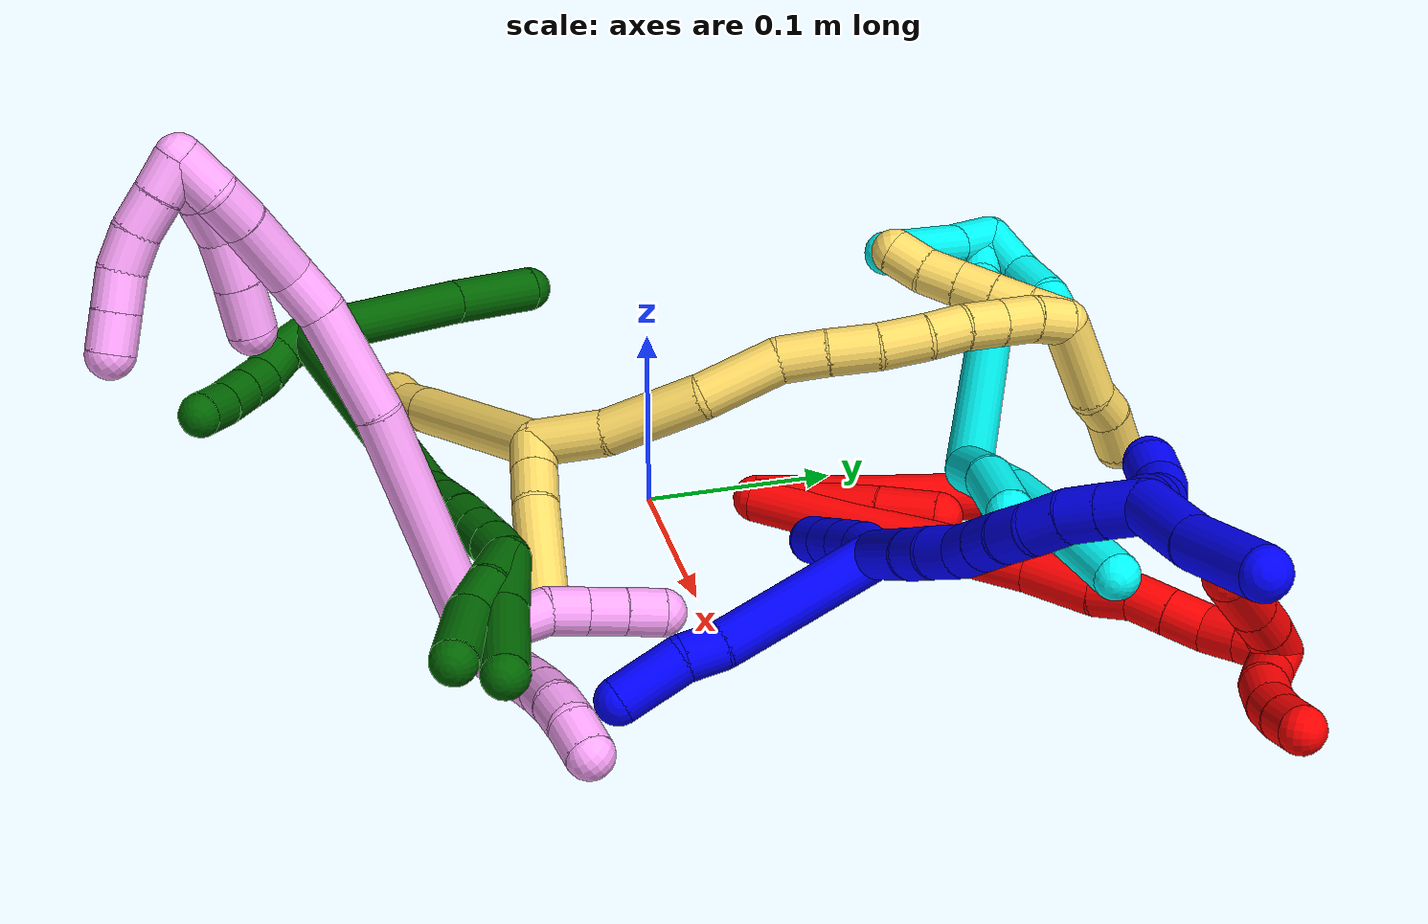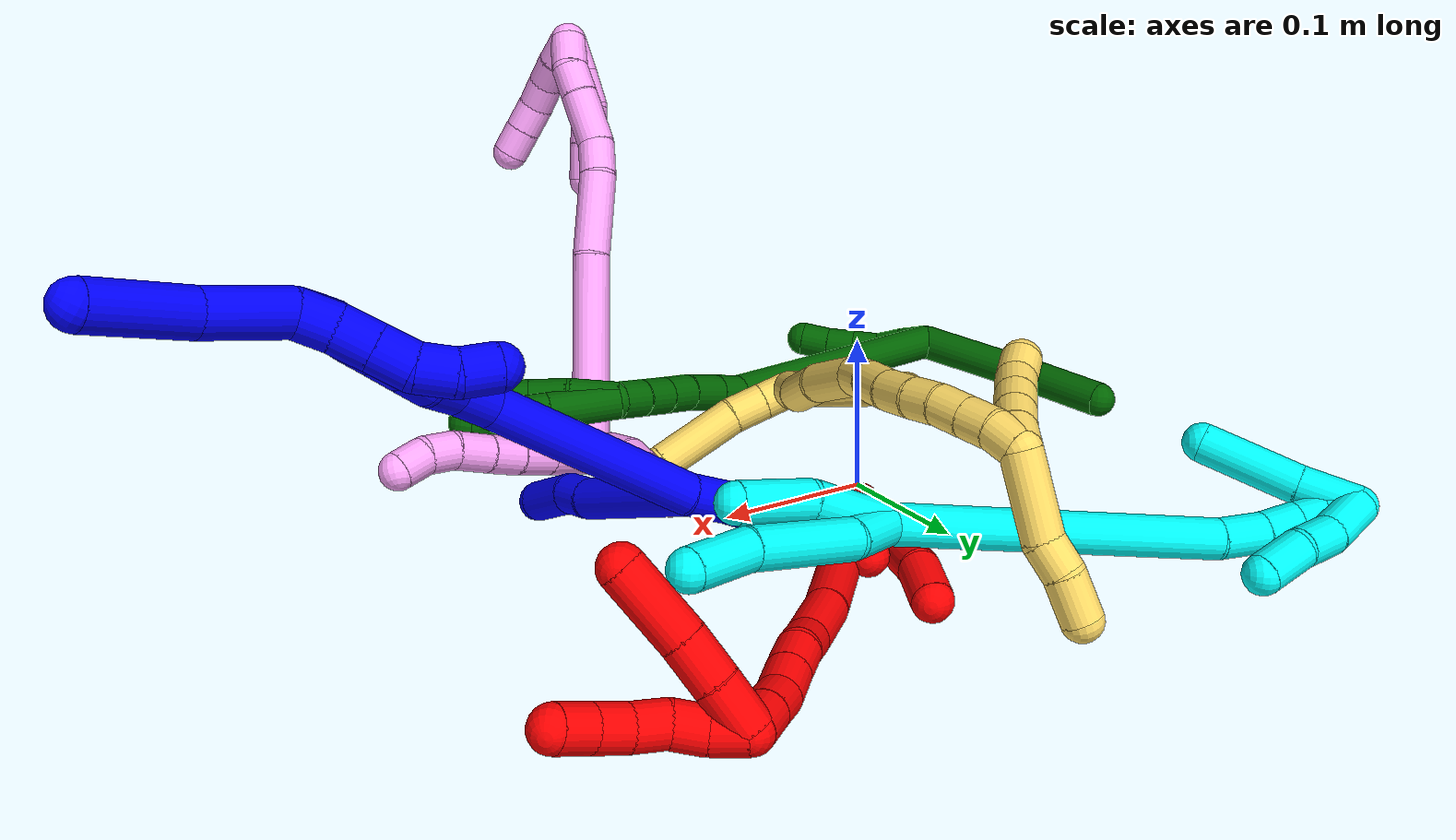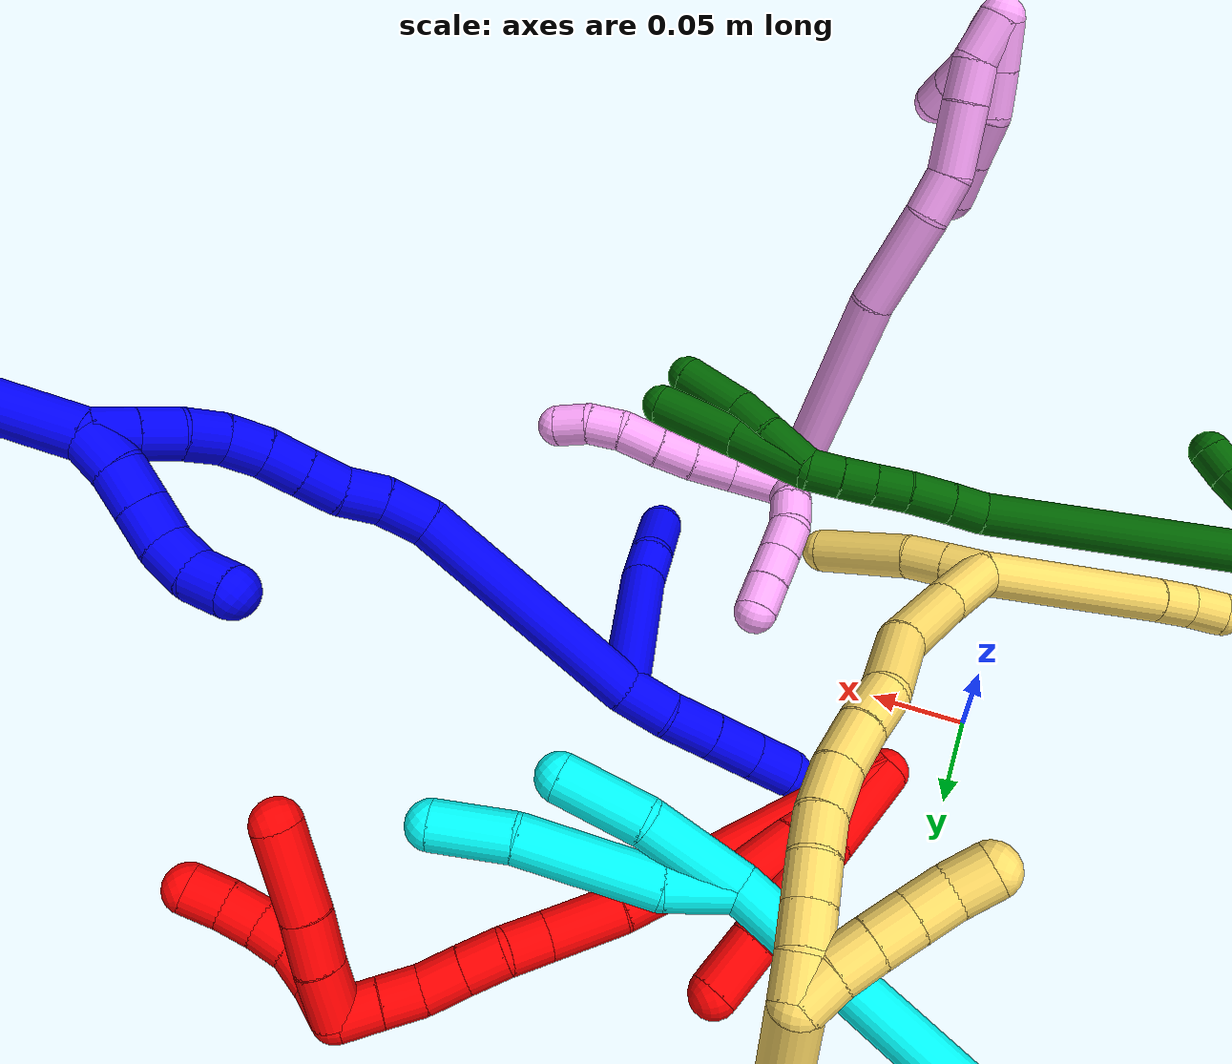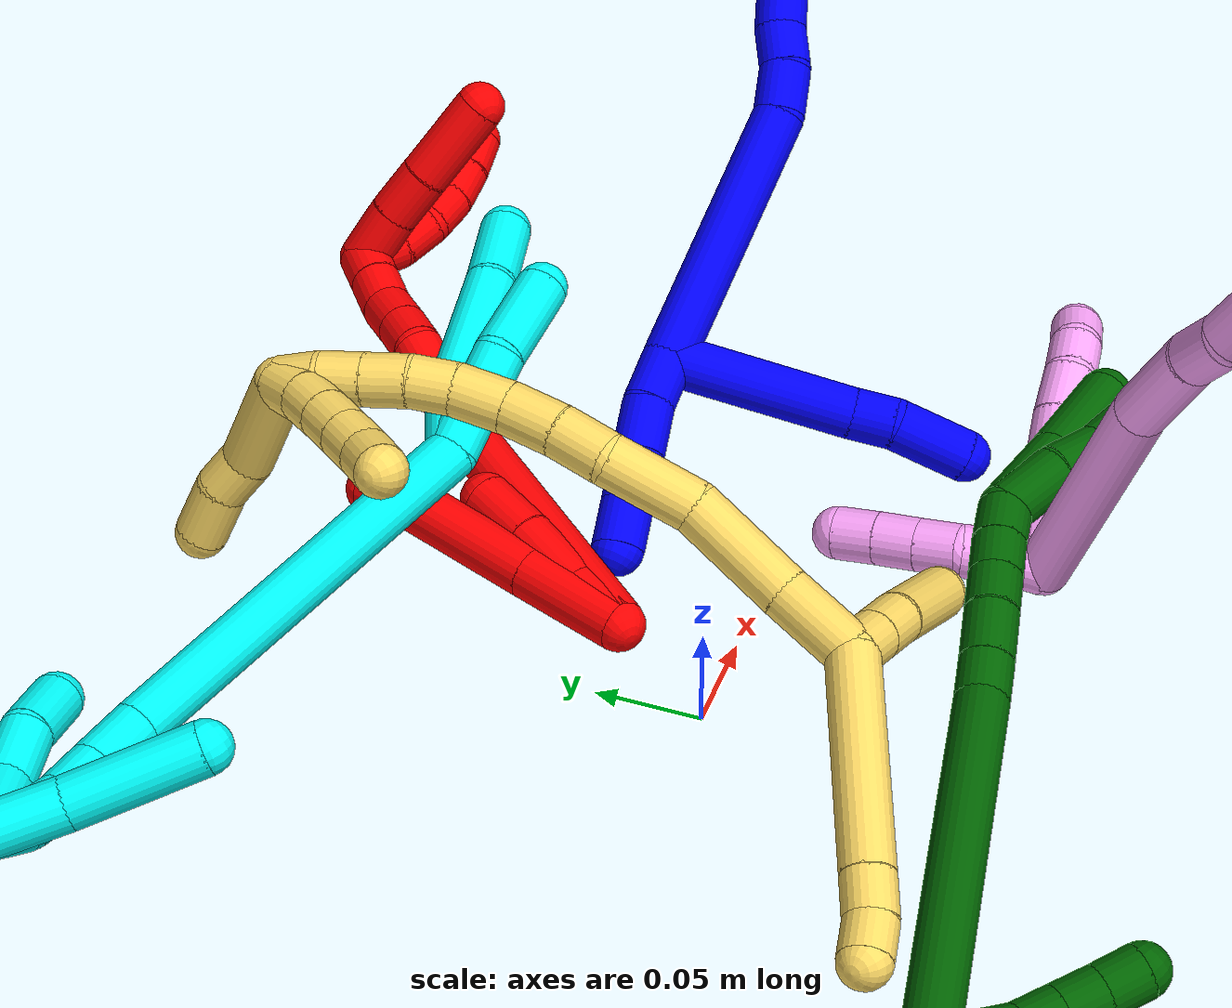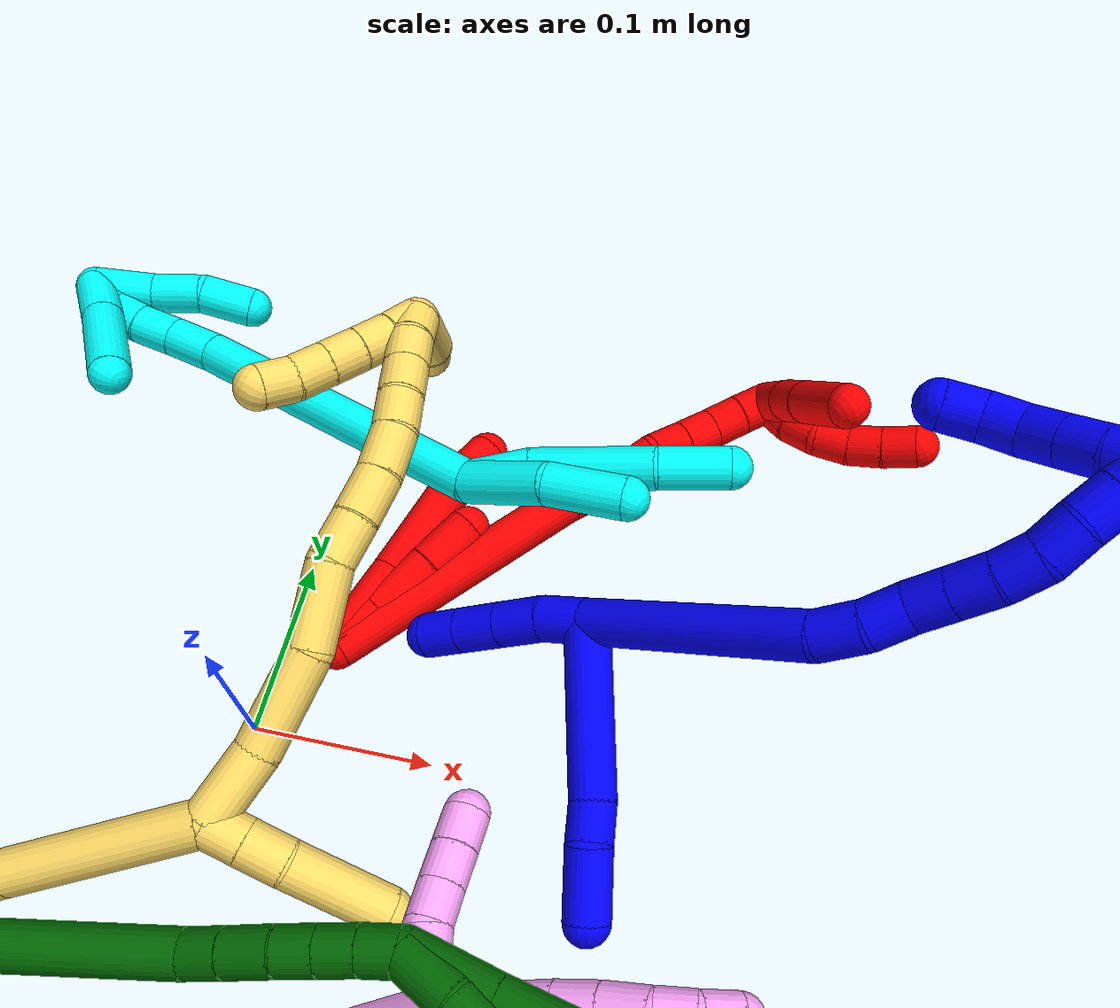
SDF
<sdf version="1.7">
 <world name="default">
  <plugin name="TubeGeneratorPlugin" filename="libtube_generator_plugin.so"/>
  <model name="photoneo_s_sensor">
   <static>1</static>
   <pose>0 0 2 1.57079 1.57079 3.14159</pose>
   <link name="link">
    <inertial><mass>0.1</mass></inertial>
    <sensor name="sensor" type="depth">
     <update_rate>30</update_rate>
     <camera>
      <horizontal_fov>1.22</horizontal_fov>
      <image><width>1920</width><height>1200</height><format>B8G8R8</format></image>
      <clip><near>0.1</near><far>4</far></clip>
      <depth_camera><output>points</output></depth_camera>
     </camera>
     <plugin name="camera_plugin" filename="libgazebo_ros_depth_camera.so">
      <baseline>0.2</baseline>
      <alwaysOn>1</alwaysOn>
      <updateRate>0.0</updateRate>
      <cameraName>camera_ir</cameraName>
      <imageTopicName>/camera/color/image_raw</imageTopicName>
      <cameraInfoTopicName>/camera/color/camera_info</cameraInfoTopicName>
      <depthImageTopicName>/camera/depth/image_raw</depthImageTopicName>
      <depthImageCameraInfoTopicName>/camera/depth/camera_info</depthImageCameraInfoTopicName>
      <pointCloudTopicName>/camera/depth/points</pointCloudTopicName>
      <frameName>fr_optical</frameName>
      <pointCloudCutoff>0.1</pointCloudCutoff>
      <pointCloudCutoffMax>2.0</pointCloudCutoffMax>
      <distortionK1>0</distortionK1>
      <distortionK2>0</distortionK2>
      <distortionK3>0</distortionK3>
      <distortionT1>0</distortionT1>
      <distortionT2>0</distortionT2>
      <CxPrime>0</CxPrime>
      <Cx>0</Cx>
      <Cy>0</Cy>
      <focalLength>0</focalLength>
      <hackBaseline>0</hackBaseline>
     </plugin>
    </sensor>
   </link>
  </model>
  <gravity>0 0 -9.8</gravity>
  <magnetic_field>6e-06 2.3e-05 -4.2e-05</magnetic_field>
  <atmosphere type="adiabatic"/>
  <physics name="default_physics" default="0" type="ode">
   <max_step_size>0.003</max_step_size>
   <real_time_factor>1</real_time_factor>
   <real_time_update_rate>1000</real_time_update_rate>
   <max_contacts>10000</max_contacts>
   <ode>
    <solver>
     <type>quick</type>
     <iters>100</iters>
     <sor>1.3</sor>
     <use_dynamic_moi_rescaling>0</use_dynamic_moi_rescaling>
    </solver>
    <constraints>
     <contact_max_correcting_vel>0</contact_max_correcting_vel>
     <contact_surface_layer>0.001</contact_surface_layer>
     <cfm>0</cfm>
     <erp>0.2</erp>
    </constraints>
   </ode>
  </physics>
  <scene><ambient>0.4 0.4 0.4 1</ambient><background>0.7 0.7 0.7 1</background><shadows>0</shadows></scene>
  <audio><device>default</device></audio>
  <spherical_coordinates>
   <surface_model>EARTH_WGS84</surface_model>
   <latitude_deg>0</latitude_deg>
   <longitude_deg>0</longitude_deg>
   <elevation>0</elevation>
   <heading_deg>0</heading_deg>
  </spherical_coordinates>
  <model name="bin">
   <static>1</static>
   <link name="bottom">
    <collision name="collision-bottom">
     <pose>0 0 -0.01 0 -0 0</pose>
     <geometry><box><size>0.8 0.6 0.02</size></box></geometry>
     <surface>
      <friction><ode><mu>100</mu><mu2>100</mu2></ode></friction>
      <contact><collide_bitmask>65535</collide_bitmask></contact>
     </surface>
    </collision>
   </link>
   <link name="west_wall">
    <collision name="collision-west_wall">
     <pose>-0.41 0 0.1 0 -0 0</pose>
     <geometry><box><size>0.02 0.6 0.2</size></box></geometry>
     <surface>
      <friction><ode><mu>100</mu><mu2>100</mu2></ode></friction>
      <contact><collide_bitmask>65535</collide_bitmask></contact>
     </surface>
    </collision>
   </link>
   <link name="east_wall">
    <collision name="collision-east_wall">
     <pose>0.41 0 0.1 0 -0 0</pose>
     <geometry><box><size>0.02 0.6 0.2</size></box></geometry>
     <surface>
      <friction><ode><mu>100</mu><mu2>100</mu2></ode></friction>
      <contact><collide_bitmask>65535</collide_bitmask></contact>
     </surface>
    </collision>
   </link>
   <link name="south_wall">
    <collision name="collision-south_wall">
     <pose>0 -0.31 0.1 0 -0 0</pose>
     <geometry><box><size>0.8 0.02 0.2</size></box></geometry>
     <surface>
      <friction><ode><mu>100</mu><mu2>100</mu2></ode></friction>
      <contact><collide_bitmask>65535</collide_bitmask></contact>
     </surface>
    </collision>
   </link>
   <link name="north_wall">
    <collision name="collision-north_wall">
     <pose>0 0.31 0.1 0 -0 0</pose>
     <geometry><box><size>0.8 0.02 0.2</size></box></geometry>
     <surface>
      <friction><ode><mu>100</mu><mu2>100</mu2></ode></friction>
      <contact><collide_bitmask>65535</collide_bitmask></contact>
     </surface>
    </collision>
   </link>
  </model>
  <model name="1">
   <static>0</static>
   <link name="1">
    <collision name="collision-cylinder-e_1_2_8">
     <pose>-0.027357 -0.036104 0.006701 1.38727 -0.640297 -0.537987</pose>
     <geometry><cylinder><radius>0.0125</radius><length>0.091581</length></cylinder></geometry>
     <surface>
      <friction><ode><mu>1.16</mu><mu2>1.16</mu2><slip1>0</slip1><slip2>0</slip2></ode></friction>
      <contact><ode><kp>1e+06</kp><kd>1</kd><max_vel>0</max_vel><min_depth>0.001</min_depth></ode></contact>
     </surface>
    </collision>
    <visual name="visual-cylinder-e_1_2_8">
     <pose>-0.027357 -0.036104 0.006701 1.38727 -0.640297 -0.537987</pose>
     <geometry><cylinder><radius>0.0125</radius><length>0.091581</length></cylinder></geometry>
     <material><ambient>0 0 1 1</ambient></material>
    </visual>
    <collision name="collision-cylinder-e_2_8_9">
     <pose>-0.062569 -0.07909 0.01493 1.3524 -0.839386 -0.687626</pose>
     <geometry><cylinder><radius>0.0125</radius><length>0.021111</length></cylinder></geometry>
     <surface>
      <friction><ode><mu>1.16</mu><mu2>1.16</mu2><slip1>0</slip1><slip2>0</slip2></ode></friction>
      <contact><ode><kp>1e+06</kp><kd>1</kd><max_vel>0</max_vel><min_depth>0.001</min_depth></ode></contact>
     </surface>
    </collision>
    <visual name="visual-cylinder-e_2_8_9">
     <pose>-0.062569 -0.07909 0.01493 1.3524 -0.839386 -0.687626</pose>
     <geometry><cylinder><radius>0.0125</radius><length>0.021111</length></cylinder></geometry>
     <material><ambient>0 0 1 1</ambient></material>
    </visual>
    <collision name="collision-cylinder-e_3_9_6">
     <pose>-0.080816 -0.10146 0.016842 1.54601 -0.590805 -0.577138</pose>
     <geometry><cylinder><radius>0.0125</radius><length>0.037308</length></cylinder></geometry>
     <surface>
      <friction><ode><mu>1.16</mu><mu2>1.16</mu2><slip1>0</slip1><slip2>0</slip2></ode></friction>
      <contact><ode><kp>1e+06</kp><kd>1</kd><max_vel>0</max_vel><min_depth>0.001</min_depth></ode></contact>
     </surface>
    </collision>
    <visual name="visual-cylinder-e_3_9_6">
     <pose>-0.080816 -0.10146 0.016842 1.54601 -0.590805 -0.577138</pose>
     <geometry><cylinder><radius>0.0125</radius><length>0.037308</length></cylinder></geometry>
     <material><ambient>0 0 1 1</ambient></material>
    </visual>
    <collision name="collision-cylinder-e_1_2_10">
     <pose>-0.002086 0.001764 -0.012606 -3.00256 -0.162398 1.72609</pose>
     <geometry><cylinder><radius>0.0125</radius><length>0.025798</length></cylinder></geometry>
     <surface>
      <friction><ode><mu>1.16</mu><mu2>1.16</mu2><slip1>0</slip1><slip2>0</slip2></ode></friction>
      <contact><ode><kp>1e+06</kp><kd>1</kd><max_vel>0</max_vel><min_depth>0.001</min_depth></ode></contact>
     </surface>
    </collision>
    <visual name="visual-cylinder-e_1_2_10">
     <pose>-0.002086 0.001764 -0.012606 -3.00256 -0.162398 1.72609</pose>
     <geometry><cylinder><radius>0.0125</radius><length>0.025798</length></cylinder></geometry>
     <material><ambient>0 0 1 1</ambient></material>
    </visual>
    <collision name="collision-cylinder-e_2_10_11">
     <pose>-0.007372 0.003135 -0.037738 3.11022 -0.250042 -2.89321</pose>
     <geometry><cylinder><radius>0.0125</radius><length>0.025868</length></cylinder></geometry>
     <surface>
      <friction><ode><mu>1.16</mu><mu2>1.16</mu2><slip1>0</slip1><slip2>0</slip2></ode></friction>
      <contact><ode><kp>1e+06</kp><kd>1</kd><max_vel>0</max_vel><min_depth>0.001</min_depth></ode></contact>
     </surface>
    </collision>
    <visual name="visual-cylinder-e_2_10_11">
     <pose>-0.007372 0.003135 -0.037738 3.11022 -0.250042 -2.89321</pose>
     <geometry><cylinder><radius>0.0125</radius><length>0.025868</length></cylinder></geometry>
     <material><ambient>0 0 1 1</ambient></material>
    </visual>
    <collision name="collision-cylinder-e_3_11_12">
     <pose>-0.013642 0.002304 -0.062602 3.10612 -0.243708 -2.85392</pose>
     <geometry><cylinder><radius>0.0125</radius><length>0.025444</length></cylinder></geometry>
     <surface>
      <friction><ode><mu>1.16</mu><mu2>1.16</mu2><slip1>0</slip1><slip2>0</slip2></ode></friction>
      <contact><ode><kp>1e+06</kp><kd>1</kd><max_vel>0</max_vel><min_depth>0.001</min_depth></ode></contact>
     </surface>
    </collision>
    <visual name="visual-cylinder-e_3_11_12">
     <pose>-0.013642 0.002304 -0.062602 3.10612 -0.243708 -2.85392</pose>
     <geometry><cylinder><radius>0.0125</radius><length>0.025444</length></cylinder></geometry>
     <material><ambient>0 0 1 1</ambient></material>
    </visual>
    <collision name="collision-cylinder-e_4_12_5">
     <pose>-0.019524 0.001511 -0.086029 3.10959 -0.24826 -2.88648</pose>
     <geometry><cylinder><radius>0.0125</radius><length>0.02289</length></cylinder></geometry>
     <surface>
      <friction><ode><mu>1.16</mu><mu2>1.16</mu2><slip1>0</slip1><slip2>0</slip2></ode></friction>
      <contact><ode><kp>1e+06</kp><kd>1</kd><max_vel>0</max_vel><min_depth>0.001</min_depth></ode></contact>
     </surface>
    </collision>
    <visual name="visual-cylinder-e_4_12_5">
     <pose>-0.019524 0.001511 -0.086029 3.10959 -0.24826 -2.88648</pose>
     <geometry><cylinder><radius>0.0125</radius><length>0.02289</length></cylinder></geometry>
     <material><ambient>0 0 1 1</ambient></material>
    </visual>
    <collision name="collision-cylinder-e_1_2_13">
     <pose>0.000268 -0.001428 0.066058 0.021621 0.004062 4.4e-05</pose>
     <geometry><cylinder><radius>0.0125</radius><length>0.132147</length></cylinder></geometry>
     <surface>
      <friction><ode><mu>1.16</mu><mu2>1.16</mu2><slip1>0</slip1><slip2>0</slip2></ode></friction>
      <contact><ode><kp>1e+06</kp><kd>1</kd><max_vel>0</max_vel><min_depth>0.001</min_depth></ode></contact>
     </surface>
    </collision>
    <visual name="visual-cylinder-e_1_2_13">
     <pose>0.000268 -0.001428 0.066058 0.021621 0.004062 4.4e-05</pose>
     <geometry><cylinder><radius>0.0125</radius><length>0.132147</length></cylinder></geometry>
     <material><ambient>0 0 1 1</ambient></material>
    </visual>
    <collision name="collision-cylinder-e_2_13_14">
     <pose>0.003563 -0.001447 0.143964 -0.118444 0.248339 -0.0148</pose>
     <geometry><cylinder><radius>0.0125</radius><length>0.024621</length></cylinder></geometry>
     <surface>
      <friction><ode><mu>1.16</mu><mu2>1.16</mu2><slip1>0</slip1><slip2>0</slip2></ode></friction>
      <contact><ode><kp>1e+06</kp><kd>1</kd><max_vel>0</max_vel><min_depth>0.001</min_depth></ode></contact>
     </surface>
    </collision>
    <visual name="visual-cylinder-e_2_13_14">
     <pose>0.003563 -0.001447 0.143964 -0.118444 0.248339 -0.0148</pose>
     <geometry><cylinder><radius>0.0125</radius><length>0.024621</length></cylinder></geometry>
     <material><ambient>0 0 1 1</ambient></material>
    </visual>
    <collision name="collision-cylinder-e_3_14_15">
     <pose>0.011496 0.002131 0.165071 -0.230009 0.476494 -0.056093</pose>
     <geometry><cylinder><radius>0.0125</radius><length>0.021399</length></cylinder></geometry>
     <surface>
      <friction><ode><mu>1.16</mu><mu2>1.16</mu2><slip1>0</slip1><slip2>0</slip2></ode></friction>
      <contact><ode><kp>1e+06</kp><kd>1</kd><max_vel>0</max_vel><min_depth>0.001</min_depth></ode></contact>
     </surface>
    </collision>
    <visual name="visual-cylinder-e_3_14_15">
     <pose>0.011496 0.002131 0.165071 -0.230009 0.476494 -0.056093</pose>
     <geometry><cylinder><radius>0.0125</radius><length>0.021399</length></cylinder></geometry>
     <material><ambient>0 0 1 1</ambient></material>
    </visual>
    <collision name="collision-cylinder-e_4_15_16">
     <pose>0.018818 0.006803 0.184102 -0.250842 0.234924 -0.029755</pose>
     <geometry><cylinder><radius>0.0125</radius><length>0.020747</length></cylinder></geometry>
     <surface>
      <friction><ode><mu>1.16</mu><mu2>1.16</mu2><slip1>0</slip1><slip2>0</slip2></ode></friction>
      <contact><ode><kp>1e+06</kp><kd>1</kd><max_vel>0</max_vel><min_depth>0.001</min_depth></ode></contact>
     </surface>
    </collision>
    <visual name="visual-cylinder-e_4_15_16">
     <pose>0.018818 0.006803 0.184102 -0.250842 0.234924 -0.029755</pose>
     <geometry><cylinder><radius>0.0125</radius><length>0.020747</length></cylinder></geometry>
     <material><ambient>0 0 1 1</ambient></material>
    </visual>
    <collision name="collision-cylinder-e_5_16_17">
     <pose>0.023663 0.011866 0.203685 -0.255135 0.235254 -0.030312</pose>
     <geometry><cylinder><radius>0.0125</radius><length>0.020851</length></cylinder></geometry>
     <surface>
      <friction><ode><mu>1.16</mu><mu2>1.16</mu2><slip1>0</slip1><slip2>0</slip2></ode></friction>
      <contact><ode><kp>1e+06</kp><kd>1</kd><max_vel>0</max_vel><min_depth>0.001</min_depth></ode></contact>
     </surface>
    </collision>
    <visual name="visual-cylinder-e_5_16_17">
     <pose>0.023663 0.011866 0.203685 -0.255135 0.235254 -0.030312</pose>
     <geometry><cylinder><radius>0.0125</radius><length>0.020851</length></cylinder></geometry>
     <material><ambient>0 0 1 1</ambient></material>
    </visual>
    <collision name="collision-cylinder-e_6_17_18">
     <pose>0.02971 0.017636 0.222339 -0.348317 0.366944 -0.065272</pose>
     <geometry><cylinder><radius>0.0125</radius><length>0.020161</length></cylinder></geometry>
     <surface>
      <friction><ode><mu>1.16</mu><mu2>1.16</mu2><slip1>0</slip1><slip2>0</slip2></ode></friction>
      <contact><ode><kp>1e+06</kp><kd>1</kd><max_vel>0</max_vel><min_depth>0.001</min_depth></ode></contact>
     </surface>
    </collision>
    <visual name="visual-cylinder-e_6_17_18">
     <pose>0.02971 0.017636 0.222339 -0.348317 0.366944 -0.065272</pose>
     <geometry><cylinder><radius>0.0125</radius><length>0.020161</length></cylinder></geometry>
     <material><ambient>0 0 1 1</ambient></material>
    </visual>
    <collision name="collision-cylinder-e_7_18_19">
     <pose>0.038358 0.025764 0.238324 -0.603053 0.525936 -0.167059</pose>
     <geometry><cylinder><radius>0.0125</radius><length>0.020047</length></cylinder></geometry>
     <surface>
      <friction><ode><mu>1.16</mu><mu2>1.16</mu2><slip1>0</slip1><slip2>0</slip2></ode></friction>
      <contact><ode><kp>1e+06</kp><kd>1</kd><max_vel>0</max_vel><min_depth>0.001</min_depth></ode></contact>
     </surface>
    </collision>
    <visual name="visual-cylinder-e_7_18_19">
     <pose>0.038358 0.025764 0.238324 -0.603053 0.525936 -0.167059</pose>
     <geometry><cylinder><radius>0.0125</radius><length>0.020047</length></cylinder></geometry>
     <material><ambient>0 0 1 1</ambient></material>
    </visual>
    <collision name="collision-cylinder-e_8_19_20">
     <pose>0.04972 0.034389 0.252262 -0.499262 0.685272 -0.181385</pose>
     <geometry><cylinder><radius>0.0125</radius><length>0.020003</length></cylinder></geometry>
     <surface>
      <friction><ode><mu>1.16</mu><mu2>1.16</mu2><slip1>0</slip1><slip2>0</slip2></ode></friction>
      <contact><ode><kp>1e+06</kp><kd>1</kd><max_vel>0</max_vel><min_depth>0.001</min_depth></ode></contact>
     </surface>
    </collision>
    <visual name="visual-cylinder-e_8_19_20">
     <pose>0.04972 0.034389 0.252262 -0.499262 0.685272 -0.181385</pose>
     <geometry><cylinder><radius>0.0125</radius><length>0.020003</length></cylinder></geometry>
     <material><ambient>0 0 1 1</ambient></material>
    </visual>
    <collision name="collision-cylinder-e_9_20_1">
     <pose>0.062547 0.041728 0.265756 -0.496979 0.706198 -0.186482</pose>
     <geometry><cylinder><radius>0.0125</radius><length>0.020022</length></cylinder></geometry>
     <surface>
      <friction><ode><mu>1.16</mu><mu2>1.16</mu2><slip1>0</slip1><slip2>0</slip2></ode></friction>
      <contact><ode><kp>1e+06</kp><kd>1</kd><max_vel>0</max_vel><min_depth>0.001</min_depth></ode></contact>
     </surface>
    </collision>
    <visual name="visual-cylinder-e_9_20_1">
     <pose>0.062547 0.041728 0.265756 -0.496979 0.706198 -0.186482</pose>
     <geometry><cylinder><radius>0.0125</radius><length>0.020022</length></cylinder></geometry>
     <material><ambient>0 0 1 1</ambient></material>
    </visual>
    <collision name="collision-cylinder-e_1_1_21">
     <pose>0.077744 0.040009 0.293123 0.253266 0.386901 0.049871</pose>
     <geometry><cylinder><radius>0.0125</radius><length>0.046115</length></cylinder></geometry>
     <surface>
      <friction><ode><mu>1.16</mu><mu2>1.16</mu2><slip1>0</slip1><slip2>0</slip2></ode></friction>
      <contact><ode><kp>1e+06</kp><kd>1</kd><max_vel>0</max_vel><min_depth>0.001</min_depth></ode></contact>
     </surface>
    </collision>
    <visual name="visual-cylinder-e_1_1_21">
     <pose>0.077744 0.040009 0.293123 0.253266 0.386901 0.049871</pose>
     <geometry><cylinder><radius>0.0125</radius><length>0.046115</length></cylinder></geometry>
     <material><ambient>0 0 1 1</ambient></material>
    </visual>
    <collision name="collision-cylinder-e_2_21_4">
     <pose>0.097573 0.031846 0.33817 0.11488 0.425846 0.024863</pose>
     <geometry><cylinder><radius>0.0125</radius><length>0.053885</length></cylinder></geometry>
     <surface>
      <friction><ode><mu>1.16</mu><mu2>1.16</mu2><slip1>0</slip1><slip2>0</slip2></ode></friction>
      <contact><ode><kp>1e+06</kp><kd>1</kd><max_vel>0</max_vel><min_depth>0.001</min_depth></ode></contact>
     </surface>
    </collision>
    <visual name="visual-cylinder-e_2_21_4">
     <pose>0.097573 0.031846 0.33817 0.11488 0.425846 0.024863</pose>
     <geometry><cylinder><radius>0.0125</radius><length>0.053885</length></cylinder></geometry>
     <material><ambient>0 0 1 1</ambient></material>
    </visual>
    <collision name="collision-cylinder-e_1_1_22">
     <pose>0.070243 0.047265 0.262708 -2.94839 0.120201 -1.11139</pose>
     <geometry><cylinder><radius>0.0125</radius><length>0.02</length></cylinder></geometry>
     <surface>
      <friction><ode><mu>1.16</mu><mu2>1.16</mu2><slip1>0</slip1><slip2>0</slip2></ode></friction>
      <contact><ode><kp>1e+06</kp><kd>1</kd><max_vel>0</max_vel><min_depth>0.001</min_depth></ode></contact>
     </surface>
    </collision>
    <visual name="visual-cylinder-e_1_1_22">
     <pose>0.070243 0.047265 0.262708 -2.94839 0.120201 -1.11139</pose>
     <geometry><cylinder><radius>0.0125</radius><length>0.02</length></cylinder></geometry>
     <material><ambient>0 0 1 1</ambient></material>
    </visual>
    <collision name="collision-cylinder-e_2_22_23">
     <pose>0.074361 0.050989 0.243575 -2.9504 0.296207 -1.99914</pose>
     <geometry><cylinder><radius>0.0125</radius><length>0.02</length></cylinder></geometry>
     <surface>
      <friction><ode><mu>1.16</mu><mu2>1.16</mu2><slip1>0</slip1><slip2>0</slip2></ode></friction>
      <contact><ode><kp>1e+06</kp><kd>1</kd><max_vel>0</max_vel><min_depth>0.001</min_depth></ode></contact>
     </surface>
    </collision>
    <visual name="visual-cylinder-e_2_22_23">
     <pose>0.074361 0.050989 0.243575 -2.9504 0.296207 -1.99914</pose>
     <geometry><cylinder><radius>0.0125</radius><length>0.02</length></cylinder></geometry>
     <material><ambient>0 0 1 1</ambient></material>
    </visual>
    <collision name="collision-cylinder-e_3_23_24">
     <pose>0.080249 0.054622 0.22481 -2.95027 0.301471 -2.01471</pose>
     <geometry><cylinder><radius>0.0125</radius><length>0.02</length></cylinder></geometry>
     <surface>
      <friction><ode><mu>1.16</mu><mu2>1.16</mu2><slip1>0</slip1><slip2>0</slip2></ode></friction>
      <contact><ode><kp>1e+06</kp><kd>1</kd><max_vel>0</max_vel><min_depth>0.001</min_depth></ode></contact>
     </surface>
    </collision>
    <visual name="visual-cylinder-e_3_23_24">
     <pose>0.080249 0.054622 0.22481 -2.95027 0.301471 -2.01471</pose>
     <geometry><cylinder><radius>0.0125</radius><length>0.02</length></cylinder></geometry>
     <material><ambient>0 0 1 1</ambient></material>
    </visual>
    <collision name="collision-cylinder-e_4_24_25">
     <pose>0.083628 0.060484 0.206299 -2.72469 0.040989 -0.193202</pose>
     <geometry><cylinder><radius>0.0125</radius><length>0.02</length></cylinder></geometry>
     <surface>
      <friction><ode><mu>1.16</mu><mu2>1.16</mu2><slip1>0</slip1><slip2>0</slip2></ode></friction>
      <contact><ode><kp>1e+06</kp><kd>1</kd><max_vel>0</max_vel><min_depth>0.001</min_depth></ode></contact>
     </surface>
    </collision>
    <visual name="visual-cylinder-e_4_24_25">
     <pose>0.083628 0.060484 0.206299 -2.72469 0.040989 -0.193202</pose>
     <geometry><cylinder><radius>0.0125</radius><length>0.02</length></cylinder></geometry>
     <material><ambient>0 0 1 1</ambient></material>
    </visual>
    <collision name="collision-cylinder-e_5_25_3">
     <pose>0.081354 0.069393 0.188848 -2.61242 -0.271746 0.934641</pose>
     <geometry><cylinder><radius>0.0125</radius><length>0.02</length></cylinder></geometry>
     <surface>
      <friction><ode><mu>1.16</mu><mu2>1.16</mu2><slip1>0</slip1><slip2>0</slip2></ode></friction>
      <contact><ode><kp>1e+06</kp><kd>1</kd><max_vel>0</max_vel><min_depth>0.001</min_depth></ode></contact>
     </surface>
    </collision>
    <visual name="visual-cylinder-e_5_25_3">
     <pose>0.081354 0.069393 0.188848 -2.61242 -0.271746 0.934641</pose>
     <geometry><cylinder><radius>0.0125</radius><length>0.02</length></cylinder></geometry>
     <material><ambient>0 0 1 1</ambient></material>
    </visual>
    <collision name="collision-sphere-3">
     <pose>0.07867 0.074256 0.180532 0 -0 0</pose>
     <geometry><sphere><radius>0.0125</radius></sphere></geometry>
     <surface>
      <friction><ode><mu>1.16</mu><mu2>1.16</mu2><slip1>0</slip1><slip2>0</slip2></ode></friction>
      <contact><ode><kp>1e+06</kp><kd>1</kd><max_vel>0</max_vel><min_depth>0.001</min_depth></ode></contact>
     </surface>
    </collision>
    <visual name="visual-sphere-3">
     <pose>0.07867 0.074256 0.180532 0 -0 0</pose>
     <geometry><sphere><radius>0.0125</radius></sphere></geometry>
     <material><ambient>0 0 1 1</ambient></material>
    </visual>
    <collision name="collision-sphere-25">
     <pose>0.084038 0.06453 0.197163 0 -0 0</pose>
     <geometry><sphere><radius>0.0125</radius></sphere></geometry>
     <surface>
      <friction><ode><mu>1.16</mu><mu2>1.16</mu2><slip1>0</slip1><slip2>0</slip2></ode></friction>
      <contact><ode><kp>1e+06</kp><kd>1</kd><max_vel>0</max_vel><min_depth>0.001</min_depth></ode></contact>
     </surface>
    </collision>
    <visual name="visual-sphere-25">
     <pose>0.084038 0.06453 0.197163 0 -0 0</pose>
     <geometry><sphere><radius>0.0125</radius></sphere></geometry>
     <material><ambient>0 0 1 1</ambient></material>
    </visual>
    <collision name="collision-sphere-24">
     <pose>0.083218 0.056438 0.215435 0 -0 0</pose>
     <geometry><sphere><radius>0.0125</radius></sphere></geometry>
     <surface>
      <friction><ode><mu>1.16</mu><mu2>1.16</mu2><slip1>0</slip1><slip2>0</slip2></ode></friction>
      <contact><ode><kp>1e+06</kp><kd>1</kd><max_vel>0</max_vel><min_depth>0.001</min_depth></ode></contact>
     </surface>
    </collision>
    <visual name="visual-sphere-24">
     <pose>0.083218 0.056438 0.215435 0 -0 0</pose>
     <geometry><sphere><radius>0.0125</radius></sphere></geometry>
     <material><ambient>0 0 1 1</ambient></material>
    </visual>
    <collision name="collision-sphere-23">
     <pose>0.07728 0.052806 0.234185 0 -0 0</pose>
     <geometry><sphere><radius>0.0125</radius></sphere></geometry>
     <surface>
      <friction><ode><mu>1.16</mu><mu2>1.16</mu2><slip1>0</slip1><slip2>0</slip2></ode></friction>
      <contact><ode><kp>1e+06</kp><kd>1</kd><max_vel>0</max_vel><min_depth>0.001</min_depth></ode></contact>
     </surface>
    </collision>
    <visual name="visual-sphere-23">
     <pose>0.07728 0.052806 0.234185 0 -0 0</pose>
     <geometry><sphere><radius>0.0125</radius></sphere></geometry>
     <material><ambient>0 0 1 1</ambient></material>
    </visual>
    <collision name="collision-sphere-22">
     <pose>0.071442 0.049171 0.252965 0 -0 0</pose>
     <geometry><sphere><radius>0.0125</radius></sphere></geometry>
     <surface>
      <friction><ode><mu>1.16</mu><mu2>1.16</mu2><slip1>0</slip1><slip2>0</slip2></ode></friction>
      <contact><ode><kp>1e+06</kp><kd>1</kd><max_vel>0</max_vel><min_depth>0.001</min_depth></ode></contact>
     </surface>
    </collision>
    <visual name="visual-sphere-22">
     <pose>0.071442 0.049171 0.252965 0 -0 0</pose>
     <geometry><sphere><radius>0.0125</radius></sphere></geometry>
     <material><ambient>0 0 1 1</ambient></material>
    </visual>
    <collision name="collision-sphere-4">
     <pose>0.108703 0.029033 0.362544 0 -0 0</pose>
     <geometry><sphere><radius>0.0125</radius></sphere></geometry>
     <surface>
      <friction><ode><mu>1.16</mu><mu2>1.16</mu2><slip1>0</slip1><slip2>0</slip2></ode></friction>
      <contact><ode><kp>1e+06</kp><kd>1</kd><max_vel>0</max_vel><min_depth>0.001</min_depth></ode></contact>
     </surface>
    </collision>
    <visual name="visual-sphere-4">
     <pose>0.108703 0.029033 0.362544 0 -0 0</pose>
     <geometry><sphere><radius>0.0125</radius></sphere></geometry>
     <material><ambient>0 0 1 1</ambient></material>
    </visual>
    <collision name="collision-sphere-21">
     <pose>0.086444 0.034658 0.313795 0 -0 0</pose>
     <geometry><sphere><radius>0.0125</radius></sphere></geometry>
     <surface>
      <friction><ode><mu>1.16</mu><mu2>1.16</mu2><slip1>0</slip1><slip2>0</slip2></ode></friction>
      <contact><ode><kp>1e+06</kp><kd>1</kd><max_vel>0</max_vel><min_depth>0.001</min_depth></ode></contact>
     </surface>
    </collision>
    <visual name="visual-sphere-21">
     <pose>0.086444 0.034658 0.313795 0 -0 0</pose>
     <geometry><sphere><radius>0.0125</radius></sphere></geometry>
     <material><ambient>0 0 1 1</ambient></material>
    </visual>
    <collision name="collision-sphere-1">
     <pose>0.069044 0.045359 0.272451 0 -0 0</pose>
     <geometry><sphere><radius>0.0125</radius></sphere></geometry>
     <surface>
      <friction><ode><mu>1.16</mu><mu2>1.16</mu2><slip1>0</slip1><slip2>0</slip2></ode></friction>
      <contact><ode><kp>1e+06</kp><kd>1</kd><max_vel>0</max_vel><min_depth>0.001</min_depth></ode></contact>
     </surface>
    </collision>
    <visual name="visual-sphere-1">
     <pose>0.069044 0.045359 0.272451 0 -0 0</pose>
     <geometry><sphere><radius>0.0125</radius></sphere></geometry>
     <material><ambient>0 0 1 1</ambient></material>
    </visual>
    <collision name="collision-sphere-11">
     <pose>-0.010572 0.002742 -0.050264 0 -0 0</pose>
     <geometry><sphere><radius>0.0125</radius></sphere></geometry>
     <surface>
      <friction><ode><mu>1.16</mu><mu2>1.16</mu2><slip1>0</slip1><slip2>0</slip2></ode></friction>
      <contact><ode><kp>1e+06</kp><kd>1</kd><max_vel>0</max_vel><min_depth>0.001</min_depth></ode></contact>
     </surface>
    </collision>
    <visual name="visual-sphere-11">
     <pose>-0.010572 0.002742 -0.050264 0 -0 0</pose>
     <geometry><sphere><radius>0.0125</radius></sphere></geometry>
     <material><ambient>0 0 1 1</ambient></material>
    </visual>
    <collision name="collision-sphere-10">
     <pose>-0.004171 0.003528 -0.025213 0 -0 0</pose>
     <geometry><sphere><radius>0.0125</radius></sphere></geometry>
     <surface>
      <friction><ode><mu>1.16</mu><mu2>1.16</mu2><slip1>0</slip1><slip2>0</slip2></ode></friction>
      <contact><ode><kp>1e+06</kp><kd>1</kd><max_vel>0</max_vel><min_depth>0.001</min_depth></ode></contact>
     </surface>
    </collision>
    <visual name="visual-sphere-10">
     <pose>-0.004171 0.003528 -0.025213 0 -0 0</pose>
     <geometry><sphere><radius>0.0125</radius></sphere></geometry>
     <material><ambient>0 0 1 1</ambient></material>
    </visual>
    <collision name="collision-sphere-6">
     <pose>-0.091207 -0.116947 0.017226 0 -0 0</pose>
     <geometry><sphere><radius>0.0125</radius></sphere></geometry>
     <surface>
      <friction><ode><mu>1.16</mu><mu2>1.16</mu2><slip1>0</slip1><slip2>0</slip2></ode></friction>
      <contact><ode><kp>1e+06</kp><kd>1</kd><max_vel>0</max_vel><min_depth>0.001</min_depth></ode></contact>
     </surface>
    </collision>
    <visual name="visual-sphere-6">
     <pose>-0.091207 -0.116947 0.017226 0 -0 0</pose>
     <geometry><sphere><radius>0.0125</radius></sphere></geometry>
     <material><ambient>0 0 1 1</ambient></material>
    </visual>
    <collision name="collision-sphere-9">
     <pose>-0.070425 -0.085973 0.016458 0 -0 0</pose>
     <geometry><sphere><radius>0.0125</radius></sphere></geometry>
     <surface>
      <friction><ode><mu>1.16</mu><mu2>1.16</mu2><slip1>0</slip1><slip2>0</slip2></ode></friction>
      <contact><ode><kp>1e+06</kp><kd>1</kd><max_vel>0</max_vel><min_depth>0.001</min_depth></ode></contact>
     </surface>
    </collision>
    <visual name="visual-sphere-9">
     <pose>-0.070425 -0.085973 0.016458 0 -0 0</pose>
     <geometry><sphere><radius>0.0125</radius></sphere></geometry>
     <material><ambient>0 0 1 1</ambient></material>
    </visual>
    <collision name="collision-sphere-2">
     <geometry><sphere><radius>0.0125</radius></sphere></geometry>
     <surface>
      <friction><ode><mu>1.16</mu><mu2>1.16</mu2><slip1>0</slip1><slip2>0</slip2></ode></friction>
      <contact><ode><kp>1e+06</kp><kd>1</kd><max_vel>0</max_vel><min_depth>0.001</min_depth></ode></contact>
     </surface>
    </collision>
    <visual name="visual-sphere-2">
     <geometry><sphere><radius>0.0125</radius></sphere></geometry>
     <material><ambient>0 0 1 1</ambient></material>
    </visual>
    <collision name="collision-sphere-19">
     <pose>0.043391 0.030681 0.245464 0 -0 0</pose>
     <geometry><sphere><radius>0.0125</radius></sphere></geometry>
     <surface>
      <friction><ode><mu>1.16</mu><mu2>1.16</mu2><slip1>0</slip1><slip2>0</slip2></ode></friction>
      <contact><ode><kp>1e+06</kp><kd>1</kd><max_vel>0</max_vel><min_depth>0.001</min_depth></ode></contact>
     </surface>
    </collision>
    <visual name="visual-sphere-19">
     <pose>0.043391 0.030681 0.245464 0 -0 0</pose>
     <geometry><sphere><radius>0.0125</radius></sphere></geometry>
     <material><ambient>0 0 1 1</ambient></material>
    </visual>
    <collision name="collision-sphere-8">
     <pose>-0.054714 -0.072207 0.013403 0 -0 0</pose>
     <geometry><sphere><radius>0.0125</radius></sphere></geometry>
     <surface>
      <friction><ode><mu>1.16</mu><mu2>1.16</mu2><slip1>0</slip1><slip2>0</slip2></ode></friction>
      <contact><ode><kp>1e+06</kp><kd>1</kd><max_vel>0</max_vel><min_depth>0.001</min_depth></ode></contact>
     </surface>
    </collision>
    <visual name="visual-sphere-8">
     <pose>-0.054714 -0.072207 0.013403 0 -0 0</pose>
     <geometry><sphere><radius>0.0125</radius></sphere></geometry>
     <material><ambient>0 0 1 1</ambient></material>
    </visual>
    <collision name="collision-sphere-12">
     <pose>-0.016712 0.001866 -0.074941 0 -0 0</pose>
     <geometry><sphere><radius>0.0125</radius></sphere></geometry>
     <surface>
      <friction><ode><mu>1.16</mu><mu2>1.16</mu2><slip1>0</slip1><slip2>0</slip2></ode></friction>
      <contact><ode><kp>1e+06</kp><kd>1</kd><max_vel>0</max_vel><min_depth>0.001</min_depth></ode></contact>
     </surface>
    </collision>
    <visual name="visual-sphere-12">
     <pose>-0.016712 0.001866 -0.074941 0 -0 0</pose>
     <geometry><sphere><radius>0.0125</radius></sphere></geometry>
     <material><ambient>0 0 1 1</ambient></material>
    </visual>
    <collision name="collision-sphere-5">
     <pose>-0.022336 0.001156 -0.097118 0 -0 0</pose>
     <geometry><sphere><radius>0.0125</radius></sphere></geometry>
     <surface>
      <friction><ode><mu>1.16</mu><mu2>1.16</mu2><slip1>0</slip1><slip2>0</slip2></ode></friction>
      <contact><ode><kp>1e+06</kp><kd>1</kd><max_vel>0</max_vel><min_depth>0.001</min_depth></ode></contact>
     </surface>
    </collision>
    <visual name="visual-sphere-5">
     <pose>-0.022336 0.001156 -0.097118 0 -0 0</pose>
     <geometry><sphere><radius>0.0125</radius></sphere></geometry>
     <material><ambient>0 0 1 1</ambient></material>
    </visual>
    <collision name="collision-sphere-13">
     <pose>0.000537 -0.002857 0.132115 0 -0 0</pose>
     <geometry><sphere><radius>0.0125</radius></sphere></geometry>
     <surface>
      <friction><ode><mu>1.16</mu><mu2>1.16</mu2><slip1>0</slip1><slip2>0</slip2></ode></friction>
      <contact><ode><kp>1e+06</kp><kd>1</kd><max_vel>0</max_vel><min_depth>0.001</min_depth></ode></contact>
     </surface>
    </collision>
    <visual name="visual-sphere-13">
     <pose>0.000537 -0.002857 0.132115 0 -0 0</pose>
     <geometry><sphere><radius>0.0125</radius></sphere></geometry>
     <material><ambient>0 0 1 1</ambient></material>
    </visual>
    <collision name="collision-sphere-14">
     <pose>0.006589 -3.7e-05 0.155814 0 -0 0</pose>
     <geometry><sphere><radius>0.0125</radius></sphere></geometry>
     <surface>
      <friction><ode><mu>1.16</mu><mu2>1.16</mu2><slip1>0</slip1><slip2>0</slip2></ode></friction>
      <contact><ode><kp>1e+06</kp><kd>1</kd><max_vel>0</max_vel><min_depth>0.001</min_depth></ode></contact>
     </surface>
    </collision>
    <visual name="visual-sphere-14">
     <pose>0.006589 -3.7e-05 0.155814 0 -0 0</pose>
     <geometry><sphere><radius>0.0125</radius></sphere></geometry>
     <material><ambient>0 0 1 1</ambient></material>
    </visual>
    <collision name="collision-sphere-15">
     <pose>0.016404 0.004299 0.174329 0 -0 0</pose>
     <geometry><sphere><radius>0.0125</radius></sphere></geometry>
     <surface>
      <friction><ode><mu>1.16</mu><mu2>1.16</mu2><slip1>0</slip1><slip2>0</slip2></ode></friction>
      <contact><ode><kp>1e+06</kp><kd>1</kd><max_vel>0</max_vel><min_depth>0.001</min_depth></ode></contact>
     </surface>
    </collision>
    <visual name="visual-sphere-15">
     <pose>0.016404 0.004299 0.174329 0 -0 0</pose>
     <geometry><sphere><radius>0.0125</radius></sphere></geometry>
     <material><ambient>0 0 1 1</ambient></material>
    </visual>
    <collision name="collision-sphere-16">
     <pose>0.021233 0.009307 0.193874 0 -0 0</pose>
     <geometry><sphere><radius>0.0125</radius></sphere></geometry>
     <surface>
      <friction><ode><mu>1.16</mu><mu2>1.16</mu2><slip1>0</slip1><slip2>0</slip2></ode></friction>
      <contact><ode><kp>1e+06</kp><kd>1</kd><max_vel>0</max_vel><min_depth>0.001</min_depth></ode></contact>
     </surface>
    </collision>
    <visual name="visual-sphere-16">
     <pose>0.021233 0.009307 0.193874 0 -0 0</pose>
     <geometry><sphere><radius>0.0125</radius></sphere></geometry>
     <material><ambient>0 0 1 1</ambient></material>
    </visual>
    <collision name="collision-sphere-17">
     <pose>0.026093 0.014424 0.213495 0 -0 0</pose>
     <geometry><sphere><radius>0.0125</radius></sphere></geometry>
     <surface>
      <friction><ode><mu>1.16</mu><mu2>1.16</mu2><slip1>0</slip1><slip2>0</slip2></ode></friction>
      <contact><ode><kp>1e+06</kp><kd>1</kd><max_vel>0</max_vel><min_depth>0.001</min_depth></ode></contact>
     </surface>
    </collision>
    <visual name="visual-sphere-17">
     <pose>0.026093 0.014424 0.213495 0 -0 0</pose>
     <geometry><sphere><radius>0.0125</radius></sphere></geometry>
     <material><ambient>0 0 1 1</ambient></material>
    </visual>
    <collision name="collision-sphere-18">
     <pose>0.033326 0.020848 0.231184 0 -0 0</pose>
     <geometry><sphere><radius>0.0125</radius></sphere></geometry>
     <surface>
      <friction><ode><mu>1.16</mu><mu2>1.16</mu2><slip1>0</slip1><slip2>0</slip2></ode></friction>
      <contact><ode><kp>1e+06</kp><kd>1</kd><max_vel>0</max_vel><min_depth>0.001</min_depth></ode></contact>
     </surface>
    </collision>
    <visual name="visual-sphere-18">
     <pose>0.033326 0.020848 0.231184 0 -0 0</pose>
     <geometry><sphere><radius>0.0125</radius></sphere></geometry>
     <material><ambient>0 0 1 1</ambient></material>
    </visual>
    <collision name="collision-sphere-20">
     <pose>0.05605 0.038096 0.259061 0 -0 0</pose>
     <geometry><sphere><radius>0.0125</radius></sphere></geometry>
     <surface>
      <friction><ode><mu>1.16</mu><mu2>1.16</mu2><slip1>0</slip1><slip2>0</slip2></ode></friction>
      <contact><ode><kp>1e+06</kp><kd>1</kd><max_vel>0</max_vel><min_depth>0.001</min_depth></ode></contact>
     </surface>
    </collision>
    <visual name="visual-sphere-20">
     <pose>0.05605 0.038096 0.259061 0 -0 0</pose>
     <geometry><sphere><radius>0.0125</radius></sphere></geometry>
     <material><ambient>0 0 1 1</ambient></material>
    </visual>
    <inertial>
     <pose>0.01817 0.004373 0.125945 0 -0 0</pose>
     <mass>0.75</mass>
     <inertia>
      <ixx>0.000245</ixx>
      <ixy>0</ixy>
      <ixz>0</ixz>
      <iyy>0.000236</iyy>
      <iyz>0</iyz>
      <izz>0.000107</izz>
     </inertia>
    </inertial>
   </link>
   <pose>0.169969 0.074807 0.056629 0.938002 0.37983 1.15758</pose>
  </model>
  <model name="2">
   <static>0</static>
   <link name="2">
    <collision name="collision-cylinder-e_1_2_8">
     <pose>-0.009686 -0.001243 0.024513 0.050651 -0.375884 -0.009635</pose>
     <geometry><cylinder><radius>0.0125</radius><length>0.052772</length></cylinder></geometry>
     <surface>
      <friction><ode><mu>1.16</mu><mu2>1.16</mu2><slip1>0</slip1><slip2>0</slip2></ode></friction>
      <contact><ode><kp>1e+06</kp><kd>1</kd><max_vel>0</max_vel><min_depth>0.001</min_depth></ode></contact>
     </surface>
    </collision>
    <visual name="visual-cylinder-e_1_2_8">
     <pose>-0.009686 -0.001243 0.024513 0.050651 -0.375884 -0.009635</pose>
     <geometry><cylinder><radius>0.0125</radius><length>0.052772</length></cylinder></geometry>
     <material><ambient>1 0 0 1</ambient></material>
    </visual>
    <collision name="collision-cylinder-e_2_8_9">
     <pose>-0.031848 -0.005192 0.079973 0.087241 -0.381853 -0.016872</pose>
     <geometry><cylinder><radius>0.0125</radius><length>0.066955</length></cylinder></geometry>
     <surface>
      <friction><ode><mu>1.16</mu><mu2>1.16</mu2><slip1>0</slip1><slip2>0</slip2></ode></friction>
      <contact><ode><kp>1e+06</kp><kd>1</kd><max_vel>0</max_vel><min_depth>0.001</min_depth></ode></contact>
     </surface>
    </collision>
    <visual name="visual-cylinder-e_2_8_9">
     <pose>-0.031848 -0.005192 0.079973 0.087241 -0.381853 -0.016872</pose>
     <geometry><cylinder><radius>0.0125</radius><length>0.066955</length></cylinder></geometry>
     <material><ambient>1 0 0 1</ambient></material>
    </visual>
    <collision name="collision-cylinder-e_3_9_6">
     <pose>-0.049882 -0.004889 0.124674 -0.215493 -0.376118 0.041164</pose>
     <geometry><cylinder><radius>0.0125</radius><length>0.030272</length></cylinder></geometry>
     <surface>
      <friction><ode><mu>1.16</mu><mu2>1.16</mu2><slip1>0</slip1><slip2>0</slip2></ode></friction>
      <contact><ode><kp>1e+06</kp><kd>1</kd><max_vel>0</max_vel><min_depth>0.001</min_depth></ode></contact>
     </surface>
    </collision>
    <visual name="visual-cylinder-e_3_9_6">
     <pose>-0.049882 -0.004889 0.124674 -0.215493 -0.376118 0.041164</pose>
     <geometry><cylinder><radius>0.0125</radius><length>0.030272</length></cylinder></geometry>
     <material><ambient>1 0 0 1</ambient></material>
    </visual>
    <collision name="collision-cylinder-e_1_2_10">
     <pose>-0.002536 -1e-05 0.014695 0.000678 -0.170874 -5.8e-05</pose>
     <geometry><cylinder><radius>0.0125</radius><length>0.029823</length></cylinder></geometry>
     <surface>
      <friction><ode><mu>1.16</mu><mu2>1.16</mu2><slip1>0</slip1><slip2>0</slip2></ode></friction>
      <contact><ode><kp>1e+06</kp><kd>1</kd><max_vel>0</max_vel><min_depth>0.001</min_depth></ode></contact>
     </surface>
    </collision>
    <visual name="visual-cylinder-e_1_2_10">
     <pose>-0.002536 -1e-05 0.014695 0.000678 -0.170874 -5.8e-05</pose>
     <geometry><cylinder><radius>0.0125</radius><length>0.029823</length></cylinder></geometry>
     <material><ambient>1 0 0 1</ambient></material>
    </visual>
    <collision name="collision-cylinder-e_2_10_11">
     <pose>-0.007299 -0.001419 0.048286 0.073919 -0.117008 -0.004331</pose>
     <geometry><cylinder><radius>0.0125</radius><length>0.038159</length></cylinder></geometry>
     <surface>
      <friction><ode><mu>1.16</mu><mu2>1.16</mu2><slip1>0</slip1><slip2>0</slip2></ode></friction>
      <contact><ode><kp>1e+06</kp><kd>1</kd><max_vel>0</max_vel><min_depth>0.001</min_depth></ode></contact>
     </surface>
    </collision>
    <visual name="visual-cylinder-e_2_10_11">
     <pose>-0.007299 -0.001419 0.048286 0.073919 -0.117008 -0.004331</pose>
     <geometry><cylinder><radius>0.0125</radius><length>0.038159</length></cylinder></geometry>
     <material><ambient>1 0 0 1</ambient></material>
    </visual>
    <collision name="collision-cylinder-e_3_11_5">
     <pose>-0.012 -0.00317 0.082996 0.022242 -0.155166 -0.001729</pose>
     <geometry><cylinder><radius>0.0125</radius><length>0.032018</length></cylinder></geometry>
     <surface>
      <friction><ode><mu>1.16</mu><mu2>1.16</mu2><slip1>0</slip1><slip2>0</slip2></ode></friction>
      <contact><ode><kp>1e+06</kp><kd>1</kd><max_vel>0</max_vel><min_depth>0.001</min_depth></ode></contact>
     </surface>
    </collision>
    <visual name="visual-cylinder-e_3_11_5">
     <pose>-0.012 -0.00317 0.082996 0.022242 -0.155166 -0.001729</pose>
     <geometry><cylinder><radius>0.0125</radius><length>0.032018</length></cylinder></geometry>
     <material><ambient>1 0 0 1</ambient></material>
    </visual>
    <collision name="collision-cylinder-e_1_2_12">
     <pose>0.000271 0.005553 0.078338 -0.070763 0.003447 -0.000122</pose>
     <geometry><cylinder><radius>0.0125</radius><length>0.15707</length></cylinder></geometry>
     <surface>
      <friction><ode><mu>1.16</mu><mu2>1.16</mu2><slip1>0</slip1><slip2>0</slip2></ode></friction>
      <contact><ode><kp>1e+06</kp><kd>1</kd><max_vel>0</max_vel><min_depth>0.001</min_depth></ode></contact>
     </surface>
    </collision>
    <visual name="visual-cylinder-e_1_2_12">
     <pose>0.000271 0.005553 0.078338 -0.070763 0.003447 -0.000122</pose>
     <geometry><cylinder><radius>0.0125</radius><length>0.15707</length></cylinder></geometry>
     <material><ambient>1 0 0 1</ambient></material>
    </visual>
    <collision name="collision-cylinder-e_2_12_13">
     <pose>0.00301 0.013099 0.175934 -0.10314 0.12683 -0.006555</pose>
     <geometry><cylinder><radius>0.0125</radius><length>0.039035</length></cylinder></geometry>
     <surface>
      <friction><ode><mu>1.16</mu><mu2>1.16</mu2><slip1>0</slip1><slip2>0</slip2></ode></friction>
      <contact><ode><kp>1e+06</kp><kd>1</kd><max_vel>0</max_vel><min_depth>0.001</min_depth></ode></contact>
     </surface>
    </collision>
    <visual name="visual-cylinder-e_2_12_13">
     <pose>0.00301 0.013099 0.175934 -0.10314 0.12683 -0.006555</pose>
     <geometry><cylinder><radius>0.0125</radius><length>0.039035</length></cylinder></geometry>
     <material><ambient>1 0 0 1</ambient></material>
    </visual>
    <collision name="collision-cylinder-e_3_13_14">
     <pose>0.006505 0.013901 0.205894 0.110835 0.094995 0.005274</pose>
     <geometry><cylinder><radius>0.0125</radius><length>0.021634</length></cylinder></geometry>
     <surface>
      <friction><ode><mu>1.16</mu><mu2>1.16</mu2><slip1>0</slip1><slip2>0</slip2></ode></friction>
      <contact><ode><kp>1e+06</kp><kd>1</kd><max_vel>0</max_vel><min_depth>0.001</min_depth></ode></contact>
     </surface>
    </collision>
    <visual name="visual-cylinder-e_3_13_14">
     <pose>0.006505 0.013901 0.205894 0.110835 0.094995 0.005274</pose>
     <geometry><cylinder><radius>0.0125</radius><length>0.021634</length></cylinder></geometry>
     <material><ambient>1 0 0 1</ambient></material>
    </visual>
    <collision name="collision-cylinder-e_4_14_15">
     <pose>0.00833 0.014848 0.226742 -0.207665 0.076945 -0.008022</pose>
     <geometry><cylinder><radius>0.0125</radius><length>0.020798</length></cylinder></geometry>
     <surface>
      <friction><ode><mu>1.16</mu><mu2>1.16</mu2><slip1>0</slip1><slip2>0</slip2></ode></friction>
      <contact><ode><kp>1e+06</kp><kd>1</kd><max_vel>0</max_vel><min_depth>0.001</min_depth></ode></contact>
     </surface>
    </collision>
    <visual name="visual-cylinder-e_4_14_15">
     <pose>0.00833 0.014848 0.226742 -0.207665 0.076945 -0.008022</pose>
     <geometry><cylinder><radius>0.0125</radius><length>0.020798</length></cylinder></geometry>
     <material><ambient>1 0 0 1</ambient></material>
    </visual>
    <collision name="collision-cylinder-e_5_15_16">
     <pose>0.009659 0.019244 0.24724 -0.214782 0.049955 -0.005387</pose>
     <geometry><cylinder><radius>0.0125</radius><length>0.021218</length></cylinder></geometry>
     <surface>
      <friction><ode><mu>1.16</mu><mu2>1.16</mu2><slip1>0</slip1><slip2>0</slip2></ode></friction>
      <contact><ode><kp>1e+06</kp><kd>1</kd><max_vel>0</max_vel><min_depth>0.001</min_depth></ode></contact>
     </surface>
    </collision>
    <visual name="visual-cylinder-e_5_15_16">
     <pose>0.009659 0.019244 0.24724 -0.214782 0.049955 -0.005387</pose>
     <geometry><cylinder><radius>0.0125</radius><length>0.021218</length></cylinder></geometry>
     <material><ambient>1 0 0 1</ambient></material>
    </visual>
    <collision name="collision-cylinder-e_6_16_17">
     <pose>0.011965 0.02175 0.267462 -0.025094 0.17795 -0.002239</pose>
     <geometry><cylinder><radius>0.0125</radius><length>0.020064</length></cylinder></geometry>
     <surface>
      <friction><ode><mu>1.16</mu><mu2>1.16</mu2><slip1>0</slip1><slip2>0</slip2></ode></friction>
      <contact><ode><kp>1e+06</kp><kd>1</kd><max_vel>0</max_vel><min_depth>0.001</min_depth></ode></contact>
     </surface>
    </collision>
    <visual name="visual-cylinder-e_6_16_17">
     <pose>0.011965 0.02175 0.267462 -0.025094 0.17795 -0.002239</pose>
     <geometry><cylinder><radius>0.0125</radius><length>0.020064</length></cylinder></geometry>
     <material><ambient>1 0 0 1</ambient></material>
    </visual>
    <collision name="collision-cylinder-e_7_17_1">
     <pose>0.015473 0.022712 0.287247 -0.071903 0.172566 -0.006222</pose>
     <geometry><cylinder><radius>0.0125</radius><length>0.020181</length></cylinder></geometry>
     <surface>
      <friction><ode><mu>1.16</mu><mu2>1.16</mu2><slip1>0</slip1><slip2>0</slip2></ode></friction>
      <contact><ode><kp>1e+06</kp><kd>1</kd><max_vel>0</max_vel><min_depth>0.001</min_depth></ode></contact>
     </surface>
    </collision>
    <visual name="visual-cylinder-e_7_17_1">
     <pose>0.015473 0.022712 0.287247 -0.071903 0.172566 -0.006222</pose>
     <geometry><cylinder><radius>0.0125</radius><length>0.020181</length></cylinder></geometry>
     <material><ambient>1 0 0 1</ambient></material>
    </visual>
    <collision name="collision-cylinder-e_1_1_18">
     <pose>0.026871 0.025872 0.297941 -1.26252 1.31121 -1.02438</pose>
     <geometry><cylinder><radius>0.0125</radius><length>0.02</length></cylinder></geometry>
     <surface>
      <friction><ode><mu>1.16</mu><mu2>1.16</mu2><slip1>0</slip1><slip2>0</slip2></ode></friction>
      <contact><ode><kp>1e+06</kp><kd>1</kd><max_vel>0</max_vel><min_depth>0.001</min_depth></ode></contact>
     </surface>
    </collision>
    <visual name="visual-cylinder-e_1_1_18">
     <pose>0.026871 0.025872 0.297941 -1.26252 1.31121 -1.02438</pose>
     <geometry><cylinder><radius>0.0125</radius><length>0.02</length></cylinder></geometry>
     <material><ambient>1 0 0 1</ambient></material>
    </visual>
    <collision name="collision-cylinder-e_2_18_19">
     <pose>0.04631 0.028142 0.300828 0.08305 1.35769 0.067014</pose>
     <geometry><cylinder><radius>0.0125</radius><length>0.02</length></cylinder></geometry>
     <surface>
      <friction><ode><mu>1.16</mu><mu2>1.16</mu2><slip1>0</slip1><slip2>0</slip2></ode></friction>
      <contact><ode><kp>1e+06</kp><kd>1</kd><max_vel>0</max_vel><min_depth>0.001</min_depth></ode></contact>
     </surface>
    </collision>
    <visual name="visual-cylinder-e_2_18_19">
     <pose>0.04631 0.028142 0.300828 0.08305 1.35769 0.067014</pose>
     <geometry><cylinder><radius>0.0125</radius><length>0.02</length></cylinder></geometry>
     <material><ambient>1 0 0 1</ambient></material>
    </visual>
    <collision name="collision-cylinder-e_3_19_20">
     <pose>0.064708 0.029251 0.307831 -0.256643 1.04005 -0.147496</pose>
     <geometry><cylinder><radius>0.0125</radius><length>0.02</length></cylinder></geometry>
     <surface>
      <friction><ode><mu>1.16</mu><mu2>1.16</mu2><slip1>0</slip1><slip2>0</slip2></ode></friction>
      <contact><ode><kp>1e+06</kp><kd>1</kd><max_vel>0</max_vel><min_depth>0.001</min_depth></ode></contact>
     </surface>
    </collision>
    <visual name="visual-cylinder-e_3_19_20">
     <pose>0.064708 0.029251 0.307831 -0.256643 1.04005 -0.147496</pose>
     <geometry><cylinder><radius>0.0125</radius><length>0.02</length></cylinder></geometry>
     <material><ambient>1 0 0 1</ambient></material>
    </visual>
    <collision name="collision-cylinder-e_4_20_21">
     <pose>0.08134 0.030036 0.318697 0.083613 0.92854 0.04189</pose>
     <geometry><cylinder><radius>0.0125</radius><length>0.02</length></cylinder></geometry>
     <surface>
      <friction><ode><mu>1.16</mu><mu2>1.16</mu2><slip1>0</slip1><slip2>0</slip2></ode></friction>
      <contact><ode><kp>1e+06</kp><kd>1</kd><max_vel>0</max_vel><min_depth>0.001</min_depth></ode></contact>
     </surface>
    </collision>
    <visual name="visual-cylinder-e_4_20_21">
     <pose>0.08134 0.030036 0.318697 0.083613 0.92854 0.04189</pose>
     <geometry><cylinder><radius>0.0125</radius><length>0.02</length></cylinder></geometry>
     <material><ambient>1 0 0 1</ambient></material>
    </visual>
    <collision name="collision-cylinder-e_5_21_4">
     <pose>0.096696 0.028548 0.331375 0.146183 0.825484 0.064105</pose>
     <geometry><cylinder><radius>0.0125</radius><length>0.02</length></cylinder></geometry>
     <surface>
      <friction><ode><mu>1.16</mu><mu2>1.16</mu2><slip1>0</slip1><slip2>0</slip2></ode></friction>
      <contact><ode><kp>1e+06</kp><kd>1</kd><max_vel>0</max_vel><min_depth>0.001</min_depth></ode></contact>
     </surface>
    </collision>
    <visual name="visual-cylinder-e_5_21_4">
     <pose>0.096696 0.028548 0.331375 0.146183 0.825484 0.064105</pose>
     <geometry><cylinder><radius>0.0125</radius><length>0.02</length></cylinder></geometry>
     <material><ambient>1 0 0 1</ambient></material>
    </visual>
    <collision name="collision-cylinder-e_1_1_22">
     <pose>0.027921 0.013943 0.296909 1.59749 0.846131 0.866295</pose>
     <geometry><cylinder><radius>0.0125</radius><length>0.028622</length></cylinder></geometry>
     <surface>
      <friction><ode><mu>1.16</mu><mu2>1.16</mu2><slip1>0</slip1><slip2>0</slip2></ode></friction>
      <contact><ode><kp>1e+06</kp><kd>1</kd><max_vel>0</max_vel><min_depth>0.001</min_depth></ode></contact>
     </surface>
    </collision>
    <visual name="visual-cylinder-e_1_1_22">
     <pose>0.027921 0.013943 0.296909 1.59749 0.846131 0.866295</pose>
     <geometry><cylinder><radius>0.0125</radius><length>0.028622</length></cylinder></geometry>
     <material><ambient>1 0 0 1</ambient></material>
    </visual>
    <collision name="collision-cylinder-e_2_22_23">
     <pose>0.048803 -0.003758 0.295572 1.702 0.886829 0.992981</pose>
     <geometry><cylinder><radius>0.0125</radius><length>0.026235</length></cylinder></geometry>
     <surface>
      <friction><ode><mu>1.16</mu><mu2>1.16</mu2><slip1>0</slip1><slip2>0</slip2></ode></friction>
      <contact><ode><kp>1e+06</kp><kd>1</kd><max_vel>0</max_vel><min_depth>0.001</min_depth></ode></contact>
     </surface>
    </collision>
    <visual name="visual-cylinder-e_2_22_23">
     <pose>0.048803 -0.003758 0.295572 1.702 0.886829 0.992981</pose>
     <geometry><cylinder><radius>0.0125</radius><length>0.026235</length></cylinder></geometry>
     <material><ambient>1 0 0 1</ambient></material>
    </visual>
    <collision name="collision-cylinder-e_3_23_3">
     <pose>0.07718 -0.025292 0.293772 1.62442 0.938705 0.98267</pose>
     <geometry><cylinder><radius>0.0125</radius><length>0.045143</length></cylinder></geometry>
     <surface>
      <friction><ode><mu>1.16</mu><mu2>1.16</mu2><slip1>0</slip1><slip2>0</slip2></ode></friction>
      <contact><ode><kp>1e+06</kp><kd>1</kd><max_vel>0</max_vel><min_depth>0.001</min_depth></ode></contact>
     </surface>
    </collision>
    <visual name="visual-cylinder-e_3_23_3">
     <pose>0.07718 -0.025292 0.293772 1.62442 0.938705 0.98267</pose>
     <geometry><cylinder><radius>0.0125</radius><length>0.045143</length></cylinder></geometry>
     <material><ambient>1 0 0 1</ambient></material>
    </visual>
    <collision name="collision-sphere-3">
     <pose>0.095391 -0.038609 0.293058 0 -0 0</pose>
     <geometry><sphere><radius>0.0125</radius></sphere></geometry>
     <surface>
      <friction><ode><mu>1.16</mu><mu2>1.16</mu2><slip1>0</slip1><slip2>0</slip2></ode></friction>
      <contact><ode><kp>1e+06</kp><kd>1</kd><max_vel>0</max_vel><min_depth>0.001</min_depth></ode></contact>
     </surface>
    </collision>
    <visual name="visual-sphere-3">
     <pose>0.095391 -0.038609 0.293058 0 -0 0</pose>
     <geometry><sphere><radius>0.0125</radius></sphere></geometry>
     <material><ambient>1 0 0 1</ambient></material>
    </visual>
    <collision name="collision-sphere-23">
     <pose>0.05897 -0.011975 0.294487 0 -0 0</pose>
     <geometry><sphere><radius>0.0125</radius></sphere></geometry>
     <surface>
      <friction><ode><mu>1.16</mu><mu2>1.16</mu2><slip1>0</slip1><slip2>0</slip2></ode></friction>
      <contact><ode><kp>1e+06</kp><kd>1</kd><max_vel>0</max_vel><min_depth>0.001</min_depth></ode></contact>
     </surface>
    </collision>
    <visual name="visual-sphere-23">
     <pose>0.05897 -0.011975 0.294487 0 -0 0</pose>
     <geometry><sphere><radius>0.0125</radius></sphere></geometry>
     <material><ambient>1 0 0 1</ambient></material>
    </visual>
    <collision name="collision-sphere-22">
     <pose>0.038636 0.00446 0.296656 0 -0 0</pose>
     <geometry><sphere><radius>0.0125</radius></sphere></geometry>
     <surface>
      <friction><ode><mu>1.16</mu><mu2>1.16</mu2><slip1>0</slip1><slip2>0</slip2></ode></friction>
      <contact><ode><kp>1e+06</kp><kd>1</kd><max_vel>0</max_vel><min_depth>0.001</min_depth></ode></contact>
     </surface>
    </collision>
    <visual name="visual-sphere-22">
     <pose>0.038636 0.00446 0.296656 0 -0 0</pose>
     <geometry><sphere><radius>0.0125</radius></sphere></geometry>
     <material><ambient>1 0 0 1</ambient></material>
    </visual>
    <collision name="collision-sphere-4">
     <pose>0.104044 0.02756 0.338085 0 -0 0</pose>
     <geometry><sphere><radius>0.0125</radius></sphere></geometry>
     <surface>
      <friction><ode><mu>1.16</mu><mu2>1.16</mu2><slip1>0</slip1><slip2>0</slip2></ode></friction>
      <contact><ode><kp>1e+06</kp><kd>1</kd><max_vel>0</max_vel><min_depth>0.001</min_depth></ode></contact>
     </surface>
    </collision>
    <visual name="visual-sphere-4">
     <pose>0.104044 0.02756 0.338085 0 -0 0</pose>
     <geometry><sphere><radius>0.0125</radius></sphere></geometry>
     <material><ambient>1 0 0 1</ambient></material>
    </visual>
    <collision name="collision-sphere-21">
     <pose>0.089347 0.029536 0.324666 0 -0 0</pose>
     <geometry><sphere><radius>0.0125</radius></sphere></geometry>
     <surface>
      <friction><ode><mu>1.16</mu><mu2>1.16</mu2><slip1>0</slip1><slip2>0</slip2></ode></friction>
      <contact><ode><kp>1e+06</kp><kd>1</kd><max_vel>0</max_vel><min_depth>0.001</min_depth></ode></contact>
     </surface>
    </collision>
    <visual name="visual-sphere-21">
     <pose>0.089347 0.029536 0.324666 0 -0 0</pose>
     <geometry><sphere><radius>0.0125</radius></sphere></geometry>
     <material><ambient>1 0 0 1</ambient></material>
    </visual>
    <collision name="collision-sphere-20">
     <pose>0.073332 0.030536 0.312727 0 -0 0</pose>
     <geometry><sphere><radius>0.0125</radius></sphere></geometry>
     <surface>
      <friction><ode><mu>1.16</mu><mu2>1.16</mu2><slip1>0</slip1><slip2>0</slip2></ode></friction>
      <contact><ode><kp>1e+06</kp><kd>1</kd><max_vel>0</max_vel><min_depth>0.001</min_depth></ode></contact>
     </surface>
    </collision>
    <visual name="visual-sphere-20">
     <pose>0.073332 0.030536 0.312727 0 -0 0</pose>
     <geometry><sphere><radius>0.0125</radius></sphere></geometry>
     <material><ambient>1 0 0 1</ambient></material>
    </visual>
    <collision name="collision-sphere-11">
     <pose>-0.009526 -0.002819 0.067183 0 -0 0</pose>
     <geometry><sphere><radius>0.0125</radius></sphere></geometry>
     <surface>
      <friction><ode><mu>1.16</mu><mu2>1.16</mu2><slip1>0</slip1><slip2>0</slip2></ode></friction>
      <contact><ode><kp>1e+06</kp><kd>1</kd><max_vel>0</max_vel><min_depth>0.001</min_depth></ode></contact>
     </surface>
    </collision>
    <visual name="visual-sphere-11">
     <pose>-0.009526 -0.002819 0.067183 0 -0 0</pose>
     <geometry><sphere><radius>0.0125</radius></sphere></geometry>
     <material><ambient>1 0 0 1</ambient></material>
    </visual>
    <collision name="collision-sphere-10">
     <pose>-0.005071 -2e-05 0.029389 0 -0 0</pose>
     <geometry><sphere><radius>0.0125</radius></sphere></geometry>
     <surface>
      <friction><ode><mu>1.16</mu><mu2>1.16</mu2><slip1>0</slip1><slip2>0</slip2></ode></friction>
      <contact><ode><kp>1e+06</kp><kd>1</kd><max_vel>0</max_vel><min_depth>0.001</min_depth></ode></contact>
     </surface>
    </collision>
    <visual name="visual-sphere-10">
     <pose>-0.005071 -2e-05 0.029389 0 -0 0</pose>
     <geometry><sphere><radius>0.0125</radius></sphere></geometry>
     <material><ambient>1 0 0 1</ambient></material>
    </visual>
    <collision name="collision-sphere-6">
     <pose>-0.055442 -0.001878 0.138427 0 -0 0</pose>
     <geometry><sphere><radius>0.0125</radius></sphere></geometry>
     <surface>
      <friction><ode><mu>1.16</mu><mu2>1.16</mu2><slip1>0</slip1><slip2>0</slip2></ode></friction>
      <contact><ode><kp>1e+06</kp><kd>1</kd><max_vel>0</max_vel><min_depth>0.001</min_depth></ode></contact>
     </surface>
    </collision>
    <visual name="visual-sphere-6">
     <pose>-0.055442 -0.001878 0.138427 0 -0 0</pose>
     <geometry><sphere><radius>0.0125</radius></sphere></geometry>
     <material><ambient>1 0 0 1</ambient></material>
    </visual>
    <collision name="collision-sphere-9">
     <pose>-0.044323 -0.007899 0.110922 0 -0 0</pose>
     <geometry><sphere><radius>0.0125</radius></sphere></geometry>
     <surface>
      <friction><ode><mu>1.16</mu><mu2>1.16</mu2><slip1>0</slip1><slip2>0</slip2></ode></friction>
      <contact><ode><kp>1e+06</kp><kd>1</kd><max_vel>0</max_vel><min_depth>0.001</min_depth></ode></contact>
     </surface>
    </collision>
    <visual name="visual-sphere-9">
     <pose>-0.044323 -0.007899 0.110922 0 -0 0</pose>
     <geometry><sphere><radius>0.0125</radius></sphere></geometry>
     <material><ambient>1 0 0 1</ambient></material>
    </visual>
    <collision name="collision-sphere-2">
     <geometry><sphere><radius>0.0125</radius></sphere></geometry>
     <surface>
      <friction><ode><mu>1.16</mu><mu2>1.16</mu2><slip1>0</slip1><slip2>0</slip2></ode></friction>
      <contact><ode><kp>1e+06</kp><kd>1</kd><max_vel>0</max_vel><min_depth>0.001</min_depth></ode></contact>
     </surface>
    </collision>
    <visual name="visual-sphere-2">
     <geometry><sphere><radius>0.0125</radius></sphere></geometry>
     <material><ambient>1 0 0 1</ambient></material>
    </visual>
    <collision name="collision-sphere-19">
     <pose>0.056083 0.027967 0.302935 0 -0 0</pose>
     <geometry><sphere><radius>0.0125</radius></sphere></geometry>
     <surface>
      <friction><ode><mu>1.16</mu><mu2>1.16</mu2><slip1>0</slip1><slip2>0</slip2></ode></friction>
      <contact><ode><kp>1e+06</kp><kd>1</kd><max_vel>0</max_vel><min_depth>0.001</min_depth></ode></contact>
     </surface>
    </collision>
    <visual name="visual-sphere-19">
     <pose>0.056083 0.027967 0.302935 0 -0 0</pose>
     <geometry><sphere><radius>0.0125</radius></sphere></geometry>
     <material><ambient>1 0 0 1</ambient></material>
    </visual>
    <collision name="collision-sphere-8">
     <pose>-0.019372 -0.002485 0.049025 0 -0 0</pose>
     <geometry><sphere><radius>0.0125</radius></sphere></geometry>
     <surface>
      <friction><ode><mu>1.16</mu><mu2>1.16</mu2><slip1>0</slip1><slip2>0</slip2></ode></friction>
      <contact><ode><kp>1e+06</kp><kd>1</kd><max_vel>0</max_vel><min_depth>0.001</min_depth></ode></contact>
     </surface>
    </collision>
    <visual name="visual-sphere-8">
     <pose>-0.019372 -0.002485 0.049025 0 -0 0</pose>
     <geometry><sphere><radius>0.0125</radius></sphere></geometry>
     <material><ambient>1 0 0 1</ambient></material>
    </visual>
    <collision name="collision-sphere-5">
     <pose>-0.014474 -0.003522 0.098809 0 -0 0</pose>
     <geometry><sphere><radius>0.0125</radius></sphere></geometry>
     <surface>
      <friction><ode><mu>1.16</mu><mu2>1.16</mu2><slip1>0</slip1><slip2>0</slip2></ode></friction>
      <contact><ode><kp>1e+06</kp><kd>1</kd><max_vel>0</max_vel><min_depth>0.001</min_depth></ode></contact>
     </surface>
    </collision>
    <visual name="visual-sphere-5">
     <pose>-0.014474 -0.003522 0.098809 0 -0 0</pose>
     <geometry><sphere><radius>0.0125</radius></sphere></geometry>
     <material><ambient>1 0 0 1</ambient></material>
    </visual>
    <collision name="collision-sphere-12">
     <pose>0.000541 0.011105 0.156676 0 -0 0</pose>
     <geometry><sphere><radius>0.0125</radius></sphere></geometry>
     <surface>
      <friction><ode><mu>1.16</mu><mu2>1.16</mu2><slip1>0</slip1><slip2>0</slip2></ode></friction>
      <contact><ode><kp>1e+06</kp><kd>1</kd><max_vel>0</max_vel><min_depth>0.001</min_depth></ode></contact>
     </surface>
    </collision>
    <visual name="visual-sphere-12">
     <pose>0.000541 0.011105 0.156676 0 -0 0</pose>
     <geometry><sphere><radius>0.0125</radius></sphere></geometry>
     <material><ambient>1 0 0 1</ambient></material>
    </visual>
    <collision name="collision-sphere-13">
     <pose>0.005479 0.015092 0.195192 0 -0 0</pose>
     <geometry><sphere><radius>0.0125</radius></sphere></geometry>
     <surface>
      <friction><ode><mu>1.16</mu><mu2>1.16</mu2><slip1>0</slip1><slip2>0</slip2></ode></friction>
      <contact><ode><kp>1e+06</kp><kd>1</kd><max_vel>0</max_vel><min_depth>0.001</min_depth></ode></contact>
     </surface>
    </collision>
    <visual name="visual-sphere-13">
     <pose>0.005479 0.015092 0.195192 0 -0 0</pose>
     <geometry><sphere><radius>0.0125</radius></sphere></geometry>
     <material><ambient>1 0 0 1</ambient></material>
    </visual>
    <collision name="collision-sphere-14">
     <pose>0.007531 0.01271 0.216596 0 -0 0</pose>
     <geometry><sphere><radius>0.0125</radius></sphere></geometry>
     <surface>
      <friction><ode><mu>1.16</mu><mu2>1.16</mu2><slip1>0</slip1><slip2>0</slip2></ode></friction>
      <contact><ode><kp>1e+06</kp><kd>1</kd><max_vel>0</max_vel><min_depth>0.001</min_depth></ode></contact>
     </surface>
    </collision>
    <visual name="visual-sphere-14">
     <pose>0.007531 0.01271 0.216596 0 -0 0</pose>
     <geometry><sphere><radius>0.0125</radius></sphere></geometry>
     <material><ambient>1 0 0 1</ambient></material>
    </visual>
    <collision name="collision-sphere-15">
     <pose>0.00913 0.016986 0.236887 0 -0 0</pose>
     <geometry><sphere><radius>0.0125</radius></sphere></geometry>
     <surface>
      <friction><ode><mu>1.16</mu><mu2>1.16</mu2><slip1>0</slip1><slip2>0</slip2></ode></friction>
      <contact><ode><kp>1e+06</kp><kd>1</kd><max_vel>0</max_vel><min_depth>0.001</min_depth></ode></contact>
     </surface>
    </collision>
    <visual name="visual-sphere-15">
     <pose>0.00913 0.016986 0.236887 0 -0 0</pose>
     <geometry><sphere><radius>0.0125</radius></sphere></geometry>
     <material><ambient>1 0 0 1</ambient></material>
    </visual>
    <collision name="collision-sphere-16">
     <pose>0.010189 0.021502 0.257592 0 -0 0</pose>
     <geometry><sphere><radius>0.0125</radius></sphere></geometry>
     <surface>
      <friction><ode><mu>1.16</mu><mu2>1.16</mu2><slip1>0</slip1><slip2>0</slip2></ode></friction>
      <contact><ode><kp>1e+06</kp><kd>1</kd><max_vel>0</max_vel><min_depth>0.001</min_depth></ode></contact>
     </surface>
    </collision>
    <visual name="visual-sphere-16">
     <pose>0.010189 0.021502 0.257592 0 -0 0</pose>
     <geometry><sphere><radius>0.0125</radius></sphere></geometry>
     <material><ambient>1 0 0 1</ambient></material>
    </visual>
    <collision name="collision-sphere-17">
     <pose>0.013741 0.021998 0.277332 0 -0 0</pose>
     <geometry><sphere><radius>0.0125</radius></sphere></geometry>
     <surface>
      <friction><ode><mu>1.16</mu><mu2>1.16</mu2><slip1>0</slip1><slip2>0</slip2></ode></friction>
      <contact><ode><kp>1e+06</kp><kd>1</kd><max_vel>0</max_vel><min_depth>0.001</min_depth></ode></contact>
     </surface>
    </collision>
    <visual name="visual-sphere-17">
     <pose>0.013741 0.021998 0.277332 0 -0 0</pose>
     <geometry><sphere><radius>0.0125</radius></sphere></geometry>
     <material><ambient>1 0 0 1</ambient></material>
    </visual>
    <collision name="collision-sphere-1">
     <pose>0.017206 0.023426 0.297162 0 -0 0</pose>
     <geometry><sphere><radius>0.0125</radius></sphere></geometry>
     <surface>
      <friction><ode><mu>1.16</mu><mu2>1.16</mu2><slip1>0</slip1><slip2>0</slip2></ode></friction>
      <contact><ode><kp>1e+06</kp><kd>1</kd><max_vel>0</max_vel><min_depth>0.001</min_depth></ode></contact>
     </surface>
    </collision>
    <visual name="visual-sphere-1">
     <pose>0.017206 0.023426 0.297162 0 -0 0</pose>
     <geometry><sphere><radius>0.0125</radius></sphere></geometry>
     <material><ambient>1 0 0 1</ambient></material>
    </visual>
    <collision name="collision-sphere-18">
     <pose>0.036536 0.028318 0.29872 0 -0 0</pose>
     <geometry><sphere><radius>0.0125</radius></sphere></geometry>
     <surface>
      <friction><ode><mu>1.16</mu><mu2>1.16</mu2><slip1>0</slip1><slip2>0</slip2></ode></friction>
      <contact><ode><kp>1e+06</kp><kd>1</kd><max_vel>0</max_vel><min_depth>0.001</min_depth></ode></contact>
     </surface>
    </collision>
    <visual name="visual-sphere-18">
     <pose>0.036536 0.028318 0.29872 0 -0 0</pose>
     <geometry><sphere><radius>0.0125</radius></sphere></geometry>
     <material><ambient>1 0 0 1</ambient></material>
    </visual>
    <inertial>
     <pose>0.010962 0.006099 0.161013 0 -0 0</pose>
     <mass>0.75</mass>
     <inertia>
      <ixx>0.000423</ixx>
      <ixy>0</ixy>
      <ixz>0</ixz>
      <iyy>0.000421</iyy>
      <iyz>0</iyz>
      <izz>2.9e-05</izz>
     </inertia>
    </inertial>
   </link>
   <pose>0.033127 0.050837 0.012443 -1.49612 -0.215603 -0.725781</pose>
  </model>
  <model name="3">
   <static>0</static>
   <link name="3">
    <collision name="collision-cylinder-e_1_2_8">
     <pose>0.009853 -0.009738 -0.012015 2.46047 0.567235 1.37664</pose>
     <geometry><cylinder><radius>0.0125</radius><length>0.036675</length></cylinder></geometry>
     <surface>
      <friction><ode><mu>1.16</mu><mu2>1.16</mu2><slip1>0</slip1><slip2>0</slip2></ode></friction>
      <contact><ode><kp>1e+06</kp><kd>1</kd><max_vel>0</max_vel><min_depth>0.001</min_depth></ode></contact>
     </surface>
    </collision>
    <visual name="visual-cylinder-e_1_2_8">
     <pose>0.009853 -0.009738 -0.012015 2.46047 0.567235 1.37664</pose>
     <geometry><cylinder><radius>0.0125</radius><length>0.036675</length></cylinder></geometry>
     <material><ambient>0.003922 1 0.996078 1</ambient></material>
    </visual>
    <collision name="collision-cylinder-e_2_8_9">
     <pose>0.031363 -0.035889 -0.0542 2.64337 0.327213 1.15123</pose>
     <geometry><cylinder><radius>0.0125</radius><length>0.072542</length></cylinder></geometry>
     <surface>
      <friction><ode><mu>1.16</mu><mu2>1.16</mu2><slip1>0</slip1><slip2>0</slip2></ode></friction>
      <contact><ode><kp>1e+06</kp><kd>1</kd><max_vel>0</max_vel><min_depth>0.001</min_depth></ode></contact>
     </surface>
    </collision>
    <visual name="visual-cylinder-e_2_8_9">
     <pose>0.031363 -0.035889 -0.0542 2.64337 0.327213 1.15123</pose>
     <geometry><cylinder><radius>0.0125</radius><length>0.072542</length></cylinder></geometry>
     <material><ambient>0.003922 1 0.996078 1</ambient></material>
    </visual>
    <collision name="collision-cylinder-e_3_9_6">
     <pose>0.053083 -0.060146 -0.100279 2.68353 0.51607 1.69456</pose>
     <geometry><cylinder><radius>0.0125</radius><length>0.040783</length></cylinder></geometry>
     <surface>
      <friction><ode><mu>1.16</mu><mu2>1.16</mu2><slip1>0</slip1><slip2>0</slip2></ode></friction>
      <contact><ode><kp>1e+06</kp><kd>1</kd><max_vel>0</max_vel><min_depth>0.001</min_depth></ode></contact>
     </surface>
    </collision>
    <visual name="visual-cylinder-e_3_9_6">
     <pose>0.053083 -0.060146 -0.100279 2.68353 0.51607 1.69456</pose>
     <geometry><cylinder><radius>0.0125</radius><length>0.040783</length></cylinder></geometry>
     <material><ambient>0.003922 1 0.996078 1</ambient></material>
    </visual>
    <collision name="collision-cylinder-e_1_2_10">
     <pose>0.000109 -0.013498 -0.02346 2.61948 0.004041 0.015127</pose>
     <geometry><cylinder><radius>0.0125</radius><length>0.054133</length></cylinder></geometry>
     <surface>
      <friction><ode><mu>1.16</mu><mu2>1.16</mu2><slip1>0</slip1><slip2>0</slip2></ode></friction>
      <contact><ode><kp>1e+06</kp><kd>1</kd><max_vel>0</max_vel><min_depth>0.001</min_depth></ode></contact>
     </surface>
    </collision>
    <visual name="visual-cylinder-e_1_2_10">
     <pose>0.000109 -0.013498 -0.02346 2.61948 0.004041 0.015127</pose>
     <geometry><cylinder><radius>0.0125</radius><length>0.054133</length></cylinder></geometry>
     <material><ambient>0.003922 1 0.996078 1</ambient></material>
    </visual>
    <collision name="collision-cylinder-e_2_10_5">
     <pose>0.005231 -0.034247 -0.068092 2.81167 0.220344 1.17298</pose>
     <geometry><cylinder><radius>0.0125</radius><length>0.045867</length></cylinder></geometry>
     <surface>
      <friction><ode><mu>1.16</mu><mu2>1.16</mu2><slip1>0</slip1><slip2>0</slip2></ode></friction>
      <contact><ode><kp>1e+06</kp><kd>1</kd><max_vel>0</max_vel><min_depth>0.001</min_depth></ode></contact>
     </surface>
    </collision>
    <visual name="visual-cylinder-e_2_10_5">
     <pose>0.005231 -0.034247 -0.068092 2.81167 0.220344 1.17298</pose>
     <geometry><cylinder><radius>0.0125</radius><length>0.045867</length></cylinder></geometry>
     <material><ambient>0.003922 1 0.996078 1</ambient></material>
    </visual>
    <collision name="collision-cylinder-e_1_2_11">
     <pose>-0.003145 0.012503 0.101319 -0.122786 -0.030802 0.001894</pose>
     <geometry><cylinder><radius>0.0125</radius><length>0.204272</length></cylinder></geometry>
     <surface>
      <friction><ode><mu>1.16</mu><mu2>1.16</mu2><slip1>0</slip1><slip2>0</slip2></ode></friction>
      <contact><ode><kp>1e+06</kp><kd>1</kd><max_vel>0</max_vel><min_depth>0.001</min_depth></ode></contact>
     </surface>
    </collision>
    <visual name="visual-cylinder-e_1_2_11">
     <pose>-0.003145 0.012503 0.101319 -0.122786 -0.030802 0.001894</pose>
     <geometry><cylinder><radius>0.0125</radius><length>0.204272</length></cylinder></geometry>
     <material><ambient>0.003922 1 0.996078 1</ambient></material>
    </visual>
    <collision name="collision-cylinder-e_2_11_12">
     <pose>-0.009519 0.02674 0.217326 -0.11744 -0.214892 0.012682</pose>
     <geometry><cylinder><radius>0.0125</radius><length>0.030277</length></cylinder></geometry>
     <surface>
      <friction><ode><mu>1.16</mu><mu2>1.16</mu2><slip1>0</slip1><slip2>0</slip2></ode></friction>
      <contact><ode><kp>1e+06</kp><kd>1</kd><max_vel>0</max_vel><min_depth>0.001</min_depth></ode></contact>
     </surface>
    </collision>
    <visual name="visual-cylinder-e_2_11_12">
     <pose>-0.009519 0.02674 0.217326 -0.11744 -0.214892 0.012682</pose>
     <geometry><cylinder><radius>0.0125</radius><length>0.030277</length></cylinder></geometry>
     <material><ambient>0.003922 1 0.996078 1</ambient></material>
    </visual>
    <collision name="collision-cylinder-e_3_12_13">
     <pose>-0.017062 0.029513 0.243647 -0.089174 -0.353904 0.015957</pose>
     <geometry><cylinder><radius>0.0125</radius><length>0.024901</length></cylinder></geometry>
     <surface>
      <friction><ode><mu>1.16</mu><mu2>1.16</mu2><slip1>0</slip1><slip2>0</slip2></ode></friction>
      <contact><ode><kp>1e+06</kp><kd>1</kd><max_vel>0</max_vel><min_depth>0.001</min_depth></ode></contact>
     </surface>
    </collision>
    <visual name="visual-cylinder-e_3_12_13">
     <pose>-0.017062 0.029513 0.243647 -0.089174 -0.353904 0.015957</pose>
     <geometry><cylinder><radius>0.0125</radius><length>0.024901</length></cylinder></geometry>
     <material><ambient>0.003922 1 0.996078 1</ambient></material>
    </visual>
    <collision name="collision-cylinder-e_4_13_14">
     <pose>-0.024062 0.030216 0.265089 0.034342 -0.266982 -0.004612</pose>
     <geometry><cylinder><radius>0.0125</radius><length>0.020352</length></cylinder></geometry>
     <surface>
      <friction><ode><mu>1.16</mu><mu2>1.16</mu2><slip1>0</slip1><slip2>0</slip2></ode></friction>
      <contact><ode><kp>1e+06</kp><kd>1</kd><max_vel>0</max_vel><min_depth>0.001</min_depth></ode></contact>
     </surface>
    </collision>
    <visual name="visual-cylinder-e_4_13_14">
     <pose>-0.024062 0.030216 0.265089 0.034342 -0.266982 -0.004612</pose>
     <geometry><cylinder><radius>0.0125</radius><length>0.020352</length></cylinder></geometry>
     <material><ambient>0.003922 1 0.996078 1</ambient></material>
    </visual>
    <collision name="collision-cylinder-e_5_14_1">
     <pose>-0.027897 0.026512 0.28435 0.342194 -0.114228 -0.019758</pose>
     <geometry><cylinder><radius>0.0125</radius><length>0.020199</length></cylinder></geometry>
     <surface>
      <friction><ode><mu>1.16</mu><mu2>1.16</mu2><slip1>0</slip1><slip2>0</slip2></ode></friction>
      <contact><ode><kp>1e+06</kp><kd>1</kd><max_vel>0</max_vel><min_depth>0.001</min_depth></ode></contact>
     </surface>
    </collision>
    <visual name="visual-cylinder-e_5_14_1">
     <pose>-0.027897 0.026512 0.28435 0.342194 -0.114228 -0.019758</pose>
     <geometry><cylinder><radius>0.0125</radius><length>0.020199</length></cylinder></geometry>
     <material><ambient>0.003922 1 0.996078 1</ambient></material>
    </visual>
    <collision name="collision-cylinder-e_1_1_15">
     <pose>-0.037523 0.026095 0.277759 -2.95974 -0.479144 2.42709</pose>
     <geometry><cylinder><radius>0.0125</radius><length>0.036764</length></cylinder></geometry>
     <surface>
      <friction><ode><mu>1.16</mu><mu2>1.16</mu2><slip1>0</slip1><slip2>0</slip2></ode></friction>
      <contact><ode><kp>1e+06</kp><kd>1</kd><max_vel>0</max_vel><min_depth>0.001</min_depth></ode></contact>
     </surface>
    </collision>
    <visual name="visual-cylinder-e_1_1_15">
     <pose>-0.037523 0.026095 0.277759 -2.95974 -0.479144 2.42709</pose>
     <geometry><cylinder><radius>0.0125</radius><length>0.036764</length></cylinder></geometry>
     <material><ambient>0.003922 1 0.996078 1</ambient></material>
    </visual>
    <collision name="collision-cylinder-e_2_15_4">
     <pose>-0.062308 0.032511 0.234852 -3.01331 -0.542009 2.68722</pose>
     <geometry><cylinder><radius>0.0125</radius><length>0.063236</length></cylinder></geometry>
     <surface>
      <friction><ode><mu>1.16</mu><mu2>1.16</mu2><slip1>0</slip1><slip2>0</slip2></ode></friction>
      <contact><ode><kp>1e+06</kp><kd>1</kd><max_vel>0</max_vel><min_depth>0.001</min_depth></ode></contact>
     </surface>
    </collision>
    <visual name="visual-cylinder-e_2_15_4">
     <pose>-0.062308 0.032511 0.234852 -3.01331 -0.542009 2.68722</pose>
     <geometry><cylinder><radius>0.0125</radius><length>0.063236</length></cylinder></geometry>
     <material><ambient>0.003922 1 0.996078 1</ambient></material>
    </visual>
    <collision name="collision-cylinder-e_1_1_16">
     <pose>-0.016935 0.019184 0.280738 2.84718 0.725764 2.39699</pose>
     <geometry><cylinder><radius>0.0125</radius><length>0.036502</length></cylinder></geometry>
     <surface>
      <friction><ode><mu>1.16</mu><mu2>1.16</mu2><slip1>0</slip1><slip2>0</slip2></ode></friction>
      <contact><ode><kp>1e+06</kp><kd>1</kd><max_vel>0</max_vel><min_depth>0.001</min_depth></ode></contact>
     </surface>
    </collision>
    <visual name="visual-cylinder-e_1_1_16">
     <pose>-0.016935 0.019184 0.280738 2.84718 0.725764 2.39699</pose>
     <geometry><cylinder><radius>0.0125</radius><length>0.036502</length></cylinder></geometry>
     <material><ambient>0.003922 1 0.996078 1</ambient></material>
    </visual>
    <collision name="collision-cylinder-e_2_16_17">
     <pose>0.002778 0.0094 0.255005 2.71079 0.499077 1.72275</pose>
     <geometry><cylinder><radius>0.0125</radius><length>0.031759</length></cylinder></geometry>
     <surface>
      <friction><ode><mu>1.16</mu><mu2>1.16</mu2><slip1>0</slip1><slip2>0</slip2></ode></friction>
      <contact><ode><kp>1e+06</kp><kd>1</kd><max_vel>0</max_vel><min_depth>0.001</min_depth></ode></contact>
     </surface>
    </collision>
    <visual name="visual-cylinder-e_2_16_17">
     <pose>0.002778 0.0094 0.255005 2.71079 0.499077 1.72275</pose>
     <geometry><cylinder><radius>0.0125</radius><length>0.031759</length></cylinder></geometry>
     <material><ambient>0.003922 1 0.996078 1</ambient></material>
    </visual>
    <collision name="collision-cylinder-e_3_17_3">
     <pose>0.019341 0.002258 0.229306 3.04064 0.600127 2.8179</pose>
     <geometry><cylinder><radius>0.0125</radius><length>0.031739</length></cylinder></geometry>
     <surface>
      <friction><ode><mu>1.16</mu><mu2>1.16</mu2><slip1>0</slip1><slip2>0</slip2></ode></friction>
      <contact><ode><kp>1e+06</kp><kd>1</kd><max_vel>0</max_vel><min_depth>0.001</min_depth></ode></contact>
     </surface>
    </collision>
    <visual name="visual-cylinder-e_3_17_3">
     <pose>0.019341 0.002258 0.229306 3.04064 0.600127 2.8179</pose>
     <geometry><cylinder><radius>0.0125</radius><length>0.031739</length></cylinder></geometry>
     <material><ambient>0.003922 1 0.996078 1</ambient></material>
    </visual>
    <collision name="collision-sphere-3">
     <pose>0.028303 0.000938 0.216277 0 -0 0</pose>
     <geometry><sphere><radius>0.0125</radius></sphere></geometry>
     <surface>
      <friction><ode><mu>1.16</mu><mu2>1.16</mu2><slip1>0</slip1><slip2>0</slip2></ode></friction>
      <contact><ode><kp>1e+06</kp><kd>1</kd><max_vel>0</max_vel><min_depth>0.001</min_depth></ode></contact>
     </surface>
    </collision>
    <visual name="visual-sphere-3">
     <pose>0.028303 0.000938 0.216277 0 -0 0</pose>
     <geometry><sphere><radius>0.0125</radius></sphere></geometry>
     <material><ambient>0.003922 1 0.996078 1</ambient></material>
    </visual>
    <collision name="collision-sphere-17">
     <pose>0.010378 0.003578 0.242336 0 -0 0</pose>
     <geometry><sphere><radius>0.0125</radius></sphere></geometry>
     <surface>
      <friction><ode><mu>1.16</mu><mu2>1.16</mu2><slip1>0</slip1><slip2>0</slip2></ode></friction>
      <contact><ode><kp>1e+06</kp><kd>1</kd><max_vel>0</max_vel><min_depth>0.001</min_depth></ode></contact>
     </surface>
    </collision>
    <visual name="visual-sphere-17">
     <pose>0.010378 0.003578 0.242336 0 -0 0</pose>
     <geometry><sphere><radius>0.0125</radius></sphere></geometry>
     <material><ambient>0.003922 1 0.996078 1</ambient></material>
    </visual>
    <collision name="collision-sphere-16">
     <pose>-0.004822 0.015223 0.267674 0 -0 0</pose>
     <geometry><sphere><radius>0.0125</radius></sphere></geometry>
     <surface>
      <friction><ode><mu>1.16</mu><mu2>1.16</mu2><slip1>0</slip1><slip2>0</slip2></ode></friction>
      <contact><ode><kp>1e+06</kp><kd>1</kd><max_vel>0</max_vel><min_depth>0.001</min_depth></ode></contact>
     </surface>
    </collision>
    <visual name="visual-sphere-16">
     <pose>-0.004822 0.015223 0.267674 0 -0 0</pose>
     <geometry><sphere><radius>0.0125</radius></sphere></geometry>
     <material><ambient>0.003922 1 0.996078 1</ambient></material>
    </visual>
    <collision name="collision-sphere-4">
     <pose>-0.078618 0.035976 0.207989 0 -0 0</pose>
     <geometry><sphere><radius>0.0125</radius></sphere></geometry>
     <surface>
      <friction><ode><mu>1.16</mu><mu2>1.16</mu2><slip1>0</slip1><slip2>0</slip2></ode></friction>
      <contact><ode><kp>1e+06</kp><kd>1</kd><max_vel>0</max_vel><min_depth>0.001</min_depth></ode></contact>
     </surface>
    </collision>
    <visual name="visual-sphere-4">
     <pose>-0.078618 0.035976 0.207989 0 -0 0</pose>
     <geometry><sphere><radius>0.0125</radius></sphere></geometry>
     <material><ambient>0.003922 1 0.996078 1</ambient></material>
    </visual>
    <collision name="collision-sphere-15">
     <pose>-0.045998 0.029045 0.261716 0 -0 0</pose>
     <geometry><sphere><radius>0.0125</radius></sphere></geometry>
     <surface>
      <friction><ode><mu>1.16</mu><mu2>1.16</mu2><slip1>0</slip1><slip2>0</slip2></ode></friction>
      <contact><ode><kp>1e+06</kp><kd>1</kd><max_vel>0</max_vel><min_depth>0.001</min_depth></ode></contact>
     </surface>
    </collision>
    <visual name="visual-sphere-15">
     <pose>-0.045998 0.029045 0.261716 0 -0 0</pose>
     <geometry><sphere><radius>0.0125</radius></sphere></geometry>
     <material><ambient>0.003922 1 0.996078 1</ambient></material>
    </visual>
    <collision name="collision-sphere-1">
     <pose>-0.029048 0.023145 0.293802 0 -0 0</pose>
     <geometry><sphere><radius>0.0125</radius></sphere></geometry>
     <surface>
      <friction><ode><mu>1.16</mu><mu2>1.16</mu2><slip1>0</slip1><slip2>0</slip2></ode></friction>
      <contact><ode><kp>1e+06</kp><kd>1</kd><max_vel>0</max_vel><min_depth>0.001</min_depth></ode></contact>
     </surface>
    </collision>
    <visual name="visual-sphere-1">
     <pose>-0.029048 0.023145 0.293802 0 -0 0</pose>
     <geometry><sphere><radius>0.0125</radius></sphere></geometry>
     <material><ambient>0.003922 1 0.996078 1</ambient></material>
    </visual>
    <collision name="collision-sphere-14">
     <pose>-0.026746 0.029879 0.274899 0 -0 0</pose>
     <geometry><sphere><radius>0.0125</radius></sphere></geometry>
     <surface>
      <friction><ode><mu>1.16</mu><mu2>1.16</mu2><slip1>0</slip1><slip2>0</slip2></ode></friction>
      <contact><ode><kp>1e+06</kp><kd>1</kd><max_vel>0</max_vel><min_depth>0.001</min_depth></ode></contact>
     </surface>
    </collision>
    <visual name="visual-sphere-14">
     <pose>-0.026746 0.029879 0.274899 0 -0 0</pose>
     <geometry><sphere><radius>0.0125</radius></sphere></geometry>
     <material><ambient>0.003922 1 0.996078 1</ambient></material>
    </visual>
    <collision name="collision-sphere-13">
     <pose>-0.021377 0.030553 0.255279 0 -0 0</pose>
     <geometry><sphere><radius>0.0125</radius></sphere></geometry>
     <surface>
      <friction><ode><mu>1.16</mu><mu2>1.16</mu2><slip1>0</slip1><slip2>0</slip2></ode></friction>
      <contact><ode><kp>1e+06</kp><kd>1</kd><max_vel>0</max_vel><min_depth>0.001</min_depth></ode></contact>
     </surface>
    </collision>
    <visual name="visual-sphere-13">
     <pose>-0.021377 0.030553 0.255279 0 -0 0</pose>
     <geometry><sphere><radius>0.0125</radius></sphere></geometry>
     <material><ambient>0.003922 1 0.996078 1</ambient></material>
    </visual>
    <collision name="collision-sphere-12">
     <pose>-0.012747 0.028473 0.232015 0 -0 0</pose>
     <geometry><sphere><radius>0.0125</radius></sphere></geometry>
     <surface>
      <friction><ode><mu>1.16</mu><mu2>1.16</mu2><slip1>0</slip1><slip2>0</slip2></ode></friction>
      <contact><ode><kp>1e+06</kp><kd>1</kd><max_vel>0</max_vel><min_depth>0.001</min_depth></ode></contact>
     </surface>
    </collision>
    <visual name="visual-sphere-12">
     <pose>-0.012747 0.028473 0.232015 0 -0 0</pose>
     <geometry><sphere><radius>0.0125</radius></sphere></geometry>
     <material><ambient>0.003922 1 0.996078 1</ambient></material>
    </visual>
    <collision name="collision-sphere-11">
     <pose>-0.006291 0.025007 0.202638 0 -0 0</pose>
     <geometry><sphere><radius>0.0125</radius></sphere></geometry>
     <surface>
      <friction><ode><mu>1.16</mu><mu2>1.16</mu2><slip1>0</slip1><slip2>0</slip2></ode></friction>
      <contact><ode><kp>1e+06</kp><kd>1</kd><max_vel>0</max_vel><min_depth>0.001</min_depth></ode></contact>
     </surface>
    </collision>
    <visual name="visual-sphere-11">
     <pose>-0.006291 0.025007 0.202638 0 -0 0</pose>
     <geometry><sphere><radius>0.0125</radius></sphere></geometry>
     <material><ambient>0.003922 1 0.996078 1</ambient></material>
    </visual>
    <collision name="collision-sphere-8">
     <pose>0.019705 -0.019476 -0.024029 0 -0 0</pose>
     <geometry><sphere><radius>0.0125</radius></sphere></geometry>
     <surface>
      <friction><ode><mu>1.16</mu><mu2>1.16</mu2><slip1>0</slip1><slip2>0</slip2></ode></friction>
      <contact><ode><kp>1e+06</kp><kd>1</kd><max_vel>0</max_vel><min_depth>0.001</min_depth></ode></contact>
     </surface>
    </collision>
    <visual name="visual-sphere-8">
     <pose>0.019705 -0.019476 -0.024029 0 -0 0</pose>
     <geometry><sphere><radius>0.0125</radius></sphere></geometry>
     <material><ambient>0.003922 1 0.996078 1</ambient></material>
    </visual>
    <collision name="collision-sphere-2">
     <geometry><sphere><radius>0.0125</radius></sphere></geometry>
     <surface>
      <friction><ode><mu>1.16</mu><mu2>1.16</mu2><slip1>0</slip1><slip2>0</slip2></ode></friction>
      <contact><ode><kp>1e+06</kp><kd>1</kd><max_vel>0</max_vel><min_depth>0.001</min_depth></ode></contact>
     </surface>
    </collision>
    <visual name="visual-sphere-2">
     <geometry><sphere><radius>0.0125</radius></sphere></geometry>
     <material><ambient>0.003922 1 0.996078 1</ambient></material>
    </visual>
    <collision name="collision-sphere-9">
     <pose>0.043021 -0.052303 -0.084372 0 -0 0</pose>
     <geometry><sphere><radius>0.0125</radius></sphere></geometry>
     <surface>
      <friction><ode><mu>1.16</mu><mu2>1.16</mu2><slip1>0</slip1><slip2>0</slip2></ode></friction>
      <contact><ode><kp>1e+06</kp><kd>1</kd><max_vel>0</max_vel><min_depth>0.001</min_depth></ode></contact>
     </surface>
    </collision>
    <visual name="visual-sphere-9">
     <pose>0.043021 -0.052303 -0.084372 0 -0 0</pose>
     <geometry><sphere><radius>0.0125</radius></sphere></geometry>
     <material><ambient>0.003922 1 0.996078 1</ambient></material>
    </visual>
    <collision name="collision-sphere-6">
     <pose>0.063146 -0.067988 -0.116187 0 -0 0</pose>
     <geometry><sphere><radius>0.0125</radius></sphere></geometry>
     <surface>
      <friction><ode><mu>1.16</mu><mu2>1.16</mu2><slip1>0</slip1><slip2>0</slip2></ode></friction>
      <contact><ode><kp>1e+06</kp><kd>1</kd><max_vel>0</max_vel><min_depth>0.001</min_depth></ode></contact>
     </surface>
    </collision>
    <visual name="visual-sphere-6">
     <pose>0.063146 -0.067988 -0.116187 0 -0 0</pose>
     <geometry><sphere><radius>0.0125</radius></sphere></geometry>
     <material><ambient>0.003922 1 0.996078 1</ambient></material>
    </visual>
    <collision name="collision-sphere-10">
     <pose>0.000219 -0.026997 -0.04692 0 -0 0</pose>
     <geometry><sphere><radius>0.0125</radius></sphere></geometry>
     <surface>
      <friction><ode><mu>1.16</mu><mu2>1.16</mu2><slip1>0</slip1><slip2>0</slip2></ode></friction>
      <contact><ode><kp>1e+06</kp><kd>1</kd><max_vel>0</max_vel><min_depth>0.001</min_depth></ode></contact>
     </surface>
    </collision>
    <visual name="visual-sphere-10">
     <pose>0.000219 -0.026997 -0.04692 0 -0 0</pose>
     <geometry><sphere><radius>0.0125</radius></sphere></geometry>
     <material><ambient>0.003922 1 0.996078 1</ambient></material>
    </visual>
    <collision name="collision-sphere-5">
     <pose>0.010244 -0.041497 -0.089264 0 -0 0</pose>
     <geometry><sphere><radius>0.0125</radius></sphere></geometry>
     <surface>
      <friction><ode><mu>1.16</mu><mu2>1.16</mu2><slip1>0</slip1><slip2>0</slip2></ode></friction>
      <contact><ode><kp>1e+06</kp><kd>1</kd><max_vel>0</max_vel><min_depth>0.001</min_depth></ode></contact>
     </surface>
    </collision>
    <visual name="visual-sphere-5">
     <pose>0.010244 -0.041497 -0.089264 0 -0 0</pose>
     <geometry><sphere><radius>0.0125</radius></sphere></geometry>
     <material><ambient>0.003922 1 0.996078 1</ambient></material>
    </visual>
    <inertial>
     <pose>-0.003463 0.00216 0.109751 0 -0 0</pose>
     <mass>0.75</mass>
     <inertia><ixx>0.000805</ixx><ixy>0</ixy><ixz>0</ixz><iyy>0.0008</iyy><iyz>0</iyz><izz>-5.1e-05</izz></inertia>
    </inertial>
   </link>
   <pose>0.084158 0.151323 0.044743 -1.65244 0.695955 1.03665</pose>
  </model>
  <model name="4">
   <static>0</static>
   <link name="4">
    <collision name="collision-cylinder-e_1_2_8">
     <pose>0.00788 0.016672 2.6e-05 -1.56923 0.441542 -0.440872</pose>
     <geometry><cylinder><radius>0.0125</radius><length>0.036882</length></cylinder></geometry>
     <surface>
      <friction><ode><mu>1.16</mu><mu2>1.16</mu2><slip1>0</slip1><slip2>0</slip2></ode></friction>
      <contact><ode><kp>1e+06</kp><kd>1</kd><max_vel>0</max_vel><min_depth>0.001</min_depth></ode></contact>
     </surface>
    </collision>
    <visual name="visual-cylinder-e_1_2_8">
     <pose>0.00788 0.016672 2.6e-05 -1.56923 0.441542 -0.440872</pose>
     <geometry><cylinder><radius>0.0125</radius><length>0.036882</length></cylinder></geometry>
     <material><ambient>1 0.65098 0.996078 1</ambient></material>
    </visual>
    <collision name="collision-cylinder-e_2_8_9">
     <pose>0.021027 0.044944 0.000166 -1.56102 0.42614 -0.422117</pose>
     <geometry><cylinder><radius>0.0125</radius><length>0.025479</length></cylinder></geometry>
     <surface>
      <friction><ode><mu>1.16</mu><mu2>1.16</mu2><slip1>0</slip1><slip2>0</slip2></ode></friction>
      <contact><ode><kp>1e+06</kp><kd>1</kd><max_vel>0</max_vel><min_depth>0.001</min_depth></ode></contact>
     </surface>
    </collision>
    <visual name="visual-cylinder-e_2_8_9">
     <pose>0.021027 0.044944 0.000166 -1.56102 0.42614 -0.422117</pose>
     <geometry><cylinder><radius>0.0125</radius><length>0.025479</length></cylinder></geometry>
     <material><ambient>1 0.65098 0.996078 1</ambient></material>
    </visual>
    <collision name="collision-cylinder-e_3_9_10">
     <pose>0.031359 0.066611 0.001294 -1.47034 0.46417 -0.421104</pose>
     <geometry><cylinder><radius>0.0125</radius><length>0.022631</length></cylinder></geometry>
     <surface>
      <friction><ode><mu>1.16</mu><mu2>1.16</mu2><slip1>0</slip1><slip2>0</slip2></ode></friction>
      <contact><ode><kp>1e+06</kp><kd>1</kd><max_vel>0</max_vel><min_depth>0.001</min_depth></ode></contact>
     </surface>
    </collision>
    <visual name="visual-cylinder-e_3_9_10">
     <pose>0.031359 0.066611 0.001294 -1.47034 0.46417 -0.421104</pose>
     <geometry><cylinder><radius>0.0125</radius><length>0.022631</length></cylinder></geometry>
     <material><ambient>1 0.65098 0.996078 1</ambient></material>
    </visual>
    <collision name="collision-cylinder-e_4_10_11">
     <pose>0.042529 0.087196 0.003916 -1.41916 0.520916 -0.450009</pose>
     <geometry><cylinder><radius>0.0125</radius><length>0.024533</length></cylinder></geometry>
     <surface>
      <friction><ode><mu>1.16</mu><mu2>1.16</mu2><slip1>0</slip1><slip2>0</slip2></ode></friction>
      <contact><ode><kp>1e+06</kp><kd>1</kd><max_vel>0</max_vel><min_depth>0.001</min_depth></ode></contact>
     </surface>
    </collision>
    <visual name="visual-cylinder-e_4_10_11">
     <pose>0.042529 0.087196 0.003916 -1.41916 0.520916 -0.450009</pose>
     <geometry><cylinder><radius>0.0125</radius><length>0.024533</length></cylinder></geometry>
     <material><ambient>1 0.65098 0.996078 1</ambient></material>
    </visual>
    <collision name="collision-cylinder-e_5_11_12">
     <pose>0.054405 0.106061 0.004383 -1.70653 0.600573 -0.681912</pose>
     <geometry><cylinder><radius>0.0125</radius><length>0.020424</length></cylinder></geometry>
     <surface>
      <friction><ode><mu>1.16</mu><mu2>1.16</mu2><slip1>0</slip1><slip2>0</slip2></ode></friction>
      <contact><ode><kp>1e+06</kp><kd>1</kd><max_vel>0</max_vel><min_depth>0.001</min_depth></ode></contact>
     </surface>
    </collision>
    <visual name="visual-cylinder-e_5_11_12">
     <pose>0.054405 0.106061 0.004383 -1.70653 0.600573 -0.681912</pose>
     <geometry><cylinder><radius>0.0125</radius><length>0.020424</length></cylinder></geometry>
     <material><ambient>1 0.65098 0.996078 1</ambient></material>
    </visual>
    <collision name="collision-cylinder-e_6_12_6">
     <pose>0.066209 0.121304 -0.000828 -2.10409 0.645723 -1.06017</pose>
     <geometry><cylinder><radius>0.0125</radius><length>0.020051</length></cylinder></geometry>
     <surface>
      <friction><ode><mu>1.16</mu><mu2>1.16</mu2><slip1>0</slip1><slip2>0</slip2></ode></friction>
      <contact><ode><kp>1e+06</kp><kd>1</kd><max_vel>0</max_vel><min_depth>0.001</min_depth></ode></contact>
     </surface>
    </collision>
    <visual name="visual-cylinder-e_6_12_6">
     <pose>0.066209 0.121304 -0.000828 -2.10409 0.645723 -1.06017</pose>
     <geometry><cylinder><radius>0.0125</radius><length>0.020051</length></cylinder></geometry>
     <material><ambient>1 0.65098 0.996078 1</ambient></material>
    </visual>
    <collision name="collision-cylinder-e_1_2_13">
     <pose>-0.009051 0.003974 -0.001512 -1.9344 -1.13166 1.4888</pose>
     <geometry><cylinder><radius>0.0125</radius><length>0.02</length></cylinder></geometry>
     <surface>
      <friction><ode><mu>1.16</mu><mu2>1.16</mu2><slip1>0</slip1><slip2>0</slip2></ode></friction>
      <contact><ode><kp>1e+06</kp><kd>1</kd><max_vel>0</max_vel><min_depth>0.001</min_depth></ode></contact>
     </surface>
    </collision>
    <visual name="visual-cylinder-e_1_2_13">
     <pose>-0.009051 0.003974 -0.001512 -1.9344 -1.13166 1.4888</pose>
     <geometry><cylinder><radius>0.0125</radius><length>0.02</length></cylinder></geometry>
     <material><ambient>1 0.65098 0.996078 1</ambient></material>
    </visual>
    <collision name="collision-cylinder-e_2_13_14">
     <pose>-0.026147 0.011692 -0.007635 -2.45951 -0.934833 1.91587</pose>
     <geometry><cylinder><radius>0.0125</radius><length>0.02</length></cylinder></geometry>
     <surface>
      <friction><ode><mu>1.16</mu><mu2>1.16</mu2><slip1>0</slip1><slip2>0</slip2></ode></friction>
      <contact><ode><kp>1e+06</kp><kd>1</kd><max_vel>0</max_vel><min_depth>0.001</min_depth></ode></contact>
     </surface>
    </collision>
    <visual name="visual-cylinder-e_2_13_14">
     <pose>-0.026147 0.011692 -0.007635 -2.45951 -0.934833 1.91587</pose>
     <geometry><cylinder><radius>0.0125</radius><length>0.02</length></cylinder></geometry>
     <material><ambient>1 0.65098 0.996078 1</ambient></material>
    </visual>
    <collision name="collision-cylinder-e_3_14_15">
     <pose>-0.039752 0.020213 -0.019047 -2.52928 -0.589577 1.5306</pose>
     <geometry><cylinder><radius>0.0125</radius><length>0.02</length></cylinder></geometry>
     <surface>
      <friction><ode><mu>1.16</mu><mu2>1.16</mu2><slip1>0</slip1><slip2>0</slip2></ode></friction>
      <contact><ode><kp>1e+06</kp><kd>1</kd><max_vel>0</max_vel><min_depth>0.001</min_depth></ode></contact>
     </surface>
    </collision>
    <visual name="visual-cylinder-e_3_14_15">
     <pose>-0.039752 0.020213 -0.019047 -2.52928 -0.589577 1.5306</pose>
     <geometry><cylinder><radius>0.0125</radius><length>0.02</length></cylinder></geometry>
     <material><ambient>1 0.65098 0.996078 1</ambient></material>
    </visual>
    <collision name="collision-cylinder-e_4_15_16">
     <pose>-0.050846 0.029931 -0.032555 -2.50669 -0.586408 1.48629</pose>
     <geometry><cylinder><radius>0.0125</radius><length>0.02</length></cylinder></geometry>
     <surface>
      <friction><ode><mu>1.16</mu><mu2>1.16</mu2><slip1>0</slip1><slip2>0</slip2></ode></friction>
      <contact><ode><kp>1e+06</kp><kd>1</kd><max_vel>0</max_vel><min_depth>0.001</min_depth></ode></contact>
     </surface>
    </collision>
    <visual name="visual-cylinder-e_4_15_16">
     <pose>-0.050846 0.029931 -0.032555 -2.50669 -0.586408 1.48629</pose>
     <geometry><cylinder><radius>0.0125</radius><length>0.02</length></cylinder></geometry>
     <material><ambient>1 0.65098 0.996078 1</ambient></material>
    </visual>
    <collision name="collision-cylinder-e_5_16_5">
     <pose>-0.061808 0.039633 -0.04618 -2.53879 -0.573723 1.5184</pose>
     <geometry><cylinder><radius>0.0125</radius><length>0.02</length></cylinder></geometry>
     <surface>
      <friction><ode><mu>1.16</mu><mu2>1.16</mu2><slip1>0</slip1><slip2>0</slip2></ode></friction>
      <contact><ode><kp>1e+06</kp><kd>1</kd><max_vel>0</max_vel><min_depth>0.001</min_depth></ode></contact>
     </surface>
    </collision>
    <visual name="visual-cylinder-e_5_16_5">
     <pose>-0.061808 0.039633 -0.04618 -2.53879 -0.573723 1.5184</pose>
     <geometry><cylinder><radius>0.0125</radius><length>0.02</length></cylinder></geometry>
     <material><ambient>1 0.65098 0.996078 1</ambient></material>
    </visual>
    <collision name="collision-cylinder-e_1_2_17">
     <pose>-0.018307 0.007821 0.065094 -0.119573 -0.272292 0.0164</pose>
     <geometry><cylinder><radius>0.0125</radius><length>0.136141</length></cylinder></geometry>
     <surface>
      <friction><ode><mu>1.16</mu><mu2>1.16</mu2><slip1>0</slip1><slip2>0</slip2></ode></friction>
      <contact><ode><kp>1e+06</kp><kd>1</kd><max_vel>0</max_vel><min_depth>0.001</min_depth></ode></contact>
     </surface>
    </collision>
    <visual name="visual-cylinder-e_1_2_17">
     <pose>-0.018307 0.007821 0.065094 -0.119573 -0.272292 0.0164</pose>
     <geometry><cylinder><radius>0.0125</radius><length>0.136141</length></cylinder></geometry>
     <material><ambient>1 0.65098 0.996078 1</ambient></material>
    </visual>
    <collision name="collision-cylinder-e_2_17_18">
     <pose>-0.044403 0.014143 0.157653 0.05451 -0.275983 -0.007572</pose>
     <geometry><cylinder><radius>0.0125</radius><length>0.057175</length></cylinder></geometry>
     <surface>
      <friction><ode><mu>1.16</mu><mu2>1.16</mu2><slip1>0</slip1><slip2>0</slip2></ode></friction>
      <contact><ode><kp>1e+06</kp><kd>1</kd><max_vel>0</max_vel><min_depth>0.001</min_depth></ode></contact>
     </surface>
    </collision>
    <visual name="visual-cylinder-e_2_17_18">
     <pose>-0.044403 0.014143 0.157653 0.05451 -0.275983 -0.007572</pose>
     <geometry><cylinder><radius>0.0125</radius><length>0.057175</length></cylinder></geometry>
     <material><ambient>1 0.65098 0.996078 1</ambient></material>
    </visual>
    <collision name="collision-cylinder-e_3_18_19">
     <pose>-0.053337 0.010966 0.197022 0.140063 -0.094842 -0.006658</pose>
     <geometry><cylinder><radius>0.0125</radius><length>0.024152</length></cylinder></geometry>
     <surface>
      <friction><ode><mu>1.16</mu><mu2>1.16</mu2><slip1>0</slip1><slip2>0</slip2></ode></friction>
      <contact><ode><kp>1e+06</kp><kd>1</kd><max_vel>0</max_vel><min_depth>0.001</min_depth></ode></contact>
     </surface>
    </collision>
    <visual name="visual-cylinder-e_3_18_19">
     <pose>-0.053337 0.010966 0.197022 0.140063 -0.094842 -0.006658</pose>
     <geometry><cylinder><radius>0.0125</radius><length>0.024152</length></cylinder></geometry>
     <material><ambient>1 0.65098 0.996078 1</ambient></material>
    </visual>
    <collision name="collision-cylinder-e_4_19_20">
     <pose>-0.053047 0.011561 0.227538 -0.12151 0.076312 -0.004644</pose>
     <geometry><cylinder><radius>0.0125</radius><length>0.03761</length></cylinder></geometry>
     <surface>
      <friction><ode><mu>1.16</mu><mu2>1.16</mu2><slip1>0</slip1><slip2>0</slip2></ode></friction>
      <contact><ode><kp>1e+06</kp><kd>1</kd><max_vel>0</max_vel><min_depth>0.001</min_depth></ode></contact>
     </surface>
    </collision>
    <visual name="visual-cylinder-e_4_19_20">
     <pose>-0.053047 0.011561 0.227538 -0.12151 0.076312 -0.004644</pose>
     <geometry><cylinder><radius>0.0125</radius><length>0.03761</length></cylinder></geometry>
     <material><ambient>1 0.65098 0.996078 1</ambient></material>
    </visual>
    <collision name="collision-cylinder-e_5_20_21">
     <pose>-0.05048 0.01441 0.256678 -0.054675 0.107024 -0.002929</pose>
     <geometry><cylinder><radius>0.0125</radius><length>0.021209</length></cylinder></geometry>
     <surface>
      <friction><ode><mu>1.16</mu><mu2>1.16</mu2><slip1>0</slip1><slip2>0</slip2></ode></friction>
      <contact><ode><kp>1e+06</kp><kd>1</kd><max_vel>0</max_vel><min_depth>0.001</min_depth></ode></contact>
     </surface>
    </collision>
    <visual name="visual-cylinder-e_5_20_21">
     <pose>-0.05048 0.01441 0.256678 -0.054675 0.107024 -0.002929</pose>
     <geometry><cylinder><radius>0.0125</radius><length>0.021209</length></cylinder></geometry>
     <material><ambient>1 0.65098 0.996078 1</ambient></material>
    </visual>
    <collision name="collision-cylinder-e_6_21_1">
     <pose>-0.04985 0.012259 0.278735 0.232247 -0.04238 -0.004944</pose>
     <geometry><cylinder><radius>0.0125</radius><length>0.023713</length></cylinder></geometry>
     <surface>
      <friction><ode><mu>1.16</mu><mu2>1.16</mu2><slip1>0</slip1><slip2>0</slip2></ode></friction>
      <contact><ode><kp>1e+06</kp><kd>1</kd><max_vel>0</max_vel><min_depth>0.001</min_depth></ode></contact>
     </surface>
    </collision>
    <visual name="visual-cylinder-e_6_21_1">
     <pose>-0.04985 0.012259 0.278735 0.232247 -0.04238 -0.004944</pose>
     <geometry><cylinder><radius>0.0125</radius><length>0.023713</length></cylinder></geometry>
     <material><ambient>1 0.65098 0.996078 1</ambient></material>
    </visual>
    <collision name="collision-cylinder-e_1_1_22">
     <pose>-0.050317 0.005762 0.278516 2.83098 0.002867 0.018309</pose>
     <geometry><cylinder><radius>0.0125</radius><length>0.024673</length></cylinder></geometry>
     <surface>
      <friction><ode><mu>1.16</mu><mu2>1.16</mu2><slip1>0</slip1><slip2>0</slip2></ode></friction>
      <contact><ode><kp>1e+06</kp><kd>1</kd><max_vel>0</max_vel><min_depth>0.001</min_depth></ode></contact>
     </surface>
    </collision>
    <visual name="visual-cylinder-e_1_1_22">
     <pose>-0.050317 0.005762 0.278516 2.83098 0.002867 0.018309</pose>
     <geometry><cylinder><radius>0.0125</radius><length>0.024673</length></cylinder></geometry>
     <material><ambient>1 0.65098 0.996078 1</ambient></material>
    </visual>
    <collision name="collision-cylinder-e_2_22_23">
     <pose>-0.050102 -0.001314 0.255254 2.86203 0.014935 0.106051</pose>
     <geometry><cylinder><radius>0.0125</radius><length>0.023964</length></cylinder></geometry>
     <surface>
      <friction><ode><mu>1.16</mu><mu2>1.16</mu2><slip1>0</slip1><slip2>0</slip2></ode></friction>
      <contact><ode><kp>1e+06</kp><kd>1</kd><max_vel>0</max_vel><min_depth>0.001</min_depth></ode></contact>
     </surface>
    </collision>
    <visual name="visual-cylinder-e_2_22_23">
     <pose>-0.050102 -0.001314 0.255254 2.86203 0.014935 0.106051</pose>
     <geometry><cylinder><radius>0.0125</radius><length>0.023964</length></cylinder></geometry>
     <material><ambient>1 0.65098 0.996078 1</ambient></material>
    </visual>
    <collision name="collision-cylinder-e_3_23_24">
     <pose>-0.045646 -0.007031 0.231552 2.94629 0.331578 2.08226</pose>
     <geometry><cylinder><radius>0.0125</radius><length>0.026277</length></cylinder></geometry>
     <surface>
      <friction><ode><mu>1.16</mu><mu2>1.16</mu2><slip1>0</slip1><slip2>0</slip2></ode></friction>
      <contact><ode><kp>1e+06</kp><kd>1</kd><max_vel>0</max_vel><min_depth>0.001</min_depth></ode></contact>
     </surface>
    </collision>
    <visual name="visual-cylinder-e_3_23_24">
     <pose>-0.045646 -0.007031 0.231552 2.94629 0.331578 2.08226</pose>
     <geometry><cylinder><radius>0.0125</radius><length>0.026277</length></cylinder></geometry>
     <material><ambient>1 0.65098 0.996078 1</ambient></material>
    </visual>
    <collision name="collision-cylinder-e_4_24_4">
     <pose>-0.037166 -0.0122 0.207874 2.90607 0.341763 1.93962</pose>
     <geometry><cylinder><radius>0.0125</radius><length>0.025085</length></cylinder></geometry>
     <surface>
      <friction><ode><mu>1.16</mu><mu2>1.16</mu2><slip1>0</slip1><slip2>0</slip2></ode></friction>
      <contact><ode><kp>1e+06</kp><kd>1</kd><max_vel>0</max_vel><min_depth>0.001</min_depth></ode></contact>
     </surface>
    </collision>
    <visual name="visual-cylinder-e_4_24_4">
     <pose>-0.037166 -0.0122 0.207874 2.90607 0.341763 1.93962</pose>
     <geometry><cylinder><radius>0.0125</radius><length>0.025085</length></cylinder></geometry>
     <material><ambient>1 0.65098 0.996078 1</ambient></material>
    </visual>
    <collision name="collision-cylinder-e_1_1_25">
     <pose>-0.042421 0.004522 0.2868 2.17548 0.915923 1.50872</pose>
     <geometry><cylinder><radius>0.0125</radius><length>0.02</length></cylinder></geometry>
     <surface>
      <friction><ode><mu>1.16</mu><mu2>1.16</mu2><slip1>0</slip1><slip2>0</slip2></ode></friction>
      <contact><ode><kp>1e+06</kp><kd>1</kd><max_vel>0</max_vel><min_depth>0.001</min_depth></ode></contact>
     </surface>
    </collision>
    <visual name="visual-cylinder-e_1_1_25">
     <pose>-0.042421 0.004522 0.2868 2.17548 0.915923 1.50872</pose>
     <geometry><cylinder><radius>0.0125</radius><length>0.02</length></cylinder></geometry>
     <material><ambient>1 0.65098 0.996078 1</ambient></material>
    </visual>
    <collision name="collision-cylinder-e_2_25_26">
     <pose>-0.026885 -0.006027 0.279948 2.12003 0.86408 1.377</pose>
     <geometry><cylinder><radius>0.0125</radius><length>0.02</length></cylinder></geometry>
     <surface>
      <friction><ode><mu>1.16</mu><mu2>1.16</mu2><slip1>0</slip1><slip2>0</slip2></ode></friction>
      <contact><ode><kp>1e+06</kp><kd>1</kd><max_vel>0</max_vel><min_depth>0.001</min_depth></ode></contact>
     </surface>
    </collision>
    <visual name="visual-cylinder-e_2_25_26">
     <pose>-0.026885 -0.006027 0.279948 2.12003 0.86408 1.377</pose>
     <geometry><cylinder><radius>0.0125</radius><length>0.02</length></cylinder></geometry>
     <material><ambient>1 0.65098 0.996078 1</ambient></material>
    </visual>
    <collision name="collision-cylinder-e_3_26_27">
     <pose>-0.011735 -0.015963 0.271686 2.40726 0.854902 1.73926</pose>
     <geometry><cylinder><radius>0.0125</radius><length>0.02</length></cylinder></geometry>
     <surface>
      <friction><ode><mu>1.16</mu><mu2>1.16</mu2><slip1>0</slip1><slip2>0</slip2></ode></friction>
      <contact><ode><kp>1e+06</kp><kd>1</kd><max_vel>0</max_vel><min_depth>0.001</min_depth></ode></contact>
     </surface>
    </collision>
    <visual name="visual-cylinder-e_3_26_27">
     <pose>-0.011735 -0.015963 0.271686 2.40726 0.854902 1.73926</pose>
     <geometry><cylinder><radius>0.0125</radius><length>0.02</length></cylinder></geometry>
     <material><ambient>1 0.65098 0.996078 1</ambient></material>
    </visual>
    <collision name="collision-cylinder-e_4_27_28">
     <pose>0.003462 -0.022392 0.260705 2.82066 0.871214 2.47223</pose>
     <geometry><cylinder><radius>0.0125</radius><length>0.02</length></cylinder></geometry>
     <surface>
      <friction><ode><mu>1.16</mu><mu2>1.16</mu2><slip1>0</slip1><slip2>0</slip2></ode></friction>
      <contact><ode><kp>1e+06</kp><kd>1</kd><max_vel>0</max_vel><min_depth>0.001</min_depth></ode></contact>
     </surface>
    </collision>
    <visual name="visual-cylinder-e_4_27_28">
     <pose>0.003462 -0.022392 0.260705 2.82066 0.871214 2.47223</pose>
     <geometry><cylinder><radius>0.0125</radius><length>0.02</length></cylinder></geometry>
     <material><ambient>1 0.65098 0.996078 1</ambient></material>
    </visual>
    <collision name="collision-cylinder-e_5_28_3">
     <pose>0.018763 -0.026458 0.248484 2.82019 0.871047 2.47117</pose>
     <geometry><cylinder><radius>0.0125</radius><length>0.02</length></cylinder></geometry>
     <surface>
      <friction><ode><mu>1.16</mu><mu2>1.16</mu2><slip1>0</slip1><slip2>0</slip2></ode></friction>
      <contact><ode><kp>1e+06</kp><kd>1</kd><max_vel>0</max_vel><min_depth>0.001</min_depth></ode></contact>
     </surface>
    </collision>
    <visual name="visual-cylinder-e_5_28_3">
     <pose>0.018763 -0.026458 0.248484 2.82019 0.871047 2.47117</pose>
     <geometry><cylinder><radius>0.0125</radius><length>0.02</length></cylinder></geometry>
     <material><ambient>1 0.65098 0.996078 1</ambient></material>
    </visual>
    <collision name="collision-sphere-3">
     <pose>0.026413 -0.028492 0.242373 0 -0 0</pose>
     <geometry><sphere><radius>0.0125</radius></sphere></geometry>
     <surface>
      <friction><ode><mu>1.16</mu><mu2>1.16</mu2><slip1>0</slip1><slip2>0</slip2></ode></friction>
      <contact><ode><kp>1e+06</kp><kd>1</kd><max_vel>0</max_vel><min_depth>0.001</min_depth></ode></contact>
     </surface>
    </collision>
    <visual name="visual-sphere-3">
     <pose>0.026413 -0.028492 0.242373 0 -0 0</pose>
     <geometry><sphere><radius>0.0125</radius></sphere></geometry>
     <material><ambient>1 0.65098 0.996078 1</ambient></material>
    </visual>
    <collision name="collision-sphere-28">
     <pose>0.011113 -0.024423 0.254594 0 -0 0</pose>
     <geometry><sphere><radius>0.0125</radius></sphere></geometry>
     <surface>
      <friction><ode><mu>1.16</mu><mu2>1.16</mu2><slip1>0</slip1><slip2>0</slip2></ode></friction>
      <contact><ode><kp>1e+06</kp><kd>1</kd><max_vel>0</max_vel><min_depth>0.001</min_depth></ode></contact>
     </surface>
    </collision>
    <visual name="visual-sphere-28">
     <pose>0.011113 -0.024423 0.254594 0 -0 0</pose>
     <geometry><sphere><radius>0.0125</radius></sphere></geometry>
     <material><ambient>1 0.65098 0.996078 1</ambient></material>
    </visual>
    <collision name="collision-sphere-27">
     <pose>-0.00419 -0.020361 0.266815 0 -0 0</pose>
     <geometry><sphere><radius>0.0125</radius></sphere></geometry>
     <surface>
      <friction><ode><mu>1.16</mu><mu2>1.16</mu2><slip1>0</slip1><slip2>0</slip2></ode></friction>
      <contact><ode><kp>1e+06</kp><kd>1</kd><max_vel>0</max_vel><min_depth>0.001</min_depth></ode></contact>
     </surface>
    </collision>
    <visual name="visual-sphere-27">
     <pose>-0.00419 -0.020361 0.266815 0 -0 0</pose>
     <geometry><sphere><radius>0.0125</radius></sphere></geometry>
     <material><ambient>1 0.65098 0.996078 1</ambient></material>
    </visual>
    <collision name="collision-sphere-26">
     <pose>-0.01928 -0.011565 0.276558 0 -0 0</pose>
     <geometry><sphere><radius>0.0125</radius></sphere></geometry>
     <surface>
      <friction><ode><mu>1.16</mu><mu2>1.16</mu2><slip1>0</slip1><slip2>0</slip2></ode></friction>
      <contact><ode><kp>1e+06</kp><kd>1</kd><max_vel>0</max_vel><min_depth>0.001</min_depth></ode></contact>
     </surface>
    </collision>
    <visual name="visual-sphere-26">
     <pose>-0.01928 -0.011565 0.276558 0 -0 0</pose>
     <geometry><sphere><radius>0.0125</radius></sphere></geometry>
     <material><ambient>1 0.65098 0.996078 1</ambient></material>
    </visual>
    <collision name="collision-sphere-25">
     <pose>-0.03449 -0.000488 0.283337 0 -0 0</pose>
     <geometry><sphere><radius>0.0125</radius></sphere></geometry>
     <surface>
      <friction><ode><mu>1.16</mu><mu2>1.16</mu2><slip1>0</slip1><slip2>0</slip2></ode></friction>
      <contact><ode><kp>1e+06</kp><kd>1</kd><max_vel>0</max_vel><min_depth>0.001</min_depth></ode></contact>
     </surface>
    </collision>
    <visual name="visual-sphere-25">
     <pose>-0.03449 -0.000488 0.283337 0 -0 0</pose>
     <geometry><sphere><radius>0.0125</radius></sphere></geometry>
     <material><ambient>1 0.65098 0.996078 1</ambient></material>
    </visual>
    <collision name="collision-sphere-4">
     <pose>-0.032962 -0.014957 0.196383 0 -0 0</pose>
     <geometry><sphere><radius>0.0125</radius></sphere></geometry>
     <surface>
      <friction><ode><mu>1.16</mu><mu2>1.16</mu2><slip1>0</slip1><slip2>0</slip2></ode></friction>
      <contact><ode><kp>1e+06</kp><kd>1</kd><max_vel>0</max_vel><min_depth>0.001</min_depth></ode></contact>
     </surface>
    </collision>
    <visual name="visual-sphere-4">
     <pose>-0.032962 -0.014957 0.196383 0 -0 0</pose>
     <geometry><sphere><radius>0.0125</radius></sphere></geometry>
     <material><ambient>1 0.65098 0.996078 1</ambient></material>
    </visual>
    <collision name="collision-sphere-24">
     <pose>-0.041369 -0.009442 0.219365 0 -0 0</pose>
     <geometry><sphere><radius>0.0125</radius></sphere></geometry>
     <surface>
      <friction><ode><mu>1.16</mu><mu2>1.16</mu2><slip1>0</slip1><slip2>0</slip2></ode></friction>
      <contact><ode><kp>1e+06</kp><kd>1</kd><max_vel>0</max_vel><min_depth>0.001</min_depth></ode></contact>
     </surface>
    </collision>
    <visual name="visual-sphere-24">
     <pose>-0.041369 -0.009442 0.219365 0 -0 0</pose>
     <geometry><sphere><radius>0.0125</radius></sphere></geometry>
     <material><ambient>1 0.65098 0.996078 1</ambient></material>
    </visual>
    <collision name="collision-sphere-23">
     <pose>-0.049924 -0.00462 0.243739 0 -0 0</pose>
     <geometry><sphere><radius>0.0125</radius></sphere></geometry>
     <surface>
      <friction><ode><mu>1.16</mu><mu2>1.16</mu2><slip1>0</slip1><slip2>0</slip2></ode></friction>
      <contact><ode><kp>1e+06</kp><kd>1</kd><max_vel>0</max_vel><min_depth>0.001</min_depth></ode></contact>
     </surface>
    </collision>
    <visual name="visual-sphere-23">
     <pose>-0.049924 -0.00462 0.243739 0 -0 0</pose>
     <geometry><sphere><radius>0.0125</radius></sphere></geometry>
     <material><ambient>1 0.65098 0.996078 1</ambient></material>
    </visual>
    <collision name="collision-sphere-22">
     <pose>-0.050281 0.001991 0.26677 0 -0 0</pose>
     <geometry><sphere><radius>0.0125</radius></sphere></geometry>
     <surface>
      <friction><ode><mu>1.16</mu><mu2>1.16</mu2><slip1>0</slip1><slip2>0</slip2></ode></friction>
      <contact><ode><kp>1e+06</kp><kd>1</kd><max_vel>0</max_vel><min_depth>0.001</min_depth></ode></contact>
     </surface>
    </collision>
    <visual name="visual-sphere-22">
     <pose>-0.050281 0.001991 0.26677 0 -0 0</pose>
     <geometry><sphere><radius>0.0125</radius></sphere></geometry>
     <material><ambient>1 0.65098 0.996078 1</ambient></material>
    </visual>
    <collision name="collision-sphere-1">
     <pose>-0.050352 0.009533 0.290262 0 -0 0</pose>
     <geometry><sphere><radius>0.0125</radius></sphere></geometry>
     <surface>
      <friction><ode><mu>1.16</mu><mu2>1.16</mu2><slip1>0</slip1><slip2>0</slip2></ode></friction>
      <contact><ode><kp>1e+06</kp><kd>1</kd><max_vel>0</max_vel><min_depth>0.001</min_depth></ode></contact>
     </surface>
    </collision>
    <visual name="visual-sphere-1">
     <pose>-0.050352 0.009533 0.290262 0 -0 0</pose>
     <geometry><sphere><radius>0.0125</radius></sphere></geometry>
     <material><ambient>1 0.65098 0.996078 1</ambient></material>
    </visual>
    <collision name="collision-sphere-21">
     <pose>-0.049347 0.014986 0.267207 0 -0 0</pose>
     <geometry><sphere><radius>0.0125</radius></sphere></geometry>
     <surface>
      <friction><ode><mu>1.16</mu><mu2>1.16</mu2><slip1>0</slip1><slip2>0</slip2></ode></friction>
      <contact><ode><kp>1e+06</kp><kd>1</kd><max_vel>0</max_vel><min_depth>0.001</min_depth></ode></contact>
     </surface>
    </collision>
    <visual name="visual-sphere-21">
     <pose>-0.049347 0.014986 0.267207 0 -0 0</pose>
     <geometry><sphere><radius>0.0125</radius></sphere></geometry>
     <material><ambient>1 0.65098 0.996078 1</ambient></material>
    </visual>
    <collision name="collision-sphere-12">
     <pose>0.060176 0.114408 0.003243 0 -0 0</pose>
     <geometry><sphere><radius>0.0125</radius></sphere></geometry>
     <surface>
      <friction><ode><mu>1.16</mu><mu2>1.16</mu2><slip1>0</slip1><slip2>0</slip2></ode></friction>
      <contact><ode><kp>1e+06</kp><kd>1</kd><max_vel>0</max_vel><min_depth>0.001</min_depth></ode></contact>
     </surface>
    </collision>
    <visual name="visual-sphere-12">
     <pose>0.060176 0.114408 0.003243 0 -0 0</pose>
     <geometry><sphere><radius>0.0125</radius></sphere></geometry>
     <material><ambient>1 0.65098 0.996078 1</ambient></material>
    </visual>
    <collision name="collision-sphere-11">
     <pose>0.048634 0.097713 0.005523 0 -0 0</pose>
     <geometry><sphere><radius>0.0125</radius></sphere></geometry>
     <surface>
      <friction><ode><mu>1.16</mu><mu2>1.16</mu2><slip1>0</slip1><slip2>0</slip2></ode></friction>
      <contact><ode><kp>1e+06</kp><kd>1</kd><max_vel>0</max_vel><min_depth>0.001</min_depth></ode></contact>
     </surface>
    </collision>
    <visual name="visual-sphere-11">
     <pose>0.048634 0.097713 0.005523 0 -0 0</pose>
     <geometry><sphere><radius>0.0125</radius></sphere></geometry>
     <material><ambient>1 0.65098 0.996078 1</ambient></material>
    </visual>
    <collision name="collision-sphere-10">
     <pose>0.036424 0.076679 0.002309 0 -0 0</pose>
     <geometry><sphere><radius>0.0125</radius></sphere></geometry>
     <surface>
      <friction><ode><mu>1.16</mu><mu2>1.16</mu2><slip1>0</slip1><slip2>0</slip2></ode></friction>
      <contact><ode><kp>1e+06</kp><kd>1</kd><max_vel>0</max_vel><min_depth>0.001</min_depth></ode></contact>
     </surface>
    </collision>
    <visual name="visual-sphere-10">
     <pose>0.036424 0.076679 0.002309 0 -0 0</pose>
     <geometry><sphere><radius>0.0125</radius></sphere></geometry>
     <material><ambient>1 0.65098 0.996078 1</ambient></material>
    </visual>
    <collision name="collision-sphere-9">
     <pose>0.026293 0.056544 0.000279 0 -0 0</pose>
     <geometry><sphere><radius>0.0125</radius></sphere></geometry>
     <surface>
      <friction><ode><mu>1.16</mu><mu2>1.16</mu2><slip1>0</slip1><slip2>0</slip2></ode></friction>
      <contact><ode><kp>1e+06</kp><kd>1</kd><max_vel>0</max_vel><min_depth>0.001</min_depth></ode></contact>
     </surface>
    </collision>
    <visual name="visual-sphere-9">
     <pose>0.026293 0.056544 0.000279 0 -0 0</pose>
     <geometry><sphere><radius>0.0125</radius></sphere></geometry>
     <material><ambient>1 0.65098 0.996078 1</ambient></material>
    </visual>
    <collision name="collision-sphere-2">
     <geometry><sphere><radius>0.0125</radius></sphere></geometry>
     <surface>
      <friction><ode><mu>1.16</mu><mu2>1.16</mu2><slip1>0</slip1><slip2>0</slip2></ode></friction>
      <contact><ode><kp>1e+06</kp><kd>1</kd><max_vel>0</max_vel><min_depth>0.001</min_depth></ode></contact>
     </surface>
    </collision>
    <visual name="visual-sphere-2">
     <geometry><sphere><radius>0.0125</radius></sphere></geometry>
     <material><ambient>1 0.65098 0.996078 1</ambient></material>
    </visual>
    <collision name="collision-sphere-19">
     <pose>-0.05448 0.009288 0.208926 0 -0 0</pose>
     <geometry><sphere><radius>0.0125</radius></sphere></geometry>
     <surface>
      <friction><ode><mu>1.16</mu><mu2>1.16</mu2><slip1>0</slip1><slip2>0</slip2></ode></friction>
      <contact><ode><kp>1e+06</kp><kd>1</kd><max_vel>0</max_vel><min_depth>0.001</min_depth></ode></contact>
     </surface>
    </collision>
    <visual name="visual-sphere-19">
     <pose>-0.05448 0.009288 0.208926 0 -0 0</pose>
     <geometry><sphere><radius>0.0125</radius></sphere></geometry>
     <material><ambient>1 0.65098 0.996078 1</ambient></material>
    </visual>
    <collision name="collision-sphere-8">
     <pose>0.015761 0.033345 5.2e-05 0 -0 0</pose>
     <geometry><sphere><radius>0.0125</radius></sphere></geometry>
     <surface>
      <friction><ode><mu>1.16</mu><mu2>1.16</mu2><slip1>0</slip1><slip2>0</slip2></ode></friction>
      <contact><ode><kp>1e+06</kp><kd>1</kd><max_vel>0</max_vel><min_depth>0.001</min_depth></ode></contact>
     </surface>
    </collision>
    <visual name="visual-sphere-8">
     <pose>0.015761 0.033345 5.2e-05 0 -0 0</pose>
     <geometry><sphere><radius>0.0125</radius></sphere></geometry>
     <material><ambient>1 0.65098 0.996078 1</ambient></material>
    </visual>
    <collision name="collision-sphere-6">
     <pose>0.072242 0.128199 -0.004898 0 -0 0</pose>
     <geometry><sphere><radius>0.0125</radius></sphere></geometry>
     <surface>
      <friction><ode><mu>1.16</mu><mu2>1.16</mu2><slip1>0</slip1><slip2>0</slip2></ode></friction>
      <contact><ode><kp>1e+06</kp><kd>1</kd><max_vel>0</max_vel><min_depth>0.001</min_depth></ode></contact>
     </surface>
    </collision>
    <visual name="visual-sphere-6">
     <pose>0.072242 0.128199 -0.004898 0 -0 0</pose>
     <geometry><sphere><radius>0.0125</radius></sphere></geometry>
     <material><ambient>1 0.65098 0.996078 1</ambient></material>
    </visual>
    <collision name="collision-sphere-13">
     <pose>-0.018102 0.007947 -0.003024 0 -0 0</pose>
     <geometry><sphere><radius>0.0125</radius></sphere></geometry>
     <surface>
      <friction><ode><mu>1.16</mu><mu2>1.16</mu2><slip1>0</slip1><slip2>0</slip2></ode></friction>
      <contact><ode><kp>1e+06</kp><kd>1</kd><max_vel>0</max_vel><min_depth>0.001</min_depth></ode></contact>
     </surface>
    </collision>
    <visual name="visual-sphere-13">
     <pose>-0.018102 0.007947 -0.003024 0 -0 0</pose>
     <geometry><sphere><radius>0.0125</radius></sphere></geometry>
     <material><ambient>1 0.65098 0.996078 1</ambient></material>
    </visual>
    <collision name="collision-sphere-14">
     <pose>-0.034192 0.015436 -0.012245 0 -0 0</pose>
     <geometry><sphere><radius>0.0125</radius></sphere></geometry>
     <surface>
      <friction><ode><mu>1.16</mu><mu2>1.16</mu2><slip1>0</slip1><slip2>0</slip2></ode></friction>
      <contact><ode><kp>1e+06</kp><kd>1</kd><max_vel>0</max_vel><min_depth>0.001</min_depth></ode></contact>
     </surface>
    </collision>
    <visual name="visual-sphere-14">
     <pose>-0.034192 0.015436 -0.012245 0 -0 0</pose>
     <geometry><sphere><radius>0.0125</radius></sphere></geometry>
     <material><ambient>1 0.65098 0.996078 1</ambient></material>
    </visual>
    <collision name="collision-sphere-15">
     <pose>-0.045313 0.02499 -0.025849 0 -0 0</pose>
     <geometry><sphere><radius>0.0125</radius></sphere></geometry>
     <surface>
      <friction><ode><mu>1.16</mu><mu2>1.16</mu2><slip1>0</slip1><slip2>0</slip2></ode></friction>
      <contact><ode><kp>1e+06</kp><kd>1</kd><max_vel>0</max_vel><min_depth>0.001</min_depth></ode></contact>
     </surface>
    </collision>
    <visual name="visual-sphere-15">
     <pose>-0.045313 0.02499 -0.025849 0 -0 0</pose>
     <geometry><sphere><radius>0.0125</radius></sphere></geometry>
     <material><ambient>1 0.65098 0.996078 1</ambient></material>
    </visual>
    <collision name="collision-sphere-16">
     <pose>-0.05638 0.034871 -0.039261 0 -0 0</pose>
     <geometry><sphere><radius>0.0125</radius></sphere></geometry>
     <surface>
      <friction><ode><mu>1.16</mu><mu2>1.16</mu2><slip1>0</slip1><slip2>0</slip2></ode></friction>
      <contact><ode><kp>1e+06</kp><kd>1</kd><max_vel>0</max_vel><min_depth>0.001</min_depth></ode></contact>
     </surface>
    </collision>
    <visual name="visual-sphere-16">
     <pose>-0.05638 0.034871 -0.039261 0 -0 0</pose>
     <geometry><sphere><radius>0.0125</radius></sphere></geometry>
     <material><ambient>1 0.65098 0.996078 1</ambient></material>
    </visual>
    <collision name="collision-sphere-5">
     <pose>-0.067235 0.044394 -0.053098 0 -0 0</pose>
     <geometry><sphere><radius>0.0125</radius></sphere></geometry>
     <surface>
      <friction><ode><mu>1.16</mu><mu2>1.16</mu2><slip1>0</slip1><slip2>0</slip2></ode></friction>
      <contact><ode><kp>1e+06</kp><kd>1</kd><max_vel>0</max_vel><min_depth>0.001</min_depth></ode></contact>
     </surface>
    </collision>
    <visual name="visual-sphere-5">
     <pose>-0.067235 0.044394 -0.053098 0 -0 0</pose>
     <geometry><sphere><radius>0.0125</radius></sphere></geometry>
     <material><ambient>1 0.65098 0.996078 1</ambient></material>
    </visual>
    <collision name="collision-sphere-17">
     <pose>-0.036614 0.015642 0.130189 0 -0 0</pose>
     <geometry><sphere><radius>0.0125</radius></sphere></geometry>
     <surface>
      <friction><ode><mu>1.16</mu><mu2>1.16</mu2><slip1>0</slip1><slip2>0</slip2></ode></friction>
      <contact><ode><kp>1e+06</kp><kd>1</kd><max_vel>0</max_vel><min_depth>0.001</min_depth></ode></contact>
     </surface>
    </collision>
    <visual name="visual-sphere-17">
     <pose>-0.036614 0.015642 0.130189 0 -0 0</pose>
     <geometry><sphere><radius>0.0125</radius></sphere></geometry>
     <material><ambient>1 0.65098 0.996078 1</ambient></material>
    </visual>
    <collision name="collision-sphere-18">
     <pose>-0.052193 0.012644 0.185118 0 -0 0</pose>
     <geometry><sphere><radius>0.0125</radius></sphere></geometry>
     <surface>
      <friction><ode><mu>1.16</mu><mu2>1.16</mu2><slip1>0</slip1><slip2>0</slip2></ode></friction>
      <contact><ode><kp>1e+06</kp><kd>1</kd><max_vel>0</max_vel><min_depth>0.001</min_depth></ode></contact>
     </surface>
    </collision>
    <visual name="visual-sphere-18">
     <pose>-0.052193 0.012644 0.185118 0 -0 0</pose>
     <geometry><sphere><radius>0.0125</radius></sphere></geometry>
     <material><ambient>1 0.65098 0.996078 1</ambient></material>
    </visual>
    <collision name="collision-sphere-20">
     <pose>-0.051613 0.013833 0.24615 0 -0 0</pose>
     <geometry><sphere><radius>0.0125</radius></sphere></geometry>
     <surface>
      <friction><ode><mu>1.16</mu><mu2>1.16</mu2><slip1>0</slip1><slip2>0</slip2></ode></friction>
      <contact><ode><kp>1e+06</kp><kd>1</kd><max_vel>0</max_vel><min_depth>0.001</min_depth></ode></contact>
     </surface>
    </collision>
    <visual name="visual-sphere-20">
     <pose>-0.051613 0.013833 0.24615 0 -0 0</pose>
     <geometry><sphere><radius>0.0125</radius></sphere></geometry>
     <material><ambient>1 0.65098 0.996078 1</ambient></material>
    </visual>
    <inertial>
     <pose>-0.020068 0.018102 0.123401 0 -0 0</pose>
     <mass>0.75</mass>
     <inertia>
      <ixx>0.000263</ixx>
      <ixy>0</ixy>
      <ixz>0</ixz>
      <iyy>0.000273</iyy>
      <iyz>0</iyz>
      <izz>2.5e-05</izz>
     </inertia>
    </inertial>
   </link>
   <pose>0.135201 -0.120453 0.011831 0.496263 0.362346 -0.758768</pose>
  </model>
  <model name="5">
   <static>0</static>
   <link name="5">
    <collision name="collision-cylinder-e_1_2_8">
     <pose>-0.028955 -0.026042 0.037899 0.602047 -0.561954 -0.178727</pose>
     <geometry><cylinder><radius>0.0125</radius><length>0.108681</length></cylinder></geometry>
     <surface>
      <friction><ode><mu>1.16</mu><mu2>1.16</mu2><slip1>0</slip1><slip2>0</slip2></ode></friction>
      <contact><ode><kp>1e+06</kp><kd>1</kd><max_vel>0</max_vel><min_depth>0.001</min_depth></ode></contact>
     </surface>
    </collision>
    <visual name="visual-cylinder-e_1_2_8">
     <pose>-0.028955 -0.026042 0.037899 0.602047 -0.561954 -0.178727</pose>
     <geometry><cylinder><radius>0.0125</radius><length>0.108681</length></cylinder></geometry>
     <material><ambient>1 0.858824 0.4 1</ambient></material>
    </visual>
    <collision name="collision-cylinder-e_2_8_9">
     <pose>-0.063923 -0.057085 0.082998 0.60706 -0.6012 -0.193578</pose>
     <geometry><cylinder><radius>0.0125</radius><length>0.021262</length></cylinder></geometry>
     <surface>
      <friction><ode><mu>1.16</mu><mu2>1.16</mu2><slip1>0</slip1><slip2>0</slip2></ode></friction>
      <contact><ode><kp>1e+06</kp><kd>1</kd><max_vel>0</max_vel><min_depth>0.001</min_depth></ode></contact>
     </surface>
    </collision>
    <visual name="visual-cylinder-e_2_8_9">
     <pose>-0.063923 -0.057085 0.082998 0.60706 -0.6012 -0.193578</pose>
     <geometry><cylinder><radius>0.0125</radius><length>0.021262</length></cylinder></geometry>
     <material><ambient>1 0.858824 0.4 1</ambient></material>
    </visual>
    <collision name="collision-cylinder-e_3_9_6">
     <pose>-0.074474 -0.065359 0.098522 0.374582 -0.469543 -0.090594</pose>
     <geometry><cylinder><radius>0.0125</radius><length>0.020057</length></cylinder></geometry>
     <surface>
      <friction><ode><mu>1.16</mu><mu2>1.16</mu2><slip1>0</slip1><slip2>0</slip2></ode></friction>
      <contact><ode><kp>1e+06</kp><kd>1</kd><max_vel>0</max_vel><min_depth>0.001</min_depth></ode></contact>
     </surface>
    </collision>
    <visual name="visual-cylinder-e_3_9_6">
     <pose>-0.074474 -0.065359 0.098522 0.374582 -0.469543 -0.090594</pose>
     <geometry><cylinder><radius>0.0125</radius><length>0.020057</length></cylinder></geometry>
     <material><ambient>1 0.858824 0.4 1</ambient></material>
    </visual>
    <collision name="collision-cylinder-e_1_2_10">
     <pose>-0.000169 9.2e-05 -0.010295 -3.13265 -0.016432 2.14452</pose>
     <geometry><cylinder><radius>0.0125</radius><length>0.020594</length></cylinder></geometry>
     <surface>
      <friction><ode><mu>1.16</mu><mu2>1.16</mu2><slip1>0</slip1><slip2>0</slip2></ode></friction>
      <contact><ode><kp>1e+06</kp><kd>1</kd><max_vel>0</max_vel><min_depth>0.001</min_depth></ode></contact>
     </surface>
    </collision>
    <visual name="visual-cylinder-e_1_2_10">
     <pose>-0.000169 9.2e-05 -0.010295 -3.13265 -0.016432 2.14452</pose>
     <geometry><cylinder><radius>0.0125</radius><length>0.020594</length></cylinder></geometry>
     <material><ambient>1 0.858824 0.4 1</ambient></material>
    </visual>
    <collision name="collision-cylinder-e_2_10_11">
     <pose>-0.000564 0.000354 -0.03219 -3.12695 -0.01944 1.85047</pose>
     <geometry><cylinder><radius>0.0125</radius><length>0.023206</length></cylinder></geometry>
     <surface>
      <friction><ode><mu>1.16</mu><mu2>1.16</mu2><slip1>0</slip1><slip2>0</slip2></ode></friction>
      <contact><ode><kp>1e+06</kp><kd>1</kd><max_vel>0</max_vel><min_depth>0.001</min_depth></ode></contact>
     </surface>
    </collision>
    <visual name="visual-cylinder-e_2_10_11">
     <pose>-0.000564 0.000354 -0.03219 -3.12695 -0.01944 1.85047</pose>
     <geometry><cylinder><radius>0.0125</radius><length>0.023206</length></cylinder></geometry>
     <material><ambient>1 0.858824 0.4 1</ambient></material>
    </visual>
    <collision name="collision-cylinder-e_3_11_5">
     <pose>-0.00553 0.00264 -0.071406 -3.06512 -0.169503 2.29538</pose>
     <geometry><cylinder><radius>0.0125</radius><length>0.0562</length></cylinder></geometry>
     <surface>
      <friction><ode><mu>1.16</mu><mu2>1.16</mu2><slip1>0</slip1><slip2>0</slip2></ode></friction>
      <contact><ode><kp>1e+06</kp><kd>1</kd><max_vel>0</max_vel><min_depth>0.001</min_depth></ode></contact>
     </surface>
    </collision>
    <visual name="visual-cylinder-e_3_11_5">
     <pose>-0.00553 0.00264 -0.071406 -3.06512 -0.169503 2.29538</pose>
     <geometry><cylinder><radius>0.0125</radius><length>0.0562</length></cylinder></geometry>
     <material><ambient>1 0.858824 0.4 1</ambient></material>
    </visual>
    <collision name="collision-cylinder-e_1_2_12">
     <pose>0.007813 0.018637 -0.002463 -1.70219 0.393873 -0.447626</pose>
     <geometry><cylinder><radius>0.0125</radius><length>0.040716</length></cylinder></geometry>
     <surface>
      <friction><ode><mu>1.16</mu><mu2>1.16</mu2><slip1>0</slip1><slip2>0</slip2></ode></friction>
      <contact><ode><kp>1e+06</kp><kd>1</kd><max_vel>0</max_vel><min_depth>0.001</min_depth></ode></contact>
     </surface>
    </collision>
    <visual name="visual-cylinder-e_1_2_12">
     <pose>0.007813 0.018637 -0.002463 -1.70219 0.393873 -0.447626</pose>
     <geometry><cylinder><radius>0.0125</radius><length>0.040716</length></cylinder></geometry>
     <material><ambient>1 0.858824 0.4 1</ambient></material>
    </visual>
    <collision name="collision-cylinder-e_2_12_13">
     <pose>0.029632 0.060923 -0.004226 -1.5412 0.534537 -0.519649</pose>
     <geometry><cylinder><radius>0.0125</radius><length>0.054989</length></cylinder></geometry>
     <surface>
      <friction><ode><mu>1.16</mu><mu2>1.16</mu2><slip1>0</slip1><slip2>0</slip2></ode></friction>
      <contact><ode><kp>1e+06</kp><kd>1</kd><max_vel>0</max_vel><min_depth>0.001</min_depth></ode></contact>
     </surface>
    </collision>
    <visual name="visual-cylinder-e_2_12_13">
     <pose>0.029632 0.060923 -0.004226 -1.5412 0.534537 -0.519649</pose>
     <geometry><cylinder><radius>0.0125</radius><length>0.054989</length></cylinder></geometry>
     <material><ambient>1 0.858824 0.4 1</ambient></material>
    </visual>
    <collision name="collision-cylinder-e_3_13_14">
     <pose>0.051863 0.104091 0.002703 -1.26191 0.381695 -0.280441</pose>
     <geometry><cylinder><radius>0.0125</radius><length>0.044155</length></cylinder></geometry>
     <surface>
      <friction><ode><mu>1.16</mu><mu2>1.16</mu2><slip1>0</slip1><slip2>0</slip2></ode></friction>
      <contact><ode><kp>1e+06</kp><kd>1</kd><max_vel>0</max_vel><min_depth>0.001</min_depth></ode></contact>
     </surface>
    </collision>
    <visual name="visual-cylinder-e_3_13_14">
     <pose>0.051863 0.104091 0.002703 -1.26191 0.381695 -0.280441</pose>
     <geometry><cylinder><radius>0.0125</radius><length>0.044155</length></cylinder></geometry>
     <material><ambient>1 0.858824 0.4 1</ambient></material>
    </visual>
    <collision name="collision-cylinder-e_4_14_15">
     <pose>0.063326 0.135954 0.009133 -1.55443 0.256553 -0.252433</pose>
     <geometry><cylinder><radius>0.0125</radius><length>0.025528</length></cylinder></geometry>
     <surface>
      <friction><ode><mu>1.16</mu><mu2>1.16</mu2><slip1>0</slip1><slip2>0</slip2></ode></friction>
      <contact><ode><kp>1e+06</kp><kd>1</kd><max_vel>0</max_vel><min_depth>0.001</min_depth></ode></contact>
     </surface>
    </collision>
    <visual name="visual-cylinder-e_4_14_15">
     <pose>0.063326 0.135954 0.009133 -1.55443 0.256553 -0.252433</pose>
     <geometry><cylinder><radius>0.0125</radius><length>0.025528</length></cylinder></geometry>
     <material><ambient>1 0.858824 0.4 1</ambient></material>
    </visual>
    <collision name="collision-cylinder-e_5_15_16">
     <pose>0.068801 0.161333 0.009935 -1.52481 0.169725 -0.162128</pose>
     <geometry><cylinder><radius>0.0125</radius><length>0.026477</length></cylinder></geometry>
     <surface>
      <friction><ode><mu>1.16</mu><mu2>1.16</mu2><slip1>0</slip1><slip2>0</slip2></ode></friction>
      <contact><ode><kp>1e+06</kp><kd>1</kd><max_vel>0</max_vel><min_depth>0.001</min_depth></ode></contact>
     </surface>
    </collision>
    <visual name="visual-cylinder-e_5_15_16">
     <pose>0.068801 0.161333 0.009935 -1.52481 0.169725 -0.162128</pose>
     <geometry><cylinder><radius>0.0125</radius><length>0.026477</length></cylinder></geometry>
     <material><ambient>1 0.858824 0.4 1</ambient></material>
    </visual>
    <collision name="collision-cylinder-e_6_16_17">
     <pose>0.07286 0.186965 0.012994 -1.37803 0.141134 -0.116312</pose>
     <geometry><cylinder><radius>0.0125</radius><length>0.025928</length></cylinder></geometry>
     <surface>
      <friction><ode><mu>1.16</mu><mu2>1.16</mu2><slip1>0</slip1><slip2>0</slip2></ode></friction>
      <contact><ode><kp>1e+06</kp><kd>1</kd><max_vel>0</max_vel><min_depth>0.001</min_depth></ode></contact>
     </surface>
    </collision>
    <visual name="visual-cylinder-e_6_16_17">
     <pose>0.07286 0.186965 0.012994 -1.37803 0.141134 -0.116312</pose>
     <geometry><cylinder><radius>0.0125</radius><length>0.025928</length></cylinder></geometry>
     <material><ambient>1 0.858824 0.4 1</ambient></material>
    </visual>
    <collision name="collision-cylinder-e_7_17_18">
     <pose>0.075162 0.209318 0.018906 -1.23063 0.04618 -0.032646</pose>
     <geometry><cylinder><radius>0.0125</radius><length>0.020721</length></cylinder></geometry>
     <surface>
      <friction><ode><mu>1.16</mu><mu2>1.16</mu2><slip1>0</slip1><slip2>0</slip2></ode></friction>
      <contact><ode><kp>1e+06</kp><kd>1</kd><max_vel>0</max_vel><min_depth>0.001</min_depth></ode></contact>
     </surface>
    </collision>
    <visual name="visual-cylinder-e_7_17_18">
     <pose>0.075162 0.209318 0.018906 -1.23063 0.04618 -0.032646</pose>
     <geometry><cylinder><radius>0.0125</radius><length>0.020721</length></cylinder></geometry>
     <material><ambient>1 0.858824 0.4 1</ambient></material>
    </visual>
    <collision name="collision-cylinder-e_8_18_19">
     <pose>0.074387 0.229085 0.025765 -1.24277 -0.117959 0.084506</pose>
     <geometry><cylinder><radius>0.0125</radius><length>0.021296</length></cylinder></geometry>
     <surface>
      <friction><ode><mu>1.16</mu><mu2>1.16</mu2><slip1>0</slip1><slip2>0</slip2></ode></friction>
      <contact><ode><kp>1e+06</kp><kd>1</kd><max_vel>0</max_vel><min_depth>0.001</min_depth></ode></contact>
     </surface>
    </collision>
    <visual name="visual-cylinder-e_8_18_19">
     <pose>0.074387 0.229085 0.025765 -1.24277 -0.117959 0.084506</pose>
     <geometry><cylinder><radius>0.0125</radius><length>0.021296</length></cylinder></geometry>
     <material><ambient>1 0.858824 0.4 1</ambient></material>
    </visual>
    <collision name="collision-cylinder-e_9_19_20">
     <pose>0.071985 0.248507 0.032387 -1.24162 -0.115017 0.082297</pose>
     <geometry><cylinder><radius>0.0125</radius><length>0.020023</length></cylinder></geometry>
     <surface>
      <friction><ode><mu>1.16</mu><mu2>1.16</mu2><slip1>0</slip1><slip2>0</slip2></ode></friction>
      <contact><ode><kp>1e+06</kp><kd>1</kd><max_vel>0</max_vel><min_depth>0.001</min_depth></ode></contact>
     </surface>
    </collision>
    <visual name="visual-cylinder-e_9_19_20">
     <pose>0.071985 0.248507 0.032387 -1.24162 -0.115017 0.082297</pose>
     <geometry><cylinder><radius>0.0125</radius><length>0.020023</length></cylinder></geometry>
     <material><ambient>1 0.858824 0.4 1</ambient></material>
    </visual>
    <collision name="collision-cylinder-e_10_20_1">
     <pose>0.067764 0.267249 0.037877 -1.33161 -0.309564 0.243892</pose>
     <geometry><cylinder><radius>0.0125</radius><length>0.020167</length></cylinder></geometry>
     <surface>
      <friction><ode><mu>1.16</mu><mu2>1.16</mu2><slip1>0</slip1><slip2>0</slip2></ode></friction>
      <contact><ode><kp>1e+06</kp><kd>1</kd><max_vel>0</max_vel><min_depth>0.001</min_depth></ode></contact>
     </surface>
    </collision>
    <visual name="visual-cylinder-e_10_20_1">
     <pose>0.067764 0.267249 0.037877 -1.33161 -0.309564 0.243892</pose>
     <geometry><cylinder><radius>0.0125</radius><length>0.020167</length></cylinder></geometry>
     <material><ambient>1 0.858824 0.4 1</ambient></material>
    </visual>
    <collision name="collision-cylinder-e_1_1_21">
     <pose>0.065067 0.267328 0.043928 1.18335 0.03747 0.025181</pose>
     <geometry><cylinder><radius>0.0125</radius><length>0.02</length></cylinder></geometry>
     <surface>
      <friction><ode><mu>1.16</mu><mu2>1.16</mu2><slip1>0</slip1><slip2>0</slip2></ode></friction>
      <contact><ode><kp>1e+06</kp><kd>1</kd><max_vel>0</max_vel><min_depth>0.001</min_depth></ode></contact>
     </surface>
    </collision>
    <visual name="visual-cylinder-e_1_1_21">
     <pose>0.065067 0.267328 0.043928 1.18335 0.03747 0.025181</pose>
     <geometry><cylinder><radius>0.0125</radius><length>0.02</length></cylinder></geometry>
     <material><ambient>1 0.858824 0.4 1</ambient></material>
    </visual>
    <collision name="collision-cylinder-e_2_21_22">
     <pose>0.065003 0.249274 0.052431 1.07796 -0.043884 -0.026247</pose>
     <geometry><cylinder><radius>0.0125</radius><length>0.02</length></cylinder></geometry>
     <surface>
      <friction><ode><mu>1.16</mu><mu2>1.16</mu2><slip1>0</slip1><slip2>0</slip2></ode></friction>
      <contact><ode><kp>1e+06</kp><kd>1</kd><max_vel>0</max_vel><min_depth>0.001</min_depth></ode></contact>
     </surface>
    </collision>
    <visual name="visual-cylinder-e_2_21_22">
     <pose>0.065003 0.249274 0.052431 1.07796 -0.043884 -0.026247</pose>
     <geometry><cylinder><radius>0.0125</radius><length>0.02</length></cylinder></geometry>
     <material><ambient>1 0.858824 0.4 1</ambient></material>
    </visual>
    <collision name="collision-cylinder-e_3_22_23">
     <pose>0.063924 0.23179 0.062076 1.05541 -0.064079 -0.037356</pose>
     <geometry><cylinder><radius>0.0125</radius><length>0.02</length></cylinder></geometry>
     <surface>
      <friction><ode><mu>1.16</mu><mu2>1.16</mu2><slip1>0</slip1><slip2>0</slip2></ode></friction>
      <contact><ode><kp>1e+06</kp><kd>1</kd><max_vel>0</max_vel><min_depth>0.001</min_depth></ode></contact>
     </surface>
    </collision>
    <visual name="visual-cylinder-e_3_22_23">
     <pose>0.063924 0.23179 0.062076 1.05541 -0.064079 -0.037356</pose>
     <geometry><cylinder><radius>0.0125</radius><length>0.02</length></cylinder></geometry>
     <material><ambient>1 0.858824 0.4 1</ambient></material>
    </visual>
    <collision name="collision-cylinder-e_4_23_24">
     <pose>0.062654 0.214453 0.071966 1.04935 -0.062964 -0.036451</pose>
     <geometry><cylinder><radius>0.0125</radius><length>0.02</length></cylinder></geometry>
     <surface>
      <friction><ode><mu>1.16</mu><mu2>1.16</mu2><slip1>0</slip1><slip2>0</slip2></ode></friction>
      <contact><ode><kp>1e+06</kp><kd>1</kd><max_vel>0</max_vel><min_depth>0.001</min_depth></ode></contact>
     </surface>
    </collision>
    <visual name="visual-cylinder-e_4_23_24">
     <pose>0.062654 0.214453 0.071966 1.04935 -0.062964 -0.036451</pose>
     <geometry><cylinder><radius>0.0125</radius><length>0.02</length></cylinder></geometry>
     <material><ambient>1 0.858824 0.4 1</ambient></material>
    </visual>
    <collision name="collision-cylinder-e_5_24_4">
     <pose>0.062572 0.198014 0.08319 0.894125 0.054699 0.02623</pose>
     <geometry><cylinder><radius>0.0125</radius><length>0.02</length></cylinder></geometry>
     <surface>
      <friction><ode><mu>1.16</mu><mu2>1.16</mu2><slip1>0</slip1><slip2>0</slip2></ode></friction>
      <contact><ode><kp>1e+06</kp><kd>1</kd><max_vel>0</max_vel><min_depth>0.001</min_depth></ode></contact>
     </surface>
    </collision>
    <visual name="visual-cylinder-e_5_24_4">
     <pose>0.062572 0.198014 0.08319 0.894125 0.054699 0.02623</pose>
     <geometry><cylinder><radius>0.0125</radius><length>0.02</length></cylinder></geometry>
     <material><ambient>1 0.858824 0.4 1</ambient></material>
    </visual>
    <collision name="collision-cylinder-e_1_1_25">
     <pose>0.04164 0.287341 0.036252 -1.91856 -1.10995 1.44801</pose>
     <geometry><cylinder><radius>0.0125</radius><length>0.051476</length></cylinder></geometry>
     <surface>
      <friction><ode><mu>1.16</mu><mu2>1.16</mu2><slip1>0</slip1><slip2>0</slip2></ode></friction>
      <contact><ode><kp>1e+06</kp><kd>1</kd><max_vel>0</max_vel><min_depth>0.001</min_depth></ode></contact>
     </surface>
    </collision>
    <visual name="visual-cylinder-e_1_1_25">
     <pose>0.04164 0.287341 0.036252 -1.91856 -1.10995 1.44801</pose>
     <geometry><cylinder><radius>0.0125</radius><length>0.051476</length></cylinder></geometry>
     <material><ambient>1 0.858824 0.4 1</ambient></material>
    </visual>
    <collision name="collision-cylinder-e_2_25_26">
     <pose>0.010146 0.303936 0.03368 -1.34685 -0.954084 0.782248</pose>
     <geometry><cylinder><radius>0.0125</radius><length>0.020694</length></cylinder></geometry>
     <surface>
      <friction><ode><mu>1.16</mu><mu2>1.16</mu2><slip1>0</slip1><slip2>0</slip2></ode></friction>
      <contact><ode><kp>1e+06</kp><kd>1</kd><max_vel>0</max_vel><min_depth>0.001</min_depth></ode></contact>
     </surface>
    </collision>
    <visual name="visual-cylinder-e_2_25_26">
     <pose>0.010146 0.303936 0.03368 -1.34685 -0.954084 0.782248</pose>
     <geometry><cylinder><radius>0.0125</radius><length>0.020694</length></cylinder></geometry>
     <material><ambient>1 0.858824 0.4 1</ambient></material>
    </visual>
    <collision name="collision-cylinder-e_3_26_3">
     <pose>-0.011165 0.315062 0.035058 -1.56153 -1.18077 1.17222</pose>
     <geometry><cylinder><radius>0.0125</radius><length>0.02783</length></cylinder></geometry>
     <surface>
      <friction><ode><mu>1.16</mu><mu2>1.16</mu2><slip1>0</slip1><slip2>0</slip2></ode></friction>
      <contact><ode><kp>1e+06</kp><kd>1</kd><max_vel>0</max_vel><min_depth>0.001</min_depth></ode></contact>
     </surface>
    </collision>
    <visual name="visual-cylinder-e_3_26_3">
     <pose>-0.011165 0.315062 0.035058 -1.56153 -1.18077 1.17222</pose>
     <geometry><cylinder><radius>0.0125</radius><length>0.02783</length></cylinder></geometry>
     <material><ambient>1 0.858824 0.4 1</ambient></material>
    </visual>
    <collision name="collision-sphere-3">
     <pose>-0.024035 0.320352 0.035107 0 -0 0</pose>
     <geometry><sphere><radius>0.0125</radius></sphere></geometry>
     <surface>
      <friction><ode><mu>1.16</mu><mu2>1.16</mu2><slip1>0</slip1><slip2>0</slip2></ode></friction>
      <contact><ode><kp>1e+06</kp><kd>1</kd><max_vel>0</max_vel><min_depth>0.001</min_depth></ode></contact>
     </surface>
    </collision>
    <visual name="visual-sphere-3">
     <pose>-0.024035 0.320352 0.035107 0 -0 0</pose>
     <geometry><sphere><radius>0.0125</radius></sphere></geometry>
     <material><ambient>1 0.858824 0.4 1</ambient></material>
    </visual>
    <collision name="collision-sphere-26">
     <pose>0.001705 0.309771 0.035009 0 -0 0</pose>
     <geometry><sphere><radius>0.0125</radius></sphere></geometry>
     <surface>
      <friction><ode><mu>1.16</mu><mu2>1.16</mu2><slip1>0</slip1><slip2>0</slip2></ode></friction>
      <contact><ode><kp>1e+06</kp><kd>1</kd><max_vel>0</max_vel><min_depth>0.001</min_depth></ode></contact>
     </surface>
    </collision>
    <visual name="visual-sphere-26">
     <pose>0.001705 0.309771 0.035009 0 -0 0</pose>
     <geometry><sphere><radius>0.0125</radius></sphere></geometry>
     <material><ambient>1 0.858824 0.4 1</ambient></material>
    </visual>
    <collision name="collision-sphere-25">
     <pose>0.018587 0.298102 0.032351 0 -0 0</pose>
     <geometry><sphere><radius>0.0125</radius></sphere></geometry>
     <surface>
      <friction><ode><mu>1.16</mu><mu2>1.16</mu2><slip1>0</slip1><slip2>0</slip2></ode></friction>
      <contact><ode><kp>1e+06</kp><kd>1</kd><max_vel>0</max_vel><min_depth>0.001</min_depth></ode></contact>
     </surface>
    </collision>
    <visual name="visual-sphere-25">
     <pose>0.018587 0.298102 0.032351 0 -0 0</pose>
     <geometry><sphere><radius>0.0125</radius></sphere></geometry>
     <material><ambient>1 0.858824 0.4 1</ambient></material>
    </visual>
    <collision name="collision-sphere-4">
     <pose>0.063118 0.190229 0.089443 0 -0 0</pose>
     <geometry><sphere><radius>0.0125</radius></sphere></geometry>
     <surface>
      <friction><ode><mu>1.16</mu><mu2>1.16</mu2><slip1>0</slip1><slip2>0</slip2></ode></friction>
      <contact><ode><kp>1e+06</kp><kd>1</kd><max_vel>0</max_vel><min_depth>0.001</min_depth></ode></contact>
     </surface>
    </collision>
    <visual name="visual-sphere-4">
     <pose>0.063118 0.190229 0.089443 0 -0 0</pose>
     <geometry><sphere><radius>0.0125</radius></sphere></geometry>
     <material><ambient>1 0.858824 0.4 1</ambient></material>
    </visual>
    <collision name="collision-sphere-24">
     <pose>0.062025 0.205799 0.076938 0 -0 0</pose>
     <geometry><sphere><radius>0.0125</radius></sphere></geometry>
     <surface>
      <friction><ode><mu>1.16</mu><mu2>1.16</mu2><slip1>0</slip1><slip2>0</slip2></ode></friction>
      <contact><ode><kp>1e+06</kp><kd>1</kd><max_vel>0</max_vel><min_depth>0.001</min_depth></ode></contact>
     </surface>
    </collision>
    <visual name="visual-sphere-24">
     <pose>0.062025 0.205799 0.076938 0 -0 0</pose>
     <geometry><sphere><radius>0.0125</radius></sphere></geometry>
     <material><ambient>1 0.858824 0.4 1</ambient></material>
    </visual>
    <collision name="collision-sphere-23">
     <pose>0.063283 0.223106 0.066995 0 -0 0</pose>
     <geometry><sphere><radius>0.0125</radius></sphere></geometry>
     <surface>
      <friction><ode><mu>1.16</mu><mu2>1.16</mu2><slip1>0</slip1><slip2>0</slip2></ode></friction>
      <contact><ode><kp>1e+06</kp><kd>1</kd><max_vel>0</max_vel><min_depth>0.001</min_depth></ode></contact>
     </surface>
    </collision>
    <visual name="visual-sphere-23">
     <pose>0.063283 0.223106 0.066995 0 -0 0</pose>
     <geometry><sphere><radius>0.0125</radius></sphere></geometry>
     <material><ambient>1 0.858824 0.4 1</ambient></material>
    </visual>
    <collision name="collision-sphere-22">
     <pose>0.064564 0.240473 0.057157 0 -0 0</pose>
     <geometry><sphere><radius>0.0125</radius></sphere></geometry>
     <surface>
      <friction><ode><mu>1.16</mu><mu2>1.16</mu2><slip1>0</slip1><slip2>0</slip2></ode></friction>
      <contact><ode><kp>1e+06</kp><kd>1</kd><max_vel>0</max_vel><min_depth>0.001</min_depth></ode></contact>
     </surface>
    </collision>
    <visual name="visual-sphere-22">
     <pose>0.064564 0.240473 0.057157 0 -0 0</pose>
     <geometry><sphere><radius>0.0125</radius></sphere></geometry>
     <material><ambient>1 0.858824 0.4 1</ambient></material>
    </visual>
    <collision name="collision-sphere-21">
     <pose>0.065442 0.258076 0.047704 0 -0 0</pose>
     <geometry><sphere><radius>0.0125</radius></sphere></geometry>
     <surface>
      <friction><ode><mu>1.16</mu><mu2>1.16</mu2><slip1>0</slip1><slip2>0</slip2></ode></friction>
      <contact><ode><kp>1e+06</kp><kd>1</kd><max_vel>0</max_vel><min_depth>0.001</min_depth></ode></contact>
     </surface>
    </collision>
    <visual name="visual-sphere-21">
     <pose>0.065442 0.258076 0.047704 0 -0 0</pose>
     <geometry><sphere><radius>0.0125</radius></sphere></geometry>
     <material><ambient>1 0.858824 0.4 1</ambient></material>
    </visual>
    <collision name="collision-sphere-1">
     <pose>0.064692 0.27658 0.040153 0 -0 0</pose>
     <geometry><sphere><radius>0.0125</radius></sphere></geometry>
     <surface>
      <friction><ode><mu>1.16</mu><mu2>1.16</mu2><slip1>0</slip1><slip2>0</slip2></ode></friction>
      <contact><ode><kp>1e+06</kp><kd>1</kd><max_vel>0</max_vel><min_depth>0.001</min_depth></ode></contact>
     </surface>
    </collision>
    <visual name="visual-sphere-1">
     <pose>0.064692 0.27658 0.040153 0 -0 0</pose>
     <geometry><sphere><radius>0.0125</radius></sphere></geometry>
     <material><ambient>1 0.858824 0.4 1</ambient></material>
    </visual>
    <collision name="collision-sphere-11">
     <pose>-0.000789 0.000524 -0.043789 0 -0 0</pose>
     <geometry><sphere><radius>0.0125</radius></sphere></geometry>
     <surface>
      <friction><ode><mu>1.16</mu><mu2>1.16</mu2><slip1>0</slip1><slip2>0</slip2></ode></friction>
      <contact><ode><kp>1e+06</kp><kd>1</kd><max_vel>0</max_vel><min_depth>0.001</min_depth></ode></contact>
     </surface>
    </collision>
    <visual name="visual-sphere-11">
     <pose>-0.000789 0.000524 -0.043789 0 -0 0</pose>
     <geometry><sphere><radius>0.0125</radius></sphere></geometry>
     <material><ambient>1 0.858824 0.4 1</ambient></material>
    </visual>
    <collision name="collision-sphere-10">
     <pose>-0.000338 0.000184 -0.020591 0 -0 0</pose>
     <geometry><sphere><radius>0.0125</radius></sphere></geometry>
     <surface>
      <friction><ode><mu>1.16</mu><mu2>1.16</mu2><slip1>0</slip1><slip2>0</slip2></ode></friction>
      <contact><ode><kp>1e+06</kp><kd>1</kd><max_vel>0</max_vel><min_depth>0.001</min_depth></ode></contact>
     </surface>
    </collision>
    <visual name="visual-sphere-10">
     <pose>-0.000338 0.000184 -0.020591 0 -0 0</pose>
     <geometry><sphere><radius>0.0125</radius></sphere></geometry>
     <material><ambient>1 0.858824 0.4 1</ambient></material>
    </visual>
    <collision name="collision-sphere-6">
     <pose>-0.079012 -0.068631 0.106845 0 -0 0</pose>
     <geometry><sphere><radius>0.0125</radius></sphere></geometry>
     <surface>
      <friction><ode><mu>1.16</mu><mu2>1.16</mu2><slip1>0</slip1><slip2>0</slip2></ode></friction>
      <contact><ode><kp>1e+06</kp><kd>1</kd><max_vel>0</max_vel><min_depth>0.001</min_depth></ode></contact>
     </surface>
    </collision>
    <visual name="visual-sphere-6">
     <pose>-0.079012 -0.068631 0.106845 0 -0 0</pose>
     <geometry><sphere><radius>0.0125</radius></sphere></geometry>
     <material><ambient>1 0.858824 0.4 1</ambient></material>
    </visual>
    <collision name="collision-sphere-9">
     <pose>-0.069936 -0.062087 0.090199 0 -0 0</pose>
     <geometry><sphere><radius>0.0125</radius></sphere></geometry>
     <surface>
      <friction><ode><mu>1.16</mu><mu2>1.16</mu2><slip1>0</slip1><slip2>0</slip2></ode></friction>
      <contact><ode><kp>1e+06</kp><kd>1</kd><max_vel>0</max_vel><min_depth>0.001</min_depth></ode></contact>
     </surface>
    </collision>
    <visual name="visual-sphere-9">
     <pose>-0.069936 -0.062087 0.090199 0 -0 0</pose>
     <geometry><sphere><radius>0.0125</radius></sphere></geometry>
     <material><ambient>1 0.858824 0.4 1</ambient></material>
    </visual>
    <collision name="collision-sphere-2">
     <geometry><sphere><radius>0.0125</radius></sphere></geometry>
     <surface>
      <friction><ode><mu>1.16</mu><mu2>1.16</mu2><slip1>0</slip1><slip2>0</slip2></ode></friction>
      <contact><ode><kp>1e+06</kp><kd>1</kd><max_vel>0</max_vel><min_depth>0.001</min_depth></ode></contact>
     </surface>
    </collision>
    <visual name="visual-sphere-2">
     <geometry><sphere><radius>0.0125</radius></sphere></geometry>
     <material><ambient>1 0.858824 0.4 1</ambient></material>
    </visual>
    <collision name="collision-sphere-19">
     <pose>0.073134 0.239095 0.029172 0 -0 0</pose>
     <geometry><sphere><radius>0.0125</radius></sphere></geometry>
     <surface>
      <friction><ode><mu>1.16</mu><mu2>1.16</mu2><slip1>0</slip1><slip2>0</slip2></ode></friction>
      <contact><ode><kp>1e+06</kp><kd>1</kd><max_vel>0</max_vel><min_depth>0.001</min_depth></ode></contact>
     </surface>
    </collision>
    <visual name="visual-sphere-19">
     <pose>0.073134 0.239095 0.029172 0 -0 0</pose>
     <geometry><sphere><radius>0.0125</radius></sphere></geometry>
     <material><ambient>1 0.858824 0.4 1</ambient></material>
    </visual>
    <collision name="collision-sphere-8">
     <pose>-0.05791 -0.052084 0.075798 0 -0 0</pose>
     <geometry><sphere><radius>0.0125</radius></sphere></geometry>
     <surface>
      <friction><ode><mu>1.16</mu><mu2>1.16</mu2><slip1>0</slip1><slip2>0</slip2></ode></friction>
      <contact><ode><kp>1e+06</kp><kd>1</kd><max_vel>0</max_vel><min_depth>0.001</min_depth></ode></contact>
     </surface>
    </collision>
    <visual name="visual-sphere-8">
     <pose>-0.05791 -0.052084 0.075798 0 -0 0</pose>
     <geometry><sphere><radius>0.0125</radius></sphere></geometry>
     <material><ambient>1 0.858824 0.4 1</ambient></material>
    </visual>
    <collision name="collision-sphere-5">
     <pose>-0.01027 0.004756 -0.099022 0 -0 0</pose>
     <geometry><sphere><radius>0.0125</radius></sphere></geometry>
     <surface>
      <friction><ode><mu>1.16</mu><mu2>1.16</mu2><slip1>0</slip1><slip2>0</slip2></ode></friction>
      <contact><ode><kp>1e+06</kp><kd>1</kd><max_vel>0</max_vel><min_depth>0.001</min_depth></ode></contact>
     </surface>
    </collision>
    <visual name="visual-sphere-5">
     <pose>-0.01027 0.004756 -0.099022 0 -0 0</pose>
     <geometry><sphere><radius>0.0125</radius></sphere></geometry>
     <material><ambient>1 0.858824 0.4 1</ambient></material>
    </visual>
    <collision name="collision-sphere-12">
     <pose>0.015625 0.037274 -0.004926 0 -0 0</pose>
     <geometry><sphere><radius>0.0125</radius></sphere></geometry>
     <surface>
      <friction><ode><mu>1.16</mu><mu2>1.16</mu2><slip1>0</slip1><slip2>0</slip2></ode></friction>
      <contact><ode><kp>1e+06</kp><kd>1</kd><max_vel>0</max_vel><min_depth>0.001</min_depth></ode></contact>
     </surface>
    </collision>
    <visual name="visual-sphere-12">
     <pose>0.015625 0.037274 -0.004926 0 -0 0</pose>
     <geometry><sphere><radius>0.0125</radius></sphere></geometry>
     <material><ambient>1 0.858824 0.4 1</ambient></material>
    </visual>
    <collision name="collision-sphere-13">
     <pose>0.043639 0.084572 -0.003526 0 -0 0</pose>
     <geometry><sphere><radius>0.0125</radius></sphere></geometry>
     <surface>
      <friction><ode><mu>1.16</mu><mu2>1.16</mu2><slip1>0</slip1><slip2>0</slip2></ode></friction>
      <contact><ode><kp>1e+06</kp><kd>1</kd><max_vel>0</max_vel><min_depth>0.001</min_depth></ode></contact>
     </surface>
    </collision>
    <visual name="visual-sphere-13">
     <pose>0.043639 0.084572 -0.003526 0 -0 0</pose>
     <geometry><sphere><radius>0.0125</radius></sphere></geometry>
     <material><ambient>1 0.858824 0.4 1</ambient></material>
    </visual>
    <collision name="collision-sphere-14">
     <pose>0.060087 0.12361 0.008931 0 -0 0</pose>
     <geometry><sphere><radius>0.0125</radius></sphere></geometry>
     <surface>
      <friction><ode><mu>1.16</mu><mu2>1.16</mu2><slip1>0</slip1><slip2>0</slip2></ode></friction>
      <contact><ode><kp>1e+06</kp><kd>1</kd><max_vel>0</max_vel><min_depth>0.001</min_depth></ode></contact>
     </surface>
    </collision>
    <visual name="visual-sphere-14">
     <pose>0.060087 0.12361 0.008931 0 -0 0</pose>
     <geometry><sphere><radius>0.0125</radius></sphere></geometry>
     <material><ambient>1 0.858824 0.4 1</ambient></material>
    </visual>
    <collision name="collision-sphere-15">
     <pose>0.066564 0.148299 0.009335 0 -0 0</pose>
     <geometry><sphere><radius>0.0125</radius></sphere></geometry>
     <surface>
      <friction><ode><mu>1.16</mu><mu2>1.16</mu2><slip1>0</slip1><slip2>0</slip2></ode></friction>
      <contact><ode><kp>1e+06</kp><kd>1</kd><max_vel>0</max_vel><min_depth>0.001</min_depth></ode></contact>
     </surface>
    </collision>
    <visual name="visual-sphere-15">
     <pose>0.066564 0.148299 0.009335 0 -0 0</pose>
     <geometry><sphere><radius>0.0125</radius></sphere></geometry>
     <material><ambient>1 0.858824 0.4 1</ambient></material>
    </visual>
    <collision name="collision-sphere-16">
     <pose>0.071037 0.174367 0.010535 0 -0 0</pose>
     <geometry><sphere><radius>0.0125</radius></sphere></geometry>
     <surface>
      <friction><ode><mu>1.16</mu><mu2>1.16</mu2><slip1>0</slip1><slip2>0</slip2></ode></friction>
      <contact><ode><kp>1e+06</kp><kd>1</kd><max_vel>0</max_vel><min_depth>0.001</min_depth></ode></contact>
     </surface>
    </collision>
    <visual name="visual-sphere-16">
     <pose>0.071037 0.174367 0.010535 0 -0 0</pose>
     <geometry><sphere><radius>0.0125</radius></sphere></geometry>
     <material><ambient>1 0.858824 0.4 1</ambient></material>
    </visual>
    <collision name="collision-sphere-17">
     <pose>0.074684 0.199562 0.015452 0 -0 0</pose>
     <geometry><sphere><radius>0.0125</radius></sphere></geometry>
     <surface>
      <friction><ode><mu>1.16</mu><mu2>1.16</mu2><slip1>0</slip1><slip2>0</slip2></ode></friction>
      <contact><ode><kp>1e+06</kp><kd>1</kd><max_vel>0</max_vel><min_depth>0.001</min_depth></ode></contact>
     </surface>
    </collision>
    <visual name="visual-sphere-17">
     <pose>0.074684 0.199562 0.015452 0 -0 0</pose>
     <geometry><sphere><radius>0.0125</radius></sphere></geometry>
     <material><ambient>1 0.858824 0.4 1</ambient></material>
    </visual>
    <collision name="collision-sphere-18">
     <pose>0.07564 0.219075 0.022359 0 -0 0</pose>
     <geometry><sphere><radius>0.0125</radius></sphere></geometry>
     <surface>
      <friction><ode><mu>1.16</mu><mu2>1.16</mu2><slip1>0</slip1><slip2>0</slip2></ode></friction>
      <contact><ode><kp>1e+06</kp><kd>1</kd><max_vel>0</max_vel><min_depth>0.001</min_depth></ode></contact>
     </surface>
    </collision>
    <visual name="visual-sphere-18">
     <pose>0.07564 0.219075 0.022359 0 -0 0</pose>
     <geometry><sphere><radius>0.0125</radius></sphere></geometry>
     <material><ambient>1 0.858824 0.4 1</ambient></material>
    </visual>
    <collision name="collision-sphere-20">
     <pose>0.070836 0.257918 0.035602 0 -0 0</pose>
     <geometry><sphere><radius>0.0125</radius></sphere></geometry>
     <surface>
      <friction><ode><mu>1.16</mu><mu2>1.16</mu2><slip1>0</slip1><slip2>0</slip2></ode></friction>
      <contact><ode><kp>1e+06</kp><kd>1</kd><max_vel>0</max_vel><min_depth>0.001</min_depth></ode></contact>
     </surface>
    </collision>
    <visual name="visual-sphere-20">
     <pose>0.070836 0.257918 0.035602 0 -0 0</pose>
     <geometry><sphere><radius>0.0125</radius></sphere></geometry>
     <material><ambient>1 0.858824 0.4 1</ambient></material>
    </visual>
    <inertial>
     <pose>0.023486 0.118328 0.020894 0 -0 0</pose>
     <mass>0.75</mass>
     <inertia>
      <ixx>0.000115</ixx>
      <ixy>0</ixy>
      <ixz>0</ixz>
      <iyy>0.000147</iyy>
      <iyz>0</iyz>
      <izz>8.3e-05</izz>
     </inertia>
    </inertial>
   </link>
   <pose>0.011307 -0.064849 0.051235 -0.284781 -1.26614 0.091794</pose>
  </model>
  <model name="6">
   <static>0</static>
   <link name="6">
    <collision name="collision-cylinder-e_1_2_8">
     <pose>0.014236 0.028933 -0.03808 -2.49185 0.289326 -0.816475</pose>
     <geometry><cylinder><radius>0.0125</radius><length>0.099797</length></cylinder></geometry>
     <surface>
      <friction><ode><mu>1.16</mu><mu2>1.16</mu2><slip1>0</slip1><slip2>0</slip2></ode></friction>
      <contact><ode><kp>1e+06</kp><kd>1</kd><max_vel>0</max_vel><min_depth>0.001</min_depth></ode></contact>
     </surface>
    </collision>
    <visual name="visual-cylinder-e_1_2_8">
     <pose>0.014236 0.028933 -0.03808 -2.49185 0.289326 -0.816475</pose>
     <geometry><cylinder><radius>0.0125</radius><length>0.099797</length></cylinder></geometry>
     <material><ambient>0 0.392157 0.003922 1</ambient></material>
    </visual>
    <collision name="collision-cylinder-e_2_8_6">
     <pose>0.036338 0.074374 -0.093356 -2.37661 0.318701 -0.760122</pose>
     <geometry><cylinder><radius>0.0125</radius><length>0.050203</length></cylinder></geometry>
     <surface>
      <friction><ode><mu>1.16</mu><mu2>1.16</mu2><slip1>0</slip1><slip2>0</slip2></ode></friction>
      <contact><ode><kp>1e+06</kp><kd>1</kd><max_vel>0</max_vel><min_depth>0.001</min_depth></ode></contact>
     </surface>
    </collision>
    <visual name="visual-cylinder-e_2_8_6">
     <pose>0.036338 0.074374 -0.093356 -2.37661 0.318701 -0.760122</pose>
     <geometry><cylinder><radius>0.0125</radius><length>0.050203</length></cylinder></geometry>
     <material><ambient>0 0.392157 0.003922 1</ambient></material>
    </visual>
    <collision name="collision-cylinder-e_1_2_9">
     <pose>0.000832 -0.006733 0.007346 0.741895 0.08333 0.032427</pose>
     <geometry><cylinder><radius>0.0125</radius><length>0.02</length></cylinder></geometry>
     <surface>
      <friction><ode><mu>1.16</mu><mu2>1.16</mu2><slip1>0</slip1><slip2>0</slip2></ode></friction>
      <contact><ode><kp>1e+06</kp><kd>1</kd><max_vel>0</max_vel><min_depth>0.001</min_depth></ode></contact>
     </surface>
    </collision>
    <visual name="visual-cylinder-e_1_2_9">
     <pose>0.000832 -0.006733 0.007346 0.741895 0.08333 0.032427</pose>
     <geometry><cylinder><radius>0.0125</radius><length>0.02</length></cylinder></geometry>
     <material><ambient>0 0.392157 0.003922 1</ambient></material>
    </visual>
    <collision name="collision-cylinder-e_2_9_10">
     <pose>0.003982 -0.01786 0.023372 0.468613 0.233847 0.056058</pose>
     <geometry><cylinder><radius>0.0125</radius><length>0.02</length></cylinder></geometry>
     <surface>
      <friction><ode><mu>1.16</mu><mu2>1.16</mu2><slip1>0</slip1><slip2>0</slip2></ode></friction>
      <contact><ode><kp>1e+06</kp><kd>1</kd><max_vel>0</max_vel><min_depth>0.001</min_depth></ode></contact>
     </surface>
    </collision>
    <visual name="visual-cylinder-e_2_9_10">
     <pose>0.003982 -0.01786 0.023372 0.468613 0.233847 0.056058</pose>
     <geometry><cylinder><radius>0.0125</radius><length>0.02</length></cylinder></geometry>
     <material><ambient>0 0.392157 0.003922 1</ambient></material>
    </visual>
    <collision name="collision-cylinder-e_3_10_11">
     <pose>0.005808 -0.025176 0.041602 0.296912 -0.049149 -0.007352</pose>
     <geometry><cylinder><radius>0.0125</radius><length>0.02</length></cylinder></geometry>
     <surface>
      <friction><ode><mu>1.16</mu><mu2>1.16</mu2><slip1>0</slip1><slip2>0</slip2></ode></friction>
      <contact><ode><kp>1e+06</kp><kd>1</kd><max_vel>0</max_vel><min_depth>0.001</min_depth></ode></contact>
     </surface>
    </collision>
    <visual name="visual-cylinder-e_3_10_11">
     <pose>0.005808 -0.025176 0.041602 0.296912 -0.049149 -0.007352</pose>
     <geometry><cylinder><radius>0.0125</radius><length>0.02</length></cylinder></geometry>
     <material><ambient>0 0.392157 0.003922 1</ambient></material>
    </visual>
    <collision name="collision-cylinder-e_4_11_12">
     <pose>0.004809 -0.031015 0.060704 0.296403 -0.050773 -0.007582</pose>
     <geometry><cylinder><radius>0.0125</radius><length>0.02</length></cylinder></geometry>
     <surface>
      <friction><ode><mu>1.16</mu><mu2>1.16</mu2><slip1>0</slip1><slip2>0</slip2></ode></friction>
      <contact><ode><kp>1e+06</kp><kd>1</kd><max_vel>0</max_vel><min_depth>0.001</min_depth></ode></contact>
     </surface>
    </collision>
    <visual name="visual-cylinder-e_4_11_12">
     <pose>0.004809 -0.031015 0.060704 0.296403 -0.050773 -0.007582</pose>
     <geometry><cylinder><radius>0.0125</radius><length>0.02</length></cylinder></geometry>
     <material><ambient>0 0.392157 0.003922 1</ambient></material>
    </visual>
    <collision name="collision-cylinder-e_5_12_5">
     <pose>0.002746 -0.03667 0.079747 0.28085 -0.156161 -0.022118</pose>
     <geometry><cylinder><radius>0.0125</radius><length>0.02</length></cylinder></geometry>
     <surface>
      <friction><ode><mu>1.16</mu><mu2>1.16</mu2><slip1>0</slip1><slip2>0</slip2></ode></friction>
      <contact><ode><kp>1e+06</kp><kd>1</kd><max_vel>0</max_vel><min_depth>0.001</min_depth></ode></contact>
     </surface>
    </collision>
    <visual name="visual-cylinder-e_5_12_5">
     <pose>0.002746 -0.03667 0.079747 0.28085 -0.156161 -0.022118</pose>
     <geometry><cylinder><radius>0.0125</radius><length>0.02</length></cylinder></geometry>
     <material><ambient>0 0.392157 0.003922 1</ambient></material>
    </visual>
    <collision name="collision-cylinder-e_1_2_13">
     <pose>0.032455 0.045376 0.078373 -0.524817 0.344112 -0.093285</pose>
     <geometry><cylinder><radius>0.0125</radius><length>0.192402</length></cylinder></geometry>
     <surface>
      <friction><ode><mu>1.16</mu><mu2>1.16</mu2><slip1>0</slip1><slip2>0</slip2></ode></friction>
      <contact><ode><kp>1e+06</kp><kd>1</kd><max_vel>0</max_vel><min_depth>0.001</min_depth></ode></contact>
     </surface>
    </collision>
    <visual name="visual-cylinder-e_1_2_13">
     <pose>0.032455 0.045376 0.078373 -0.524817 0.344112 -0.093285</pose>
     <geometry><cylinder><radius>0.0125</radius><length>0.192402</length></cylinder></geometry>
     <material><ambient>0 0.392157 0.003922 1</ambient></material>
    </visual>
    <collision name="collision-cylinder-e_2_13_14">
     <pose>0.066102 0.096745 0.165395 -0.605929 0.112914 -0.035329</pose>
     <geometry><cylinder><radius>0.0125</radius><length>0.021178</length></cylinder></geometry>
     <surface>
      <friction><ode><mu>1.16</mu><mu2>1.16</mu2><slip1>0</slip1><slip2>0</slip2></ode></friction>
      <contact><ode><kp>1e+06</kp><kd>1</kd><max_vel>0</max_vel><min_depth>0.001</min_depth></ode></contact>
     </surface>
    </collision>
    <visual name="visual-cylinder-e_2_13_14">
     <pose>0.066102 0.096745 0.165395 -0.605929 0.112914 -0.035329</pose>
     <geometry><cylinder><radius>0.0125</radius><length>0.021178</length></cylinder></geometry>
     <material><ambient>0 0.392157 0.003922 1</ambient></material>
    </visual>
    <collision name="collision-cylinder-e_3_14_15">
     <pose>0.069092 0.110156 0.184499 -0.61709 0.139205 -0.044432</pose>
     <geometry><cylinder><radius>0.0125</radius><length>0.025891</length></cylinder></geometry>
     <surface>
      <friction><ode><mu>1.16</mu><mu2>1.16</mu2><slip1>0</slip1><slip2>0</slip2></ode></friction>
      <contact><ode><kp>1e+06</kp><kd>1</kd><max_vel>0</max_vel><min_depth>0.001</min_depth></ode></contact>
     </surface>
    </collision>
    <visual name="visual-cylinder-e_3_14_15">
     <pose>0.069092 0.110156 0.184499 -0.61709 0.139205 -0.044432</pose>
     <geometry><cylinder><radius>0.0125</radius><length>0.025891</length></cylinder></geometry>
     <material><ambient>0 0.392157 0.003922 1</ambient></material>
    </visual>
    <collision name="collision-cylinder-e_4_15_16">
     <pose>0.073239 0.123126 0.203174 -0.594071 0.232763 -0.071539</pose>
     <geometry><cylinder><radius>0.0125</radius><length>0.020386</length></cylinder></geometry>
     <surface>
      <friction><ode><mu>1.16</mu><mu2>1.16</mu2><slip1>0</slip1><slip2>0</slip2></ode></friction>
      <contact><ode><kp>1e+06</kp><kd>1</kd><max_vel>0</max_vel><min_depth>0.001</min_depth></ode></contact>
     </surface>
    </collision>
    <visual name="visual-cylinder-e_4_15_16">
     <pose>0.073239 0.123126 0.203174 -0.594071 0.232763 -0.071539</pose>
     <geometry><cylinder><radius>0.0125</radius><length>0.020386</length></cylinder></geometry>
     <material><ambient>0 0.392157 0.003922 1</ambient></material>
    </visual>
    <collision name="collision-cylinder-e_5_16_17">
     <pose>0.077796 0.134127 0.219484 -0.592742 0.222336 -0.068148</pose>
     <geometry><cylinder><radius>0.0125</radius><length>0.020004</length></cylinder></geometry>
     <surface>
      <friction><ode><mu>1.16</mu><mu2>1.16</mu2><slip1>0</slip1><slip2>0</slip2></ode></friction>
      <contact><ode><kp>1e+06</kp><kd>1</kd><max_vel>0</max_vel><min_depth>0.001</min_depth></ode></contact>
     </surface>
    </collision>
    <visual name="visual-cylinder-e_5_16_17">
     <pose>0.077796 0.134127 0.219484 -0.592742 0.222336 -0.068148</pose>
     <geometry><cylinder><radius>0.0125</radius><length>0.020004</length></cylinder></geometry>
     <material><ambient>0 0.392157 0.003922 1</ambient></material>
    </visual>
    <collision name="collision-cylinder-e_6_17_1">
     <pose>0.082182 0.144628 0.236009 -0.539637 0.218333 -0.060605</pose>
     <geometry><cylinder><radius>0.0125</radius><length>0.020139</length></cylinder></geometry>
     <surface>
      <friction><ode><mu>1.16</mu><mu2>1.16</mu2><slip1>0</slip1><slip2>0</slip2></ode></friction>
      <contact><ode><kp>1e+06</kp><kd>1</kd><max_vel>0</max_vel><min_depth>0.001</min_depth></ode></contact>
     </surface>
    </collision>
    <visual name="visual-cylinder-e_6_17_1">
     <pose>0.082182 0.144628 0.236009 -0.539637 0.218333 -0.060605</pose>
     <geometry><cylinder><radius>0.0125</radius><length>0.020139</length></cylinder></geometry>
     <material><ambient>0 0.392157 0.003922 1</ambient></material>
    </visual>
    <collision name="collision-cylinder-e_1_1_18">
     <pose>0.084559 0.148757 0.26076 0.056469 0.011957 0.000338</pose>
     <geometry><cylinder><radius>0.0125</radius><length>0.032689</length></cylinder></geometry>
     <surface>
      <friction><ode><mu>1.16</mu><mu2>1.16</mu2><slip1>0</slip1><slip2>0</slip2></ode></friction>
      <contact><ode><kp>1e+06</kp><kd>1</kd><max_vel>0</max_vel><min_depth>0.001</min_depth></ode></contact>
     </surface>
    </collision>
    <visual name="visual-cylinder-e_1_1_18">
     <pose>0.084559 0.148757 0.26076 0.056469 0.011957 0.000338</pose>
     <geometry><cylinder><radius>0.0125</radius><length>0.032689</length></cylinder></geometry>
     <material><ambient>0 0.392157 0.003922 1</ambient></material>
    </visual>
    <collision name="collision-cylinder-e_2_18_19">
     <pose>0.086132 0.145247 0.289682 0.202449 0.10669 0.010847</pose>
     <geometry><cylinder><radius>0.0125</radius><length>0.025883</length></cylinder></geometry>
     <surface>
      <friction><ode><mu>1.16</mu><mu2>1.16</mu2><slip1>0</slip1><slip2>0</slip2></ode></friction>
      <contact><ode><kp>1e+06</kp><kd>1</kd><max_vel>0</max_vel><min_depth>0.001</min_depth></ode></contact>
     </surface>
    </collision>
    <visual name="visual-cylinder-e_2_18_19">
     <pose>0.086132 0.145247 0.289682 0.202449 0.10669 0.010847</pose>
     <geometry><cylinder><radius>0.0125</radius><length>0.025883</length></cylinder></geometry>
     <material><ambient>0 0.392157 0.003922 1</ambient></material>
    </visual>
    <collision name="collision-cylinder-e_3_19_4">
     <pose>0.090581 0.142693 0.322772 -0.001617 0.148797 -0.000121</pose>
     <geometry><cylinder><radius>0.0125</radius><length>0.041428</length></cylinder></geometry>
     <surface>
      <friction><ode><mu>1.16</mu><mu2>1.16</mu2><slip1>0</slip1><slip2>0</slip2></ode></friction>
      <contact><ode><kp>1e+06</kp><kd>1</kd><max_vel>0</max_vel><min_depth>0.001</min_depth></ode></contact>
     </surface>
    </collision>
    <visual name="visual-cylinder-e_3_19_4">
     <pose>0.090581 0.142693 0.322772 -0.001617 0.148797 -0.000121</pose>
     <geometry><cylinder><radius>0.0125</radius><length>0.041428</length></cylinder></geometry>
     <material><ambient>0 0.392157 0.003922 1</ambient></material>
    </visual>
    <collision name="collision-cylinder-e_1_1_20">
     <pose>0.090295 0.152301 0.267188 -0.114738 0.25351 -0.014638</pose>
     <geometry><cylinder><radius>0.0125</radius><length>0.047304</length></cylinder></geometry>
     <surface>
      <friction><ode><mu>1.16</mu><mu2>1.16</mu2><slip1>0</slip1><slip2>0</slip2></ode></friction>
      <contact><ode><kp>1e+06</kp><kd>1</kd><max_vel>0</max_vel><min_depth>0.001</min_depth></ode></contact>
     </surface>
    </collision>
    <visual name="visual-cylinder-e_1_1_20">
     <pose>0.090295 0.152301 0.267188 -0.114738 0.25351 -0.014638</pose>
     <geometry><cylinder><radius>0.0125</radius><length>0.047304</length></cylinder></geometry>
     <material><ambient>0 0.392157 0.003922 1</ambient></material>
    </visual>
    <collision name="collision-cylinder-e_2_20_3">
     <pose>0.102643 0.158738 0.315202 -0.149898 0.245967 -0.018563</pose>
     <geometry><cylinder><radius>0.0125</radius><length>0.052696</length></cylinder></geometry>
     <surface>
      <friction><ode><mu>1.16</mu><mu2>1.16</mu2><slip1>0</slip1><slip2>0</slip2></ode></friction>
      <contact><ode><kp>1e+06</kp><kd>1</kd><max_vel>0</max_vel><min_depth>0.001</min_depth></ode></contact>
     </surface>
    </collision>
    <visual name="visual-cylinder-e_2_20_3">
     <pose>0.102643 0.158738 0.315202 -0.149898 0.245967 -0.018563</pose>
     <geometry><cylinder><radius>0.0125</radius><length>0.052696</length></cylinder></geometry>
     <material><ambient>0 0.392157 0.003922 1</ambient></material>
    </visual>
    <collision name="collision-sphere-3">
     <pose>0.109059 0.162555 0.34047 0 -0 0</pose>
     <geometry><sphere><radius>0.0125</radius></sphere></geometry>
     <surface>
      <friction><ode><mu>1.16</mu><mu2>1.16</mu2><slip1>0</slip1><slip2>0</slip2></ode></friction>
      <contact><ode><kp>1e+06</kp><kd>1</kd><max_vel>0</max_vel><min_depth>0.001</min_depth></ode></contact>
     </surface>
    </collision>
    <visual name="visual-sphere-3">
     <pose>0.109059 0.162555 0.34047 0 -0 0</pose>
     <geometry><sphere><radius>0.0125</radius></sphere></geometry>
     <material><ambient>0 0.392157 0.003922 1</ambient></material>
    </visual>
    <collision name="collision-sphere-20">
     <pose>0.096227 0.154922 0.289934 0 -0 0</pose>
     <geometry><sphere><radius>0.0125</radius></sphere></geometry>
     <surface>
      <friction><ode><mu>1.16</mu><mu2>1.16</mu2><slip1>0</slip1><slip2>0</slip2></ode></friction>
      <contact><ode><kp>1e+06</kp><kd>1</kd><max_vel>0</max_vel><min_depth>0.001</min_depth></ode></contact>
     </surface>
    </collision>
    <visual name="visual-sphere-20">
     <pose>0.096227 0.154922 0.289934 0 -0 0</pose>
     <geometry><sphere><radius>0.0125</radius></sphere></geometry>
     <material><ambient>0 0.392157 0.003922 1</ambient></material>
    </visual>
    <collision name="collision-sphere-4">
     <pose>0.093652 0.142726 0.343257 0 -0 0</pose>
     <geometry><sphere><radius>0.0125</radius></sphere></geometry>
     <surface>
      <friction><ode><mu>1.16</mu><mu2>1.16</mu2><slip1>0</slip1><slip2>0</slip2></ode></friction>
      <contact><ode><kp>1e+06</kp><kd>1</kd><max_vel>0</max_vel><min_depth>0.001</min_depth></ode></contact>
     </surface>
    </collision>
    <visual name="visual-sphere-4">
     <pose>0.093652 0.142726 0.343257 0 -0 0</pose>
     <geometry><sphere><radius>0.0125</radius></sphere></geometry>
     <material><ambient>0 0.392157 0.003922 1</ambient></material>
    </visual>
    <collision name="collision-sphere-11">
     <pose>0.005317 -0.028098 0.051153 0 -0 0</pose>
     <geometry><sphere><radius>0.0125</radius></sphere></geometry>
     <surface>
      <friction><ode><mu>1.16</mu><mu2>1.16</mu2><slip1>0</slip1><slip2>0</slip2></ode></friction>
      <contact><ode><kp>1e+06</kp><kd>1</kd><max_vel>0</max_vel><min_depth>0.001</min_depth></ode></contact>
     </surface>
    </collision>
    <visual name="visual-sphere-11">
     <pose>0.005317 -0.028098 0.051153 0 -0 0</pose>
     <geometry><sphere><radius>0.0125</radius></sphere></geometry>
     <material><ambient>0 0.392157 0.003922 1</ambient></material>
    </visual>
    <collision name="collision-sphere-10">
     <pose>0.006299 -0.022254 0.032051 0 -0 0</pose>
     <geometry><sphere><radius>0.0125</radius></sphere></geometry>
     <surface>
      <friction><ode><mu>1.16</mu><mu2>1.16</mu2><slip1>0</slip1><slip2>0</slip2></ode></friction>
      <contact><ode><kp>1e+06</kp><kd>1</kd><max_vel>0</max_vel><min_depth>0.001</min_depth></ode></contact>
     </surface>
    </collision>
    <visual name="visual-sphere-10">
     <pose>0.006299 -0.022254 0.032051 0 -0 0</pose>
     <geometry><sphere><radius>0.0125</radius></sphere></geometry>
     <material><ambient>0 0.392157 0.003922 1</ambient></material>
    </visual>
    <collision name="collision-sphere-6">
     <pose>0.044203 0.090882 -0.110552 0 -0 0</pose>
     <geometry><sphere><radius>0.0125</radius></sphere></geometry>
     <surface>
      <friction><ode><mu>1.16</mu><mu2>1.16</mu2><slip1>0</slip1><slip2>0</slip2></ode></friction>
      <contact><ode><kp>1e+06</kp><kd>1</kd><max_vel>0</max_vel><min_depth>0.001</min_depth></ode></contact>
     </surface>
    </collision>
    <visual name="visual-sphere-6">
     <pose>0.044203 0.090882 -0.110552 0 -0 0</pose>
     <geometry><sphere><radius>0.0125</radius></sphere></geometry>
     <material><ambient>0 0.392157 0.003922 1</ambient></material>
    </visual>
    <collision name="collision-sphere-9">
     <pose>0.001665 -0.013467 0.014693 0 -0 0</pose>
     <geometry><sphere><radius>0.0125</radius></sphere></geometry>
     <surface>
      <friction><ode><mu>1.16</mu><mu2>1.16</mu2><slip1>0</slip1><slip2>0</slip2></ode></friction>
      <contact><ode><kp>1e+06</kp><kd>1</kd><max_vel>0</max_vel><min_depth>0.001</min_depth></ode></contact>
     </surface>
    </collision>
    <visual name="visual-sphere-9">
     <pose>0.001665 -0.013467 0.014693 0 -0 0</pose>
     <geometry><sphere><radius>0.0125</radius></sphere></geometry>
     <material><ambient>0 0.392157 0.003922 1</ambient></material>
    </visual>
    <collision name="collision-sphere-2">
     <geometry><sphere><radius>0.0125</radius></sphere></geometry>
     <surface>
      <friction><ode><mu>1.16</mu><mu2>1.16</mu2><slip1>0</slip1><slip2>0</slip2></ode></friction>
      <contact><ode><kp>1e+06</kp><kd>1</kd><max_vel>0</max_vel><min_depth>0.001</min_depth></ode></contact>
     </surface>
    </collision>
    <visual name="visual-sphere-2">
     <geometry><sphere><radius>0.0125</radius></sphere></geometry>
     <material><ambient>0 0.392157 0.003922 1</ambient></material>
    </visual>
    <collision name="collision-sphere-19">
     <pose>0.08751 0.14266 0.302287 0 -0 0</pose>
     <geometry><sphere><radius>0.0125</radius></sphere></geometry>
     <surface>
      <friction><ode><mu>1.16</mu><mu2>1.16</mu2><slip1>0</slip1><slip2>0</slip2></ode></friction>
      <contact><ode><kp>1e+06</kp><kd>1</kd><max_vel>0</max_vel><min_depth>0.001</min_depth></ode></contact>
     </surface>
    </collision>
    <visual name="visual-sphere-19">
     <pose>0.08751 0.14266 0.302287 0 -0 0</pose>
     <geometry><sphere><radius>0.0125</radius></sphere></geometry>
     <material><ambient>0 0.392157 0.003922 1</ambient></material>
    </visual>
    <collision name="collision-sphere-8">
     <pose>0.028473 0.057866 -0.076159 0 -0 0</pose>
     <geometry><sphere><radius>0.0125</radius></sphere></geometry>
     <surface>
      <friction><ode><mu>1.16</mu><mu2>1.16</mu2><slip1>0</slip1><slip2>0</slip2></ode></friction>
      <contact><ode><kp>1e+06</kp><kd>1</kd><max_vel>0</max_vel><min_depth>0.001</min_depth></ode></contact>
     </surface>
    </collision>
    <visual name="visual-sphere-8">
     <pose>0.028473 0.057866 -0.076159 0 -0 0</pose>
     <geometry><sphere><radius>0.0125</radius></sphere></geometry>
     <material><ambient>0 0.392157 0.003922 1</ambient></material>
    </visual>
    <collision name="collision-sphere-12">
     <pose>0.004302 -0.033932 0.070256 0 -0 0</pose>
     <geometry><sphere><radius>0.0125</radius></sphere></geometry>
     <surface>
      <friction><ode><mu>1.16</mu><mu2>1.16</mu2><slip1>0</slip1><slip2>0</slip2></ode></friction>
      <contact><ode><kp>1e+06</kp><kd>1</kd><max_vel>0</max_vel><min_depth>0.001</min_depth></ode></contact>
     </surface>
    </collision>
    <visual name="visual-sphere-12">
     <pose>0.004302 -0.033932 0.070256 0 -0 0</pose>
     <geometry><sphere><radius>0.0125</radius></sphere></geometry>
     <material><ambient>0 0.392157 0.003922 1</ambient></material>
    </visual>
    <collision name="collision-sphere-5">
     <pose>0.001191 -0.039408 0.089238 0 -0 0</pose>
     <geometry><sphere><radius>0.0125</radius></sphere></geometry>
     <surface>
      <friction><ode><mu>1.16</mu><mu2>1.16</mu2><slip1>0</slip1><slip2>0</slip2></ode></friction>
      <contact><ode><kp>1e+06</kp><kd>1</kd><max_vel>0</max_vel><min_depth>0.001</min_depth></ode></contact>
     </surface>
    </collision>
    <visual name="visual-sphere-5">
     <pose>0.001191 -0.039408 0.089238 0 -0 0</pose>
     <geometry><sphere><radius>0.0125</radius></sphere></geometry>
     <material><ambient>0 0.392157 0.003922 1</ambient></material>
    </visual>
    <collision name="collision-sphere-13">
     <pose>0.064909 0.090752 0.156747 0 -0 0</pose>
     <geometry><sphere><radius>0.0125</radius></sphere></geometry>
     <surface>
      <friction><ode><mu>1.16</mu><mu2>1.16</mu2><slip1>0</slip1><slip2>0</slip2></ode></friction>
      <contact><ode><kp>1e+06</kp><kd>1</kd><max_vel>0</max_vel><min_depth>0.001</min_depth></ode></contact>
     </surface>
    </collision>
    <visual name="visual-sphere-13">
     <pose>0.064909 0.090752 0.156747 0 -0 0</pose>
     <geometry><sphere><radius>0.0125</radius></sphere></geometry>
     <material><ambient>0 0.392157 0.003922 1</ambient></material>
    </visual>
    <collision name="collision-sphere-14">
     <pose>0.067295 0.102737 0.174043 0 -0 0</pose>
     <geometry><sphere><radius>0.0125</radius></sphere></geometry>
     <surface>
      <friction><ode><mu>1.16</mu><mu2>1.16</mu2><slip1>0</slip1><slip2>0</slip2></ode></friction>
      <contact><ode><kp>1e+06</kp><kd>1</kd><max_vel>0</max_vel><min_depth>0.001</min_depth></ode></contact>
     </surface>
    </collision>
    <visual name="visual-sphere-14">
     <pose>0.067295 0.102737 0.174043 0 -0 0</pose>
     <geometry><sphere><radius>0.0125</radius></sphere></geometry>
     <material><ambient>0 0.392157 0.003922 1</ambient></material>
    </visual>
    <collision name="collision-sphere-15">
     <pose>0.070888 0.117574 0.194955 0 -0 0</pose>
     <geometry><sphere><radius>0.0125</radius></sphere></geometry>
     <surface>
      <friction><ode><mu>1.16</mu><mu2>1.16</mu2><slip1>0</slip1><slip2>0</slip2></ode></friction>
      <contact><ode><kp>1e+06</kp><kd>1</kd><max_vel>0</max_vel><min_depth>0.001</min_depth></ode></contact>
     </surface>
    </collision>
    <visual name="visual-sphere-15">
     <pose>0.070888 0.117574 0.194955 0 -0 0</pose>
     <geometry><sphere><radius>0.0125</radius></sphere></geometry>
     <material><ambient>0 0.392157 0.003922 1</ambient></material>
    </visual>
    <collision name="collision-sphere-16">
     <pose>0.07559 0.128677 0.211392 0 -0 0</pose>
     <geometry><sphere><radius>0.0125</radius></sphere></geometry>
     <surface>
      <friction><ode><mu>1.16</mu><mu2>1.16</mu2><slip1>0</slip1><slip2>0</slip2></ode></friction>
      <contact><ode><kp>1e+06</kp><kd>1</kd><max_vel>0</max_vel><min_depth>0.001</min_depth></ode></contact>
     </surface>
    </collision>
    <visual name="visual-sphere-16">
     <pose>0.07559 0.128677 0.211392 0 -0 0</pose>
     <geometry><sphere><radius>0.0125</radius></sphere></geometry>
     <material><ambient>0 0.392157 0.003922 1</ambient></material>
    </visual>
    <collision name="collision-sphere-17">
     <pose>0.080001 0.139577 0.227575 0 -0 0</pose>
     <geometry><sphere><radius>0.0125</radius></sphere></geometry>
     <surface>
      <friction><ode><mu>1.16</mu><mu2>1.16</mu2><slip1>0</slip1><slip2>0</slip2></ode></friction>
      <contact><ode><kp>1e+06</kp><kd>1</kd><max_vel>0</max_vel><min_depth>0.001</min_depth></ode></contact>
     </surface>
    </collision>
    <visual name="visual-sphere-17">
     <pose>0.080001 0.139577 0.227575 0 -0 0</pose>
     <geometry><sphere><radius>0.0125</radius></sphere></geometry>
     <material><ambient>0 0.392157 0.003922 1</ambient></material>
    </visual>
    <collision name="collision-sphere-1">
     <pose>0.084363 0.149679 0.244443 0 -0 0</pose>
     <geometry><sphere><radius>0.0125</radius></sphere></geometry>
     <surface>
      <friction><ode><mu>1.16</mu><mu2>1.16</mu2><slip1>0</slip1><slip2>0</slip2></ode></friction>
      <contact><ode><kp>1e+06</kp><kd>1</kd><max_vel>0</max_vel><min_depth>0.001</min_depth></ode></contact>
     </surface>
    </collision>
    <visual name="visual-sphere-1">
     <pose>0.084363 0.149679 0.244443 0 -0 0</pose>
     <geometry><sphere><radius>0.0125</radius></sphere></geometry>
     <material><ambient>0 0.392157 0.003922 1</ambient></material>
    </visual>
    <collision name="collision-sphere-18">
     <pose>0.084754 0.147835 0.277077 0 -0 0</pose>
     <geometry><sphere><radius>0.0125</radius></sphere></geometry>
     <surface>
      <friction><ode><mu>1.16</mu><mu2>1.16</mu2><slip1>0</slip1><slip2>0</slip2></ode></friction>
      <contact><ode><kp>1e+06</kp><kd>1</kd><max_vel>0</max_vel><min_depth>0.001</min_depth></ode></contact>
     </surface>
    </collision>
    <visual name="visual-sphere-18">
     <pose>0.084754 0.147835 0.277077 0 -0 0</pose>
     <geometry><sphere><radius>0.0125</radius></sphere></geometry>
     <material><ambient>0 0.392157 0.003922 1</ambient></material>
    </visual>
    <inertial>
     <pose>0.04823 0.074816 0.121407 0 -0 0</pose>
     <mass>0.75</mass>
     <inertia>
      <ixx>0.000573</ixx>
      <ixy>0</ixy>
      <ixz>0</ixz>
      <iyy>0.000433</iyy>
      <iyz>0</iyz>
      <izz>-0.000554</izz>
     </inertia>
    </inertial>
   </link>
   <pose>-0.171363 -0.153438 0.030947 1.22255 1.11593 0.813479</pose>
  </model>
 </world>
</sdf>
